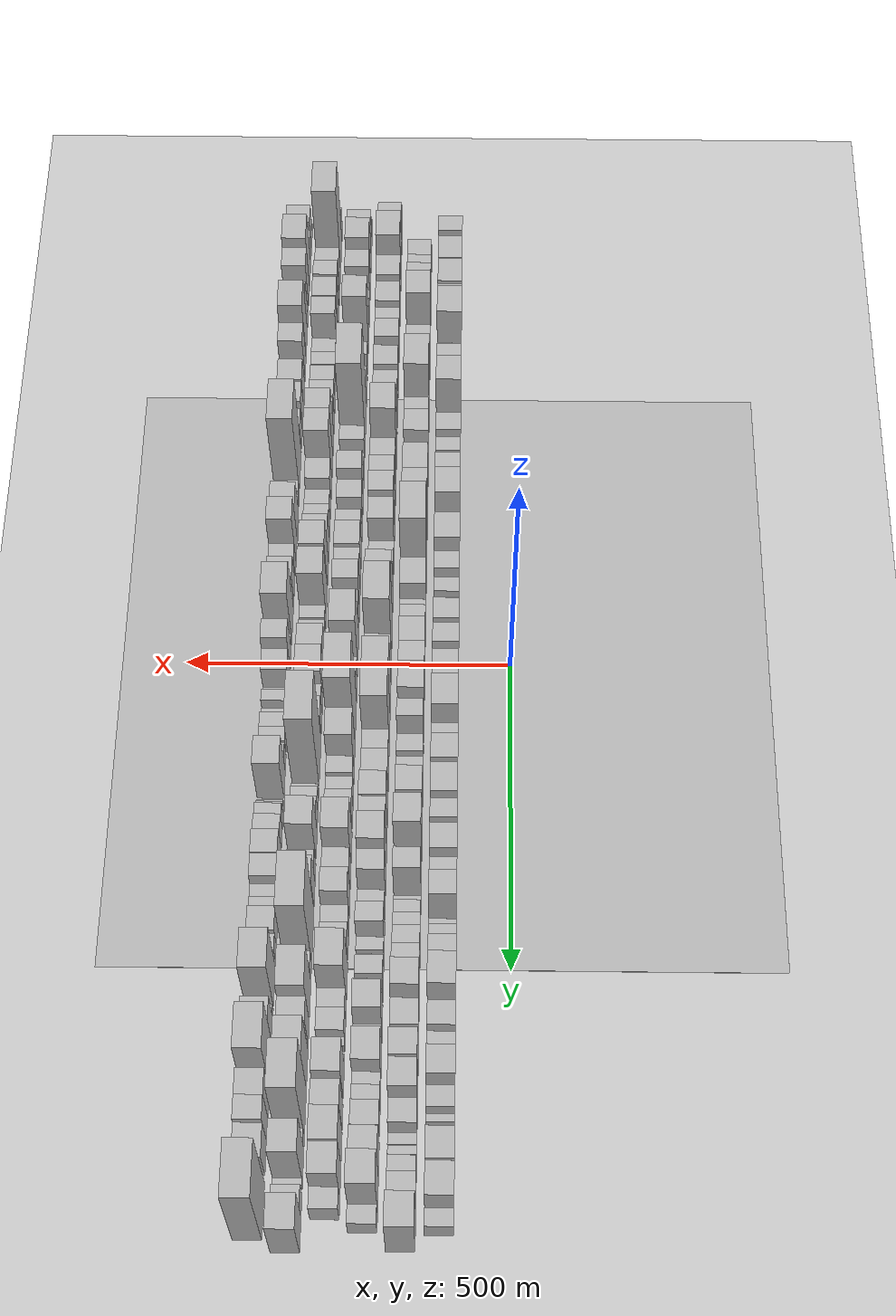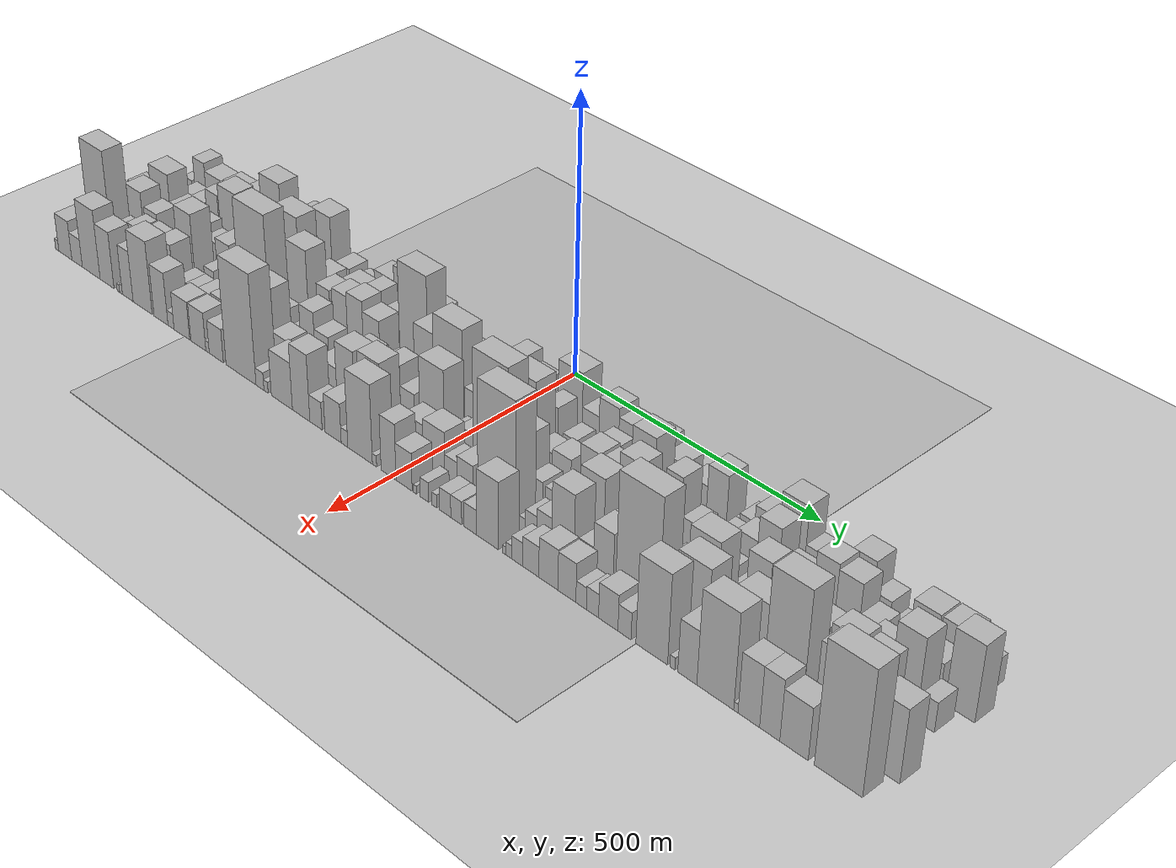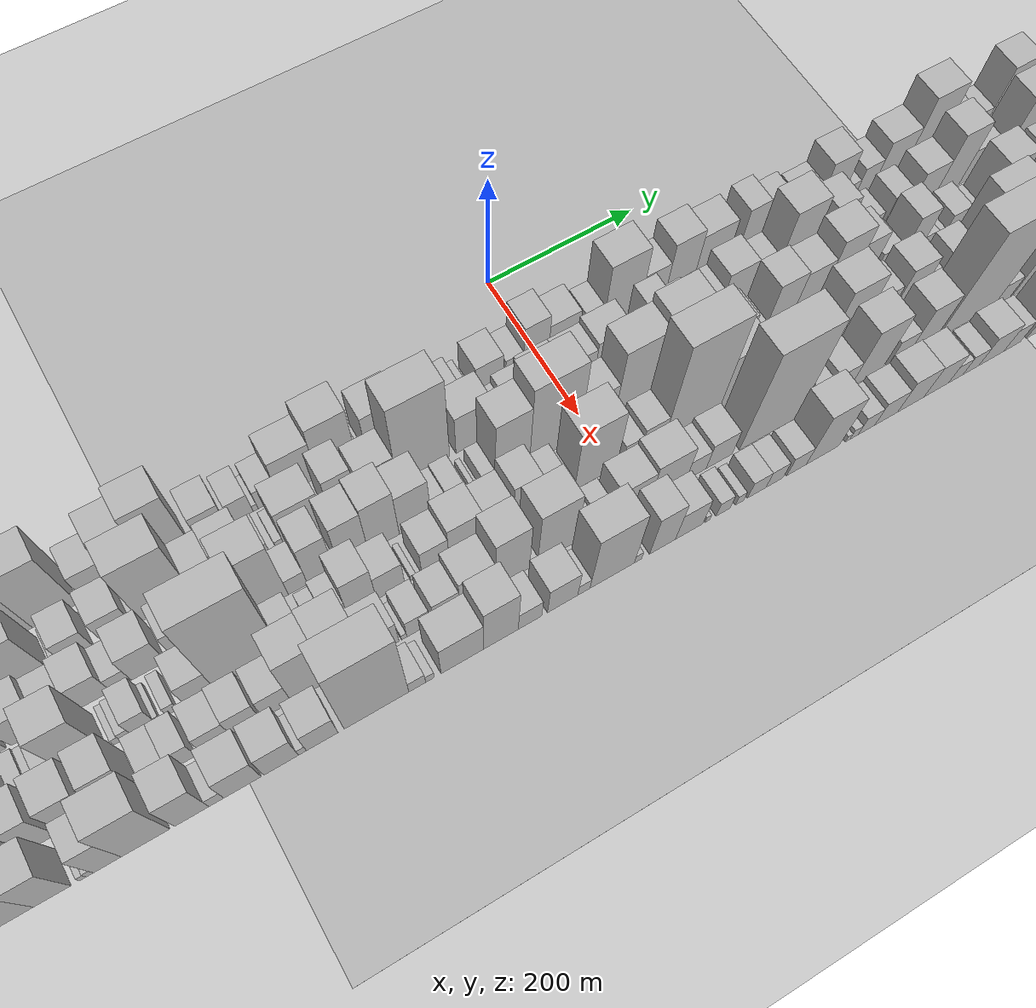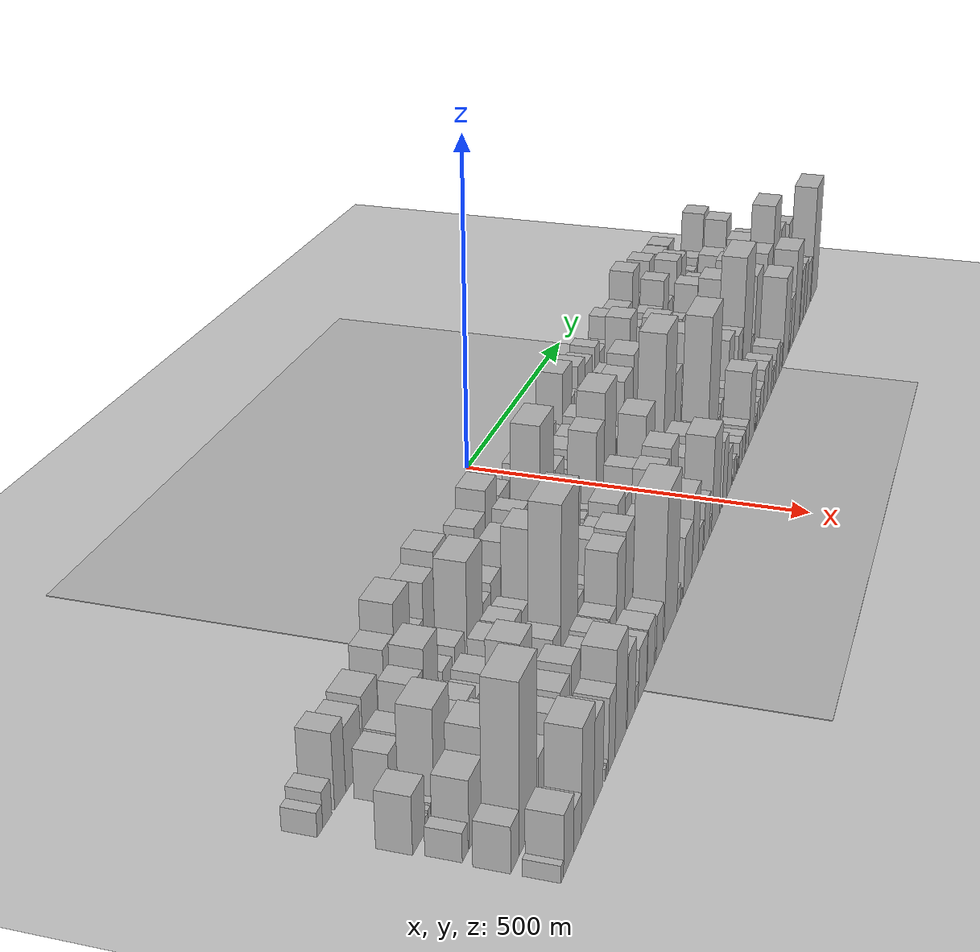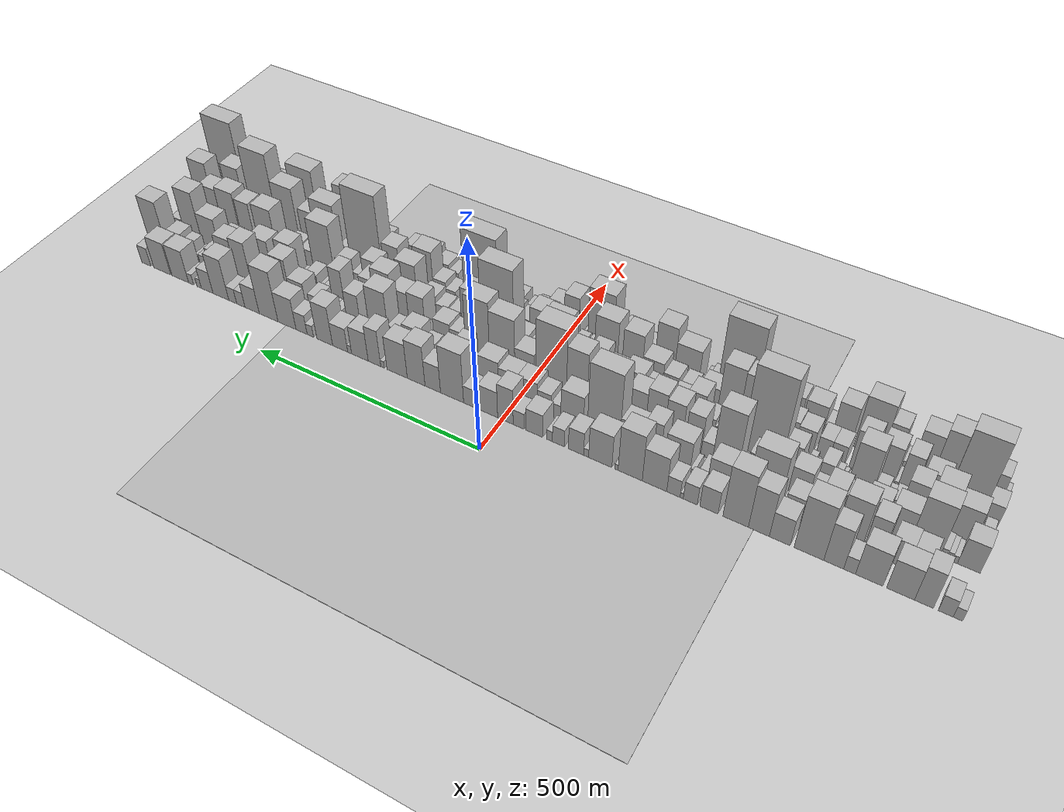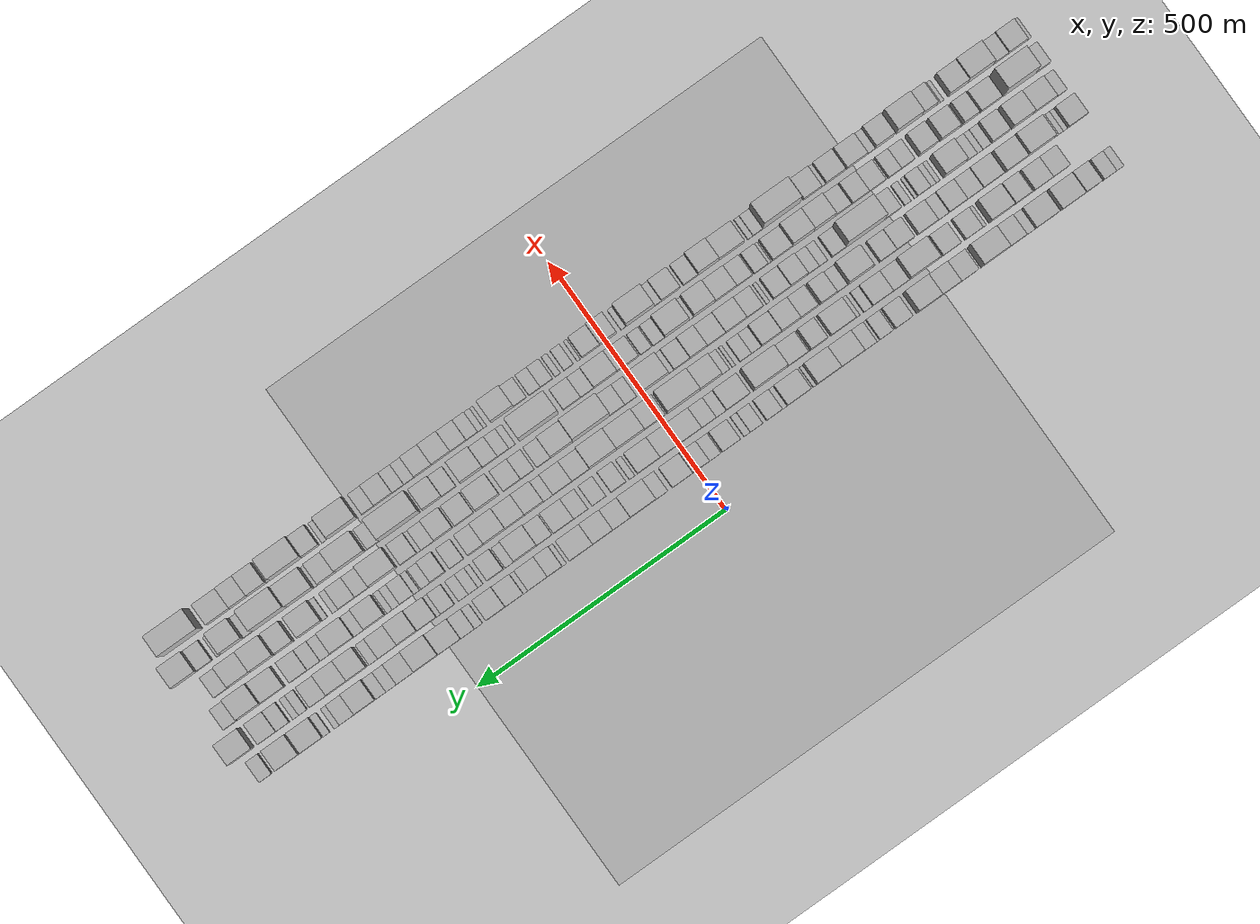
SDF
<?xml version="1.0" encoding="utf-8"?>

<sdf version="1.6">

   <world name="default">

      <gui fullscreen="0">

         <camera name="user_camera">

            <pose>-15 0 4.57585 0 0 0</pose>

            <view_controller>orbit</view_controller>

         </camera>

      </gui>

      <scene>

         <sky>

           <clouds>

             <speed>12</speed>

           </clouds>

         </sky>

         <ambient>0.4 0.4 0.4 1</ambient>

         <background>0.7 0.7 0.7 1</background>

         <shadows>1</shadows>

      </scene>

      <gravity>0 0 -9.8066</gravity>

      <magnetic_field>6e-06 2.3e-05 -4.2e-05</magnetic_field>

      <physics default="0" name="default_physics" type="ode">

         <ode>

            <solver>

               <type>quick</type>

               <iters>10</iters>

               <sor>1.0</sor>

               <use_dynamic_moi_rescaling>0</use_dynamic_moi_rescaling>

            </solver>

            <constraints>

               <cfm>0</cfm>

               <erp>0.2</erp>

               <contact_max_correcting_vel>100</contact_max_correcting_vel>

               <contact_surface_layer>0.001</contact_surface_layer>

            </constraints>

         </ode>

         <max_step_size>0.004</max_step_size>

         <real_time_factor>1</real_time_factor>

         <real_time_update_rate>250</real_time_update_rate>

      </physics>

      <light name="sun" type="directional">

         <cast_shadows>1</cast_shadows>

         <pose>0 0 10 0 0 0</pose>

         <diffuse>0.8 0.8 0.8 1</diffuse>

         <specular>0.2 0.2 0.2 1</specular>

         <attenuation>

            <range>1000</range>

            <constant>0.9</constant>

            <linear>0.01</linear>

            <quadratic>0.001</quadratic>

         </attenuation>

         <direction>-0.5 0.1 -0.9</direction>

      </light>

      <include>

         <name>ground_plane_1</name>

         <uri>model://HANNAS_ground_plane</uri>

         <pose>0 0 0  0 0 0</pose>

      </include>

      <include>

         <name>ground_plane_2</name>

         <uri>model://HANNAS_ground_plane</uri>

         <pose>100 0 0  0 0 0</pose>

      </include>

      <model name="building_1">

         <static>1</static>

         <pose frame="">100.0000 -852.3548 0 0.000000 0.000000 0.000000</pose>

         <link name="link">

            <pose frame="">0 0 15.00 0 0 0</pose>

            <collision name="collision">

               <geometry>

                  <box>

                     <size>40.0000 15.2904 30.0000</size>

                  </box>

               </geometry>

               <max_contacts>10</max_contacts>

               <surface>

                  <contact>

                     <ode/>

                  </contact>

                  <bounce/>

                  <friction>

                     <torsional>

                        <ode/>

                     </torsional>

                     <ode/>

                  </friction>

               </surface>

            </collision>

            <visual name="visual">

               <cast_shadows>0</cast_shadows>

               <geometry>

                  <box>

                     <size>40.0000 15.2904 30.0000</size>

                  </box>

               </geometry>

               <material>

                  <script>

                     <uri>model://HANNAS_wall/materials/scripts</uri>

                     <uri>model://HANNAS_wall/materials/textures</uri>

                     <name>vrc/HANNAS_wall</name>

                  </script>

               </material>

            </visual>

            <self_collide>0</self_collide>

            <enable_wind>0</enable_wind>

            <kinematic>0</kinematic>

         </link>

      </model>

      <model name="building_2">

         <static>1</static>

         <pose frame="">100.0000 -832.4451 0 0.000000 0.000000 0.000000</pose>

         <link name="link">

            <pose frame="">0 0 22.50 0 0 0</pose>

            <collision name="collision">

               <geometry>

                  <box>

                     <size>40.0000 24.5290 45.0000</size>

                  </box>

               </geometry>

               <max_contacts>10</max_contacts>

               <surface>

                  <contact>

                     <ode/>

                  </contact>

                  <bounce/>

                  <friction>

                     <torsional>

                        <ode/>

                     </torsional>

                     <ode/>

                  </friction>

               </surface>

            </collision>

            <visual name="visual">

               <cast_shadows>0</cast_shadows>

               <geometry>

                  <box>

                     <size>40.0000 24.5290 45.0000</size>

                  </box>

               </geometry>

               <material>

                  <script>

                     <uri>model://HANNAS_wall/materials/scripts</uri>

                     <uri>model://HANNAS_wall/materials/textures</uri>

                     <name>vrc/HANNAS_wall</name>

                  </script>

               </material>

            </visual>

            <self_collide>0</self_collide>

            <enable_wind>0</enable_wind>

            <kinematic>0</kinematic>

         </link>

      </model>

      <model name="building_3">

         <static>1</static>

         <pose frame="">100.0000 -796.4964 0 0.000000 0.000000 0.000000</pose>

         <link name="link">

            <pose frame="">0 0 48.00 0 0 0</pose>

            <collision name="collision">

               <geometry>

                  <box>

                     <size>40.0000 31.3685 96.0000</size>

                  </box>

               </geometry>

               <max_contacts>10</max_contacts>

               <surface>

                  <contact>

                     <ode/>

                  </contact>

                  <bounce/>

                  <friction>

                     <torsional>

                        <ode/>

                     </torsional>

                     <ode/>

                  </friction>

               </surface>

            </collision>

            <visual name="visual">

               <cast_shadows>0</cast_shadows>

               <geometry>

                  <box>

                     <size>40.0000 31.3685 96.0000</size>

                  </box>

               </geometry>

               <material>

                  <script>

                     <uri>model://HANNAS_wall/materials/scripts</uri>

                     <uri>model://HANNAS_wall/materials/textures</uri>

                     <name>vrc/HANNAS_wall</name>

                  </script>

               </material>

            </visual>

            <self_collide>0</self_collide>

            <enable_wind>0</enable_wind>

            <kinematic>0</kinematic>

         </link>

      </model>

      <model name="building_4">

         <static>1</static>

         <pose frame="">100.0000 -757.3240 0 0.000000 0.000000 0.000000</pose>

         <link name="link">

            <pose frame="">0 0 40.50 0 0 0</pose>

            <collision name="collision">

               <geometry>

                  <box>

                     <size>40.0000 46.9763 81.0000</size>

                  </box>

               </geometry>

               <max_contacts>10</max_contacts>

               <surface>

                  <contact>

                     <ode/>

                  </contact>

                  <bounce/>

                  <friction>

                     <torsional>

                        <ode/>

                     </torsional>

                     <ode/>

                  </friction>

               </surface>

            </collision>

            <visual name="visual">

               <cast_shadows>0</cast_shadows>

               <geometry>

                  <box>

                     <size>40.0000 46.9763 81.0000</size>

                  </box>

               </geometry>

               <material>

                  <script>

                     <uri>model://HANNAS_wall/materials/scripts</uri>

                     <uri>model://HANNAS_wall/materials/textures</uri>

                     <name>vrc/HANNAS_wall</name>

                  </script>

               </material>

            </visual>

            <self_collide>0</self_collide>

            <enable_wind>0</enable_wind>

            <kinematic>0</kinematic>

         </link>

      </model>

      <model name="building_5">

         <static>1</static>

         <pose frame="">100.0000 -704.3522 0 0.000000 0.000000 0.000000</pose>

         <link name="link">

            <pose frame="">0 0 43.50 0 0 0</pose>

            <collision name="collision">

               <geometry>

                  <box>

                     <size>40.0000 46.9672 87.0000</size>

                  </box>

               </geometry>

               <max_contacts>10</max_contacts>

               <surface>

                  <contact>

                     <ode/>

                  </contact>

                  <bounce/>

                  <friction>

                     <torsional>

                        <ode/>

                     </torsional>

                     <ode/>

                  </friction>

               </surface>

            </collision>

            <visual name="visual">

               <cast_shadows>0</cast_shadows>

               <geometry>

                  <box>

                     <size>40.0000 46.9672 87.0000</size>

                  </box>

               </geometry>

               <material>

                  <script>

                     <uri>model://HANNAS_wall/materials/scripts</uri>

                     <uri>model://HANNAS_wall/materials/textures</uri>

                     <name>vrc/HANNAS_wall</name>

                  </script>

               </material>

            </visual>

            <self_collide>0</self_collide>

            <enable_wind>0</enable_wind>

            <kinematic>0</kinematic>

         </link>

      </model>

      <model name="building_6">

         <static>1</static>

         <pose frame="">100.0000 -670.6268 0 0.000000 0.000000 0.000000</pose>

         <link name="link">

            <pose frame="">0 0 19.50 0 0 0</pose>

            <collision name="collision">

               <geometry>

                  <box>

                     <size>40.0000 20.4838 39.0000</size>

                  </box>

               </geometry>

               <max_contacts>10</max_contacts>

               <surface>

                  <contact>

                     <ode/>

                  </contact>

                  <bounce/>

                  <friction>

                     <torsional>

                        <ode/>

                     </torsional>

                     <ode/>

                  </friction>

               </surface>

            </collision>

            <visual name="visual">

               <cast_shadows>0</cast_shadows>

               <geometry>

                  <box>

                     <size>40.0000 20.4838 39.0000</size>

                  </box>

               </geometry>

               <material>

                  <script>

                     <uri>model://HANNAS_wall/materials/scripts</uri>

                     <uri>model://HANNAS_wall/materials/textures</uri>

                     <name>vrc/HANNAS_wall</name>

                  </script>

               </material>

            </visual>

            <self_collide>0</self_collide>

            <enable_wind>0</enable_wind>

            <kinematic>0</kinematic>

         </link>

      </model>

      <model name="building_7">

         <static>1</static>

         <pose frame="">100.0000 -643.0278 0 0.000000 0.000000 0.000000</pose>

         <link name="link">

            <pose frame="">0 0 52.50 0 0 0</pose>

            <collision name="collision">

               <geometry>

                  <box>

                     <size>40.0000 34.7143 105.0000</size>

                  </box>

               </geometry>

               <max_contacts>10</max_contacts>

               <surface>

                  <contact>

                     <ode/>

                  </contact>

                  <bounce/>

                  <friction>

                     <torsional>

                        <ode/>

                     </torsional>

                     <ode/>

                  </friction>

               </surface>

            </collision>

            <visual name="visual">

               <cast_shadows>0</cast_shadows>

               <geometry>

                  <box>

                     <size>40.0000 34.7143 105.0000</size>

                  </box>

               </geometry>

               <material>

                  <script>

                     <uri>model://HANNAS_wall/materials/scripts</uri>

                     <uri>model://HANNAS_wall/materials/textures</uri>

                     <name>vrc/HANNAS_wall</name>

                  </script>

               </material>

            </visual>

            <self_collide>0</self_collide>

            <enable_wind>0</enable_wind>

            <kinematic>0</kinematic>

         </link>

      </model>

      <model name="building_8">

         <static>1</static>

         <pose frame="">100.0000 -599.3234 0 0.000000 0.000000 0.000000</pose>

         <link name="link">

            <pose frame="">0 0 72.00 0 0 0</pose>

            <collision name="collision">

               <geometry>

                  <box>

                     <size>40.0000 52.6946 144.0000</size>

                  </box>

               </geometry>

               <max_contacts>10</max_contacts>

               <surface>

                  <contact>

                     <ode/>

                  </contact>

                  <bounce/>

                  <friction>

                     <torsional>

                        <ode/>

                     </torsional>

                     <ode/>

                  </friction>

               </surface>

            </collision>

            <visual name="visual">

               <cast_shadows>0</cast_shadows>

               <geometry>

                  <box>

                     <size>40.0000 52.6946 144.0000</size>

                  </box>

               </geometry>

               <material>

                  <script>

                     <uri>model://HANNAS_wall/materials/scripts</uri>

                     <uri>model://HANNAS_wall/materials/textures</uri>

                     <name>vrc/HANNAS_wall</name>

                  </script>

               </material>

            </visual>

            <self_collide>0</self_collide>

            <enable_wind>0</enable_wind>

            <kinematic>0</kinematic>

         </link>

      </model>

      <model name="building_9">

         <static>1</static>

         <pose frame="">100.0000 -547.2564 0 0.000000 0.000000 0.000000</pose>

         <link name="link">

            <pose frame="">0 0 34.50 0 0 0</pose>

            <collision name="collision">

               <geometry>

                  <box>

                     <size>40.0000 37.4394 69.0000</size>

                  </box>

               </geometry>

               <max_contacts>10</max_contacts>

               <surface>

                  <contact>

                     <ode/>

                  </contact>

                  <bounce/>

                  <friction>

                     <torsional>

                        <ode/>

                     </torsional>

                     <ode/>

                  </friction>

               </surface>

            </collision>

            <visual name="visual">

               <cast_shadows>0</cast_shadows>

               <geometry>

                  <box>

                     <size>40.0000 37.4394 69.0000</size>

                  </box>

               </geometry>

               <material>

                  <script>

                     <uri>model://HANNAS_wall/materials/scripts</uri>

                     <uri>model://HANNAS_wall/materials/textures</uri>

                     <name>vrc/HANNAS_wall</name>

                  </script>

               </material>

            </visual>

            <self_collide>0</self_collide>

            <enable_wind>0</enable_wind>

            <kinematic>0</kinematic>

         </link>

      </model>

      <model name="building_10">

         <static>1</static>

         <pose frame="">100.0000 -509.3319 0 0.000000 0.000000 0.000000</pose>

         <link name="link">

            <pose frame="">0 0 58.50 0 0 0</pose>

            <collision name="collision">

               <geometry>

                  <box>

                     <size>40.0000 38.4094 117.0000</size>

                  </box>

               </geometry>

               <max_contacts>10</max_contacts>

               <surface>

                  <contact>

                     <ode/>

                  </contact>

                  <bounce/>

                  <friction>

                     <torsional>

                        <ode/>

                     </torsional>

                     <ode/>

                  </friction>

               </surface>

            </collision>

            <visual name="visual">

               <cast_shadows>0</cast_shadows>

               <geometry>

                  <box>

                     <size>40.0000 38.4094 117.0000</size>

                  </box>

               </geometry>

               <material>

                  <script>

                     <uri>model://HANNAS_wall/materials/scripts</uri>

                     <uri>model://HANNAS_wall/materials/textures</uri>

                     <name>vrc/HANNAS_wall</name>

                  </script>

               </material>

            </visual>

            <self_collide>0</self_collide>

            <enable_wind>0</enable_wind>

            <kinematic>0</kinematic>

         </link>

      </model>

      <model name="building_11">

         <static>1</static>

         <pose frame="">100.0000 -466.4925 0 0.000000 0.000000 0.000000</pose>

         <link name="link">

            <pose frame="">0 0 69.00 0 0 0</pose>

            <collision name="collision">

               <geometry>

                  <box>

                     <size>40.0000 47.2694 138.0000</size>

                  </box>

               </geometry>

               <max_contacts>10</max_contacts>

               <surface>

                  <contact>

                     <ode/>

                  </contact>

                  <bounce/>

                  <friction>

                     <torsional>

                        <ode/>

                     </torsional>

                     <ode/>

                  </friction>

               </surface>

            </collision>

            <visual name="visual">

               <cast_shadows>0</cast_shadows>

               <geometry>

                  <box>

                     <size>40.0000 47.2694 138.0000</size>

                  </box>

               </geometry>

               <material>

                  <script>

                     <uri>model://HANNAS_wall/materials/scripts</uri>

                     <uri>model://HANNAS_wall/materials/textures</uri>

                     <name>vrc/HANNAS_wall</name>

                  </script>

               </material>

            </visual>

            <self_collide>0</self_collide>

            <enable_wind>0</enable_wind>

            <kinematic>0</kinematic>

         </link>

      </model>

      <model name="building_12">

         <static>1</static>

         <pose frame="">100.0000 -416.6845 0 0.000000 0.000000 0.000000</pose>

         <link name="link">

            <pose frame="">0 0 30.00 0 0 0</pose>

            <collision name="collision">

               <geometry>

                  <box>

                     <size>40.0000 34.3465 60.0000</size>

                  </box>

               </geometry>

               <max_contacts>10</max_contacts>

               <surface>

                  <contact>

                     <ode/>

                  </contact>

                  <bounce/>

                  <friction>

                     <torsional>

                        <ode/>

                     </torsional>

                     <ode/>

                  </friction>

               </surface>

            </collision>

            <visual name="visual">

               <cast_shadows>0</cast_shadows>

               <geometry>

                  <box>

                     <size>40.0000 34.3465 60.0000</size>

                  </box>

               </geometry>

               <material>

                  <script>

                     <uri>model://HANNAS_wall/materials/scripts</uri>

                     <uri>model://HANNAS_wall/materials/textures</uri>

                     <name>vrc/HANNAS_wall</name>

                  </script>

               </material>

            </visual>

            <self_collide>0</self_collide>

            <enable_wind>0</enable_wind>

            <kinematic>0</kinematic>

         </link>

      </model>

      <model name="building_13">

         <static>1</static>

         <pose frame="">100.0000 -381.1827 0 0.000000 0.000000 0.000000</pose>

         <link name="link">

            <pose frame="">0 0 24.00 0 0 0</pose>

            <collision name="collision">

               <geometry>

                  <box>

                     <size>40.0000 26.6572 48.0000</size>

                  </box>

               </geometry>

               <max_contacts>10</max_contacts>

               <surface>

                  <contact>

                     <ode/>

                  </contact>

                  <bounce/>

                  <friction>

                     <torsional>

                        <ode/>

                     </torsional>

                     <ode/>

                  </friction>

               </surface>

            </collision>

            <visual name="visual">

               <cast_shadows>0</cast_shadows>

               <geometry>

                  <box>

                     <size>40.0000 26.6572 48.0000</size>

                  </box>

               </geometry>

               <material>

                  <script>

                     <uri>model://HANNAS_wall/materials/scripts</uri>

                     <uri>model://HANNAS_wall/materials/textures</uri>

                     <name>vrc/HANNAS_wall</name>

                  </script>

               </material>

            </visual>

            <self_collide>0</self_collide>

            <enable_wind>0</enable_wind>

            <kinematic>0</kinematic>

         </link>

      </model>

      <model name="building_14">

         <static>1</static>

         <pose frame="">100.0000 -364.8093 0 0.000000 0.000000 0.000000</pose>

         <link name="link">

            <pose frame="">0 0 7.50 0 0 0</pose>

            <collision name="collision">

               <geometry>

                  <box>

                     <size>40.0000 6.0895 15.0000</size>

                  </box>

               </geometry>

               <max_contacts>10</max_contacts>

               <surface>

                  <contact>

                     <ode/>

                  </contact>

                  <bounce/>

                  <friction>

                     <torsional>

                        <ode/>

                     </torsional>

                     <ode/>

                  </friction>

               </surface>

            </collision>

            <visual name="visual">

               <cast_shadows>0</cast_shadows>

               <geometry>

                  <box>

                     <size>40.0000 6.0895 15.0000</size>

                  </box>

               </geometry>

               <material>

                  <script>

                     <uri>model://HANNAS_wall/materials/scripts</uri>

                     <uri>model://HANNAS_wall/materials/textures</uri>

                     <name>vrc/HANNAS_wall</name>

                  </script>

               </material>

            </visual>

            <self_collide>0</self_collide>

            <enable_wind>0</enable_wind>

            <kinematic>0</kinematic>

         </link>

      </model>

      <model name="building_15">

         <static>1</static>

         <pose frame="">100.0000 -348.9522 0 0.000000 0.000000 0.000000</pose>

         <link name="link">

            <pose frame="">0 0 22.50 0 0 0</pose>

            <collision name="collision">

               <geometry>

                  <box>

                     <size>40.0000 25.6248 45.0000</size>

                  </box>

               </geometry>

               <max_contacts>10</max_contacts>

               <surface>

                  <contact>

                     <ode/>

                  </contact>

                  <bounce/>

                  <friction>

                     <torsional>

                        <ode/>

                     </torsional>

                     <ode/>

                  </friction>

               </surface>

            </collision>

            <visual name="visual">

               <cast_shadows>0</cast_shadows>

               <geometry>

                  <box>

                     <size>40.0000 25.6248 45.0000</size>

                  </box>

               </geometry>

               <material>

                  <script>

                     <uri>model://HANNAS_wall/materials/scripts</uri>

                     <uri>model://HANNAS_wall/materials/textures</uri>

                     <name>vrc/HANNAS_wall</name>

                  </script>

               </material>

            </visual>

            <self_collide>0</self_collide>

            <enable_wind>0</enable_wind>

            <kinematic>0</kinematic>

         </link>

      </model>

      <model name="building_16">

         <static>1</static>

         <pose frame="">100.0000 -312.2584 0 0.000000 0.000000 0.000000</pose>

         <link name="link">

            <pose frame="">0 0 45.00 0 0 0</pose>

            <collision name="collision">

               <geometry>

                  <box>

                     <size>40.0000 47.7629 90.0000</size>

                  </box>

               </geometry>

               <max_contacts>10</max_contacts>

               <surface>

                  <contact>

                     <ode/>

                  </contact>

                  <bounce/>

                  <friction>

                     <torsional>

                        <ode/>

                     </torsional>

                     <ode/>

                  </friction>

               </surface>

            </collision>

            <visual name="visual">

               <cast_shadows>0</cast_shadows>

               <geometry>

                  <box>

                     <size>40.0000 47.7629 90.0000</size>

                  </box>

               </geometry>

               <material>

                  <script>

                     <uri>model://HANNAS_wall/materials/scripts</uri>

                     <uri>model://HANNAS_wall/materials/textures</uri>

                     <name>vrc/HANNAS_wall</name>

                  </script>

               </material>

            </visual>

            <self_collide>0</self_collide>

            <enable_wind>0</enable_wind>

            <kinematic>0</kinematic>

         </link>

      </model>

      <model name="building_17">

         <static>1</static>

         <pose frame="">100.0000 -264.4707 0 0.000000 0.000000 0.000000</pose>

         <link name="link">

            <pose frame="">0 0 60.00 0 0 0</pose>

            <collision name="collision">

               <geometry>

                  <box>

                     <size>40.0000 47.8126 120.0000</size>

                  </box>

               </geometry>

               <max_contacts>10</max_contacts>

               <surface>

                  <contact>

                     <ode/>

                  </contact>

                  <bounce/>

                  <friction>

                     <torsional>

                        <ode/>

                     </torsional>

                     <ode/>

                  </friction>

               </surface>

            </collision>

            <visual name="visual">

               <cast_shadows>0</cast_shadows>

               <geometry>

                  <box>

                     <size>40.0000 47.8126 120.0000</size>

                  </box>

               </geometry>

               <material>

                  <script>

                     <uri>model://HANNAS_wall/materials/scripts</uri>

                     <uri>model://HANNAS_wall/materials/textures</uri>

                     <name>vrc/HANNAS_wall</name>

                  </script>

               </material>

            </visual>

            <self_collide>0</self_collide>

            <enable_wind>0</enable_wind>

            <kinematic>0</kinematic>

         </link>

      </model>

      <model name="building_18">

         <static>1</static>

         <pose frame="">100.0000 -237.3521 0 0.000000 0.000000 0.000000</pose>

         <link name="link">

            <pose frame="">0 0 7.50 0 0 0</pose>

            <collision name="collision">

               <geometry>

                  <box>

                     <size>40.0000 6.4245 15.0000</size>

                  </box>

               </geometry>

               <max_contacts>10</max_contacts>

               <surface>

                  <contact>

                     <ode/>

                  </contact>

                  <bounce/>

                  <friction>

                     <torsional>

                        <ode/>

                     </torsional>

                     <ode/>

                  </friction>

               </surface>

            </collision>

            <visual name="visual">

               <cast_shadows>0</cast_shadows>

               <geometry>

                  <box>

                     <size>40.0000 6.4245 15.0000</size>

                  </box>

               </geometry>

               <material>

                  <script>

                     <uri>model://HANNAS_wall/materials/scripts</uri>

                     <uri>model://HANNAS_wall/materials/textures</uri>

                     <name>vrc/HANNAS_wall</name>

                  </script>

               </material>

            </visual>

            <self_collide>0</self_collide>

            <enable_wind>0</enable_wind>

            <kinematic>0</kinematic>

         </link>

      </model>

      <model name="building_19">

         <static>1</static>

         <pose frame="">100.0000 -204.6399 0 0.000000 0.000000 0.000000</pose>

         <link name="link">

            <pose frame="">0 0 42.00 0 0 0</pose>

            <collision name="collision">

               <geometry>

                  <box>

                     <size>40.0000 46.9999 84.0000</size>

                  </box>

               </geometry>

               <max_contacts>10</max_contacts>

               <surface>

                  <contact>

                     <ode/>

                  </contact>

                  <bounce/>

                  <friction>

                     <torsional>

                        <ode/>

                     </torsional>

                     <ode/>

                  </friction>

               </surface>

            </collision>

            <visual name="visual">

               <cast_shadows>0</cast_shadows>

               <geometry>

                  <box>

                     <size>40.0000 46.9999 84.0000</size>

                  </box>

               </geometry>

               <material>

                  <script>

                     <uri>model://HANNAS_wall/materials/scripts</uri>

                     <uri>model://HANNAS_wall/materials/textures</uri>

                     <name>vrc/HANNAS_wall</name>

                  </script>

               </material>

            </visual>

            <self_collide>0</self_collide>

            <enable_wind>0</enable_wind>

            <kinematic>0</kinematic>

         </link>

      </model>

      <model name="building_20">

         <static>1</static>

         <pose frame="">100.0000 -176.0807 0 0.000000 0.000000 0.000000</pose>

         <link name="link">

            <pose frame="">0 0 10.50 0 0 0</pose>

            <collision name="collision">

               <geometry>

                  <box>

                     <size>40.0000 10.1186 21.0000</size>

                  </box>

               </geometry>

               <max_contacts>10</max_contacts>

               <surface>

                  <contact>

                     <ode/>

                  </contact>

                  <bounce/>

                  <friction>

                     <torsional>

                        <ode/>

                     </torsional>

                     <ode/>

                  </friction>

               </surface>

            </collision>

            <visual name="visual">

               <cast_shadows>0</cast_shadows>

               <geometry>

                  <box>

                     <size>40.0000 10.1186 21.0000</size>

                  </box>

               </geometry>

               <material>

                  <script>

                     <uri>model://HANNAS_wall/materials/scripts</uri>

                     <uri>model://HANNAS_wall/materials/textures</uri>

                     <name>vrc/HANNAS_wall</name>

                  </script>

               </material>

            </visual>

            <self_collide>0</self_collide>

            <enable_wind>0</enable_wind>

            <kinematic>0</kinematic>

         </link>

      </model>

      <model name="building_21">

         <static>1</static>

         <pose frame="">100.0000 -155.4056 0 0.000000 0.000000 0.000000</pose>

         <link name="link">

            <pose frame="">0 0 30.00 0 0 0</pose>

            <collision name="collision">

               <geometry>

                  <box>

                     <size>40.0000 31.2315 60.0000</size>

                  </box>

               </geometry>

               <max_contacts>10</max_contacts>

               <surface>

                  <contact>

                     <ode/>

                  </contact>

                  <bounce/>

                  <friction>

                     <torsional>

                        <ode/>

                     </torsional>

                     <ode/>

                  </friction>

               </surface>

            </collision>

            <visual name="visual">

               <cast_shadows>0</cast_shadows>

               <geometry>

                  <box>

                     <size>40.0000 31.2315 60.0000</size>

                  </box>

               </geometry>

               <material>

                  <script>

                     <uri>model://HANNAS_wall/materials/scripts</uri>

                     <uri>model://HANNAS_wall/materials/textures</uri>

                     <name>vrc/HANNAS_wall</name>

                  </script>

               </material>

            </visual>

            <self_collide>0</self_collide>

            <enable_wind>0</enable_wind>

            <kinematic>0</kinematic>

         </link>

      </model>

      <model name="building_22">

         <static>1</static>

         <pose frame="">100.0000 -119.2429 0 0.000000 0.000000 0.000000</pose>

         <link name="link">

            <pose frame="">0 0 22.50 0 0 0</pose>

            <collision name="collision">

               <geometry>

                  <box>

                     <size>40.0000 25.0939 45.0000</size>

                  </box>

               </geometry>

               <max_contacts>10</max_contacts>

               <surface>

                  <contact>

                     <ode/>

                  </contact>

                  <bounce/>

                  <friction>

                     <torsional>

                        <ode/>

                     </torsional>

                     <ode/>

                  </friction>

               </surface>

            </collision>

            <visual name="visual">

               <cast_shadows>0</cast_shadows>

               <geometry>

                  <box>

                     <size>40.0000 25.0939 45.0000</size>

                  </box>

               </geometry>

               <material>

                  <script>

                     <uri>model://HANNAS_wall/materials/scripts</uri>

                     <uri>model://HANNAS_wall/materials/textures</uri>

                     <name>vrc/HANNAS_wall</name>

                  </script>

               </material>

            </visual>

            <self_collide>0</self_collide>

            <enable_wind>0</enable_wind>

            <kinematic>0</kinematic>

         </link>

      </model>

      <model name="building_23">

         <static>1</static>

         <pose frame="">100.0000 -100.5905 0 0.000000 0.000000 0.000000</pose>

         <link name="link">

            <pose frame="">0 0 13.50 0 0 0</pose>

            <collision name="collision">

               <geometry>

                  <box>

                     <size>40.0000 12.2109 27.0000</size>

                  </box>

               </geometry>

               <max_contacts>10</max_contacts>

               <surface>

                  <contact>

                     <ode/>

                  </contact>

                  <bounce/>

                  <friction>

                     <torsional>

                        <ode/>

                     </torsional>

                     <ode/>

                  </friction>

               </surface>

            </collision>

            <visual name="visual">

               <cast_shadows>0</cast_shadows>

               <geometry>

                  <box>

                     <size>40.0000 12.2109 27.0000</size>

                  </box>

               </geometry>

               <material>

                  <script>

                     <uri>model://HANNAS_wall/materials/scripts</uri>

                     <uri>model://HANNAS_wall/materials/textures</uri>

                     <name>vrc/HANNAS_wall</name>

                  </script>

               </material>

            </visual>

            <self_collide>0</self_collide>

            <enable_wind>0</enable_wind>

            <kinematic>0</kinematic>

         </link>

      </model>

      <model name="building_24">

         <static>1</static>

         <pose frame="">100.0000 -68.5323 0 0.000000 0.000000 0.000000</pose>

         <link name="link">

            <pose frame="">0 0 30.00 0 0 0</pose>

            <collision name="collision">

               <geometry>

                  <box>

                     <size>40.0000 35.9056 60.0000</size>

                  </box>

               </geometry>

               <max_contacts>10</max_contacts>

               <surface>

                  <contact>

                     <ode/>

                  </contact>

                  <bounce/>

                  <friction>

                     <torsional>

                        <ode/>

                     </torsional>

                     <ode/>

                  </friction>

               </surface>

            </collision>

            <visual name="visual">

               <cast_shadows>0</cast_shadows>

               <geometry>

                  <box>

                     <size>40.0000 35.9056 60.0000</size>

                  </box>

               </geometry>

               <material>

                  <script>

                     <uri>model://HANNAS_wall/materials/scripts</uri>

                     <uri>model://HANNAS_wall/materials/textures</uri>

                     <name>vrc/HANNAS_wall</name>

                  </script>

               </material>

            </visual>

            <self_collide>0</self_collide>

            <enable_wind>0</enable_wind>

            <kinematic>0</kinematic>

         </link>

      </model>

      <model name="building_25">

         <static>1</static>

         <pose frame="">100.0000 -35.7939 0 0.000000 0.000000 0.000000</pose>

         <link name="link">

            <pose frame="">0 0 21.00 0 0 0</pose>

            <collision name="collision">

               <geometry>

                  <box>

                     <size>40.0000 23.5713 42.0000</size>

                  </box>

               </geometry>

               <max_contacts>10</max_contacts>

               <surface>

                  <contact>

                     <ode/>

                  </contact>

                  <bounce/>

                  <friction>

                     <torsional>

                        <ode/>

                     </torsional>

                     <ode/>

                  </friction>

               </surface>

            </collision>

            <visual name="visual">

               <cast_shadows>0</cast_shadows>

               <geometry>

                  <box>

                     <size>40.0000 23.5713 42.0000</size>

                  </box>

               </geometry>

               <material>

                  <script>

                     <uri>model://HANNAS_wall/materials/scripts</uri>

                     <uri>model://HANNAS_wall/materials/textures</uri>

                     <name>vrc/HANNAS_wall</name>

                  </script>

               </material>

            </visual>

            <self_collide>0</self_collide>

            <enable_wind>0</enable_wind>

            <kinematic>0</kinematic>

         </link>

      </model>

      <model name="building_26">

         <static>1</static>

         <pose frame="">100.0000 -7.3441 0 0.000000 0.000000 0.000000</pose>

         <link name="link">

            <pose frame="">0 0 46.50 0 0 0</pose>

            <collision name="collision">

               <geometry>

                  <box>

                     <size>40.0000 33.3283 93.0000</size>

                  </box>

               </geometry>

               <max_contacts>10</max_contacts>

               <surface>

                  <contact>

                     <ode/>

                  </contact>

                  <bounce/>

                  <friction>

                     <torsional>

                        <ode/>

                     </torsional>

                     <ode/>

                  </friction>

               </surface>

            </collision>

            <visual name="visual">

               <cast_shadows>0</cast_shadows>

               <geometry>

                  <box>

                     <size>40.0000 33.3283 93.0000</size>

                  </box>

               </geometry>

               <material>

                  <script>

                     <uri>model://HANNAS_wall/materials/scripts</uri>

                     <uri>model://HANNAS_wall/materials/textures</uri>

                     <name>vrc/HANNAS_wall</name>

                  </script>

               </material>

            </visual>

            <self_collide>0</self_collide>

            <enable_wind>0</enable_wind>

            <kinematic>0</kinematic>

         </link>

      </model>

      <model name="building_27">

         <static>1</static>

         <pose frame="">100.0000 29.8711 0 0.000000 0.000000 0.000000</pose>

         <link name="link">

            <pose frame="">0 0 34.50 0 0 0</pose>

            <collision name="collision">

               <geometry>

                  <box>

                     <size>40.0000 41.1020 69.0000</size>

                  </box>

               </geometry>

               <max_contacts>10</max_contacts>

               <surface>

                  <contact>

                     <ode/>

                  </contact>

                  <bounce/>

                  <friction>

                     <torsional>

                        <ode/>

                     </torsional>

                     <ode/>

                  </friction>

               </surface>

            </collision>

            <visual name="visual">

               <cast_shadows>0</cast_shadows>

               <geometry>

                  <box>

                     <size>40.0000 41.1020 69.0000</size>

                  </box>

               </geometry>

               <material>

                  <script>

                     <uri>model://HANNAS_wall/materials/scripts</uri>

                     <uri>model://HANNAS_wall/materials/textures</uri>

                     <name>vrc/HANNAS_wall</name>

                  </script>

               </material>

            </visual>

            <self_collide>0</self_collide>

            <enable_wind>0</enable_wind>

            <kinematic>0</kinematic>

         </link>

      </model>

      <model name="building_28">

         <static>1</static>

         <pose frame="">100.0000 71.5119 0 0.000000 0.000000 0.000000</pose>

         <link name="link">

            <pose frame="">0 0 24.00 0 0 0</pose>

            <collision name="collision">

               <geometry>

                  <box>

                     <size>40.0000 24.1797 48.0000</size>

                  </box>

               </geometry>

               <max_contacts>10</max_contacts>

               <surface>

                  <contact>

                     <ode/>

                  </contact>

                  <bounce/>

                  <friction>

                     <torsional>

                        <ode/>

                     </torsional>

                     <ode/>

                  </friction>

               </surface>

            </collision>

            <visual name="visual">

               <cast_shadows>0</cast_shadows>

               <geometry>

                  <box>

                     <size>40.0000 24.1797 48.0000</size>

                  </box>

               </geometry>

               <material>

                  <script>

                     <uri>model://HANNAS_wall/materials/scripts</uri>

                     <uri>model://HANNAS_wall/materials/textures</uri>

                     <name>vrc/HANNAS_wall</name>

                  </script>

               </material>

            </visual>

            <self_collide>0</self_collide>

            <enable_wind>0</enable_wind>

            <kinematic>0</kinematic>

         </link>

      </model>

      <model name="building_29">

         <static>1</static>

         <pose frame="">100.0000 109.2819 0 0.000000 0.000000 0.000000</pose>

         <link name="link">

            <pose frame="">0 0 64.50 0 0 0</pose>

            <collision name="collision">

               <geometry>

                  <box>

                     <size>40.0000 51.3603 129.0000</size>

                  </box>

               </geometry>

               <max_contacts>10</max_contacts>

               <surface>

                  <contact>

                     <ode/>

                  </contact>

                  <bounce/>

                  <friction>

                     <torsional>

                        <ode/>

                     </torsional>

                     <ode/>

                  </friction>

               </surface>

            </collision>

            <visual name="visual">

               <cast_shadows>0</cast_shadows>

               <geometry>

                  <box>

                     <size>40.0000 51.3603 129.0000</size>

                  </box>

               </geometry>

               <material>

                  <script>

                     <uri>model://HANNAS_wall/materials/scripts</uri>

                     <uri>model://HANNAS_wall/materials/textures</uri>

                     <name>vrc/HANNAS_wall</name>

                  </script>

               </material>

            </visual>

            <self_collide>0</self_collide>

            <enable_wind>0</enable_wind>

            <kinematic>0</kinematic>

         </link>

      </model>

      <model name="building_30">

         <static>1</static>

         <pose frame="">100.0000 152.5103 0 0.000000 0.000000 0.000000</pose>

         <link name="link">

            <pose frame="">0 0 34.50 0 0 0</pose>

            <collision name="collision">

               <geometry>

                  <box>

                     <size>40.0000 35.0965 69.0000</size>

                  </box>

               </geometry>

               <max_contacts>10</max_contacts>

               <surface>

                  <contact>

                     <ode/>

                  </contact>

                  <bounce/>

                  <friction>

                     <torsional>

                        <ode/>

                     </torsional>

                     <ode/>

                  </friction>

               </surface>

            </collision>

            <visual name="visual">

               <cast_shadows>0</cast_shadows>

               <geometry>

                  <box>

                     <size>40.0000 35.0965 69.0000</size>

                  </box>

               </geometry>

               <material>

                  <script>

                     <uri>model://HANNAS_wall/materials/scripts</uri>

                     <uri>model://HANNAS_wall/materials/textures</uri>

                     <name>vrc/HANNAS_wall</name>

                  </script>

               </material>

            </visual>

            <self_collide>0</self_collide>

            <enable_wind>0</enable_wind>

            <kinematic>0</kinematic>

         </link>

      </model>

      <model name="building_31">

         <static>1</static>

         <pose frame="">100.0000 190.2256 0 0.000000 0.000000 0.000000</pose>

         <link name="link">

            <pose frame="">0 0 52.50 0 0 0</pose>

            <collision name="collision">

               <geometry>

                  <box>

                     <size>40.0000 40.3340 105.0000</size>

                  </box>

               </geometry>

               <max_contacts>10</max_contacts>

               <surface>

                  <contact>

                     <ode/>

                  </contact>

                  <bounce/>

                  <friction>

                     <torsional>

                        <ode/>

                     </torsional>

                     <ode/>

                  </friction>

               </surface>

            </collision>

            <visual name="visual">

               <cast_shadows>0</cast_shadows>

               <geometry>

                  <box>

                     <size>40.0000 40.3340 105.0000</size>

                  </box>

               </geometry>

               <material>

                  <script>

                     <uri>model://HANNAS_wall/materials/scripts</uri>

                     <uri>model://HANNAS_wall/materials/textures</uri>

                     <name>vrc/HANNAS_wall</name>

                  </script>

               </material>

            </visual>

            <self_collide>0</self_collide>

            <enable_wind>0</enable_wind>

            <kinematic>0</kinematic>

         </link>

      </model>

      <model name="building_32">

         <static>1</static>

         <pose frame="">100.0000 233.9088 0 0.000000 0.000000 0.000000</pose>

         <link name="link">

            <pose frame="">0 0 45.00 0 0 0</pose>

            <collision name="collision">

               <geometry>

                  <box>

                     <size>40.0000 47.0325 90.0000</size>

                  </box>

               </geometry>

               <max_contacts>10</max_contacts>

               <surface>

                  <contact>

                     <ode/>

                  </contact>

                  <bounce/>

                  <friction>

                     <torsional>

                        <ode/>

                     </torsional>

                     <ode/>

                  </friction>

               </surface>

            </collision>

            <visual name="visual">

               <cast_shadows>0</cast_shadows>

               <geometry>

                  <box>

                     <size>40.0000 47.0325 90.0000</size>

                  </box>

               </geometry>

               <material>

                  <script>

                     <uri>model://HANNAS_wall/materials/scripts</uri>

                     <uri>model://HANNAS_wall/materials/textures</uri>

                     <name>vrc/HANNAS_wall</name>

                  </script>

               </material>

            </visual>

            <self_collide>0</self_collide>

            <enable_wind>0</enable_wind>

            <kinematic>0</kinematic>

         </link>

      </model>

      <model name="building_33">

         <static>1</static>

         <pose frame="">100.0000 267.5925 0 0.000000 0.000000 0.000000</pose>

         <link name="link">

            <pose frame="">0 0 9.00 0 0 0</pose>

            <collision name="collision">

               <geometry>

                  <box>

                     <size>40.0000 8.3347 18.0000</size>

                  </box>

               </geometry>

               <max_contacts>10</max_contacts>

               <surface>

                  <contact>

                     <ode/>

                  </contact>

                  <bounce/>

                  <friction>

                     <torsional>

                        <ode/>

                     </torsional>

                     <ode/>

                  </friction>

               </surface>

            </collision>

            <visual name="visual">

               <cast_shadows>0</cast_shadows>

               <geometry>

                  <box>

                     <size>40.0000 8.3347 18.0000</size>

                  </box>

               </geometry>

               <material>

                  <script>

                     <uri>model://HANNAS_wall/materials/scripts</uri>

                     <uri>model://HANNAS_wall/materials/textures</uri>

                     <name>vrc/HANNAS_wall</name>

                  </script>

               </material>

            </visual>

            <self_collide>0</self_collide>

            <enable_wind>0</enable_wind>

            <kinematic>0</kinematic>

         </link>

      </model>

      <model name="building_34">

         <static>1</static>

         <pose frame="">100.0000 286.5856 0 0.000000 0.000000 0.000000</pose>

         <link name="link">

            <pose frame="">0 0 48.00 0 0 0</pose>

            <collision name="collision">

               <geometry>

                  <box>

                     <size>40.0000 29.6515 96.0000</size>

                  </box>

               </geometry>

               <max_contacts>10</max_contacts>

               <surface>

                  <contact>

                     <ode/>

                  </contact>

                  <bounce/>

                  <friction>

                     <torsional>

                        <ode/>

                     </torsional>

                     <ode/>

                  </friction>

               </surface>

            </collision>

            <visual name="visual">

               <cast_shadows>0</cast_shadows>

               <geometry>

                  <box>

                     <size>40.0000 29.6515 96.0000</size>

                  </box>

               </geometry>

               <material>

                  <script>

                     <uri>model://HANNAS_wall/materials/scripts</uri>

                     <uri>model://HANNAS_wall/materials/textures</uri>

                     <name>vrc/HANNAS_wall</name>

                  </script>

               </material>

            </visual>

            <self_collide>0</self_collide>

            <enable_wind>0</enable_wind>

            <kinematic>0</kinematic>

         </link>

      </model>

      <model name="building_35">

         <static>1</static>

         <pose frame="">100.0000 321.0439 0 0.000000 0.000000 0.000000</pose>

         <link name="link">

            <pose frame="">0 0 37.50 0 0 0</pose>

            <collision name="collision">

               <geometry>

                  <box>

                     <size>40.0000 39.2652 75.0000</size>

                  </box>

               </geometry>

               <max_contacts>10</max_contacts>

               <surface>

                  <contact>

                     <ode/>

                  </contact>

                  <bounce/>

                  <friction>

                     <torsional>

                        <ode/>

                     </torsional>

                     <ode/>

                  </friction>

               </surface>

            </collision>

            <visual name="visual">

               <cast_shadows>0</cast_shadows>

               <geometry>

                  <box>

                     <size>40.0000 39.2652 75.0000</size>

                  </box>

               </geometry>

               <material>

                  <script>

                     <uri>model://HANNAS_wall/materials/scripts</uri>

                     <uri>model://HANNAS_wall/materials/textures</uri>

                     <name>vrc/HANNAS_wall</name>

                  </script>

               </material>

            </visual>

            <self_collide>0</self_collide>

            <enable_wind>0</enable_wind>

            <kinematic>0</kinematic>

         </link>

      </model>

      <model name="building_36">

         <static>1</static>

         <pose frame="">100.0000 345.3460 0 0.000000 0.000000 0.000000</pose>

         <link name="link">

            <pose frame="">0 0 10.50 0 0 0</pose>

            <collision name="collision">

               <geometry>

                  <box>

                     <size>40.0000 9.3389 21.0000</size>

                  </box>

               </geometry>

               <max_contacts>10</max_contacts>

               <surface>

                  <contact>

                     <ode/>

                  </contact>

                  <bounce/>

                  <friction>

                     <torsional>

                        <ode/>

                     </torsional>

                     <ode/>

                  </friction>

               </surface>

            </collision>

            <visual name="visual">

               <cast_shadows>0</cast_shadows>

               <geometry>

                  <box>

                     <size>40.0000 9.3389 21.0000</size>

                  </box>

               </geometry>

               <material>

                  <script>

                     <uri>model://HANNAS_wall/materials/scripts</uri>

                     <uri>model://HANNAS_wall/materials/textures</uri>

                     <name>vrc/HANNAS_wall</name>

                  </script>

               </material>

            </visual>

            <self_collide>0</self_collide>

            <enable_wind>0</enable_wind>

            <kinematic>0</kinematic>

         </link>

      </model>

      <model name="building_37">

         <static>1</static>

         <pose frame="">100.0000 368.1678 0 0.000000 0.000000 0.000000</pose>

         <link name="link">

            <pose frame="">0 0 31.50 0 0 0</pose>

            <collision name="collision">

               <geometry>

                  <box>

                     <size>40.0000 36.3047 63.0000</size>

                  </box>

               </geometry>

               <max_contacts>10</max_contacts>

               <surface>

                  <contact>

                     <ode/>

                  </contact>

                  <bounce/>

                  <friction>

                     <torsional>

                        <ode/>

                     </torsional>

                     <ode/>

                  </friction>

               </surface>

            </collision>

            <visual name="visual">

               <cast_shadows>0</cast_shadows>

               <geometry>

                  <box>

                     <size>40.0000 36.3047 63.0000</size>

                  </box>

               </geometry>

               <material>

                  <script>

                     <uri>model://HANNAS_wall/materials/scripts</uri>

                     <uri>model://HANNAS_wall/materials/textures</uri>

                     <name>vrc/HANNAS_wall</name>

                  </script>

               </material>

            </visual>

            <self_collide>0</self_collide>

            <enable_wind>0</enable_wind>

            <kinematic>0</kinematic>

         </link>

      </model>

      <model name="building_38">

         <static>1</static>

         <pose frame="">100.0000 405.4932 0 0.000000 0.000000 0.000000</pose>

         <link name="link">

            <pose frame="">0 0 51.00 0 0 0</pose>

            <collision name="collision">

               <geometry>

                  <box>

                     <size>40.0000 38.3461 102.0000</size>

                  </box>

               </geometry>

               <max_contacts>10</max_contacts>

               <surface>

                  <contact>

                     <ode/>

                  </contact>

                  <bounce/>

                  <friction>

                     <torsional>

                        <ode/>

                     </torsional>

                     <ode/>

                  </friction>

               </surface>

            </collision>

            <visual name="visual">

               <cast_shadows>0</cast_shadows>

               <geometry>

                  <box>

                     <size>40.0000 38.3461 102.0000</size>

                  </box>

               </geometry>

               <material>

                  <script>

                     <uri>model://HANNAS_wall/materials/scripts</uri>

                     <uri>model://HANNAS_wall/materials/textures</uri>

                     <name>vrc/HANNAS_wall</name>

                  </script>

               </material>

            </visual>

            <self_collide>0</self_collide>

            <enable_wind>0</enable_wind>

            <kinematic>0</kinematic>

         </link>

      </model>

      <model name="building_39">

         <static>1</static>

         <pose frame="">100.0000 440.5440 0 0.000000 0.000000 0.000000</pose>

         <link name="link">

            <pose frame="">0 0 15.00 0 0 0</pose>

            <collision name="collision">

               <geometry>

                  <box>

                     <size>40.0000 15.7556 30.0000</size>

                  </box>

               </geometry>

               <max_contacts>10</max_contacts>

               <surface>

                  <contact>

                     <ode/>

                  </contact>

                  <bounce/>

                  <friction>

                     <torsional>

                        <ode/>

                     </torsional>

                     <ode/>

                  </friction>

               </surface>

            </collision>

            <visual name="visual">

               <cast_shadows>0</cast_shadows>

               <geometry>

                  <box>

                     <size>40.0000 15.7556 30.0000</size>

                  </box>

               </geometry>

               <material>

                  <script>

                     <uri>model://HANNAS_wall/materials/scripts</uri>

                     <uri>model://HANNAS_wall/materials/textures</uri>

                     <name>vrc/HANNAS_wall</name>

                  </script>

               </material>

            </visual>

            <self_collide>0</self_collide>

            <enable_wind>0</enable_wind>

            <kinematic>0</kinematic>

         </link>

      </model>

      <model name="building_40">

         <static>1</static>

         <pose frame="">100.0000 462.2266 0 0.000000 0.000000 0.000000</pose>

         <link name="link">

            <pose frame="">0 0 25.50 0 0 0</pose>

            <collision name="collision">

               <geometry>

                  <box>

                     <size>40.0000 27.6096 51.0000</size>

                  </box>

               </geometry>

               <max_contacts>10</max_contacts>

               <surface>

                  <contact>

                     <ode/>

                  </contact>

                  <bounce/>

                  <friction>

                     <torsional>

                        <ode/>

                     </torsional>

                     <ode/>

                  </friction>

               </surface>

            </collision>

            <visual name="visual">

               <cast_shadows>0</cast_shadows>

               <geometry>

                  <box>

                     <size>40.0000 27.6096 51.0000</size>

                  </box>

               </geometry>

               <material>

                  <script>

                     <uri>model://HANNAS_wall/materials/scripts</uri>

                     <uri>model://HANNAS_wall/materials/textures</uri>

                     <name>vrc/HANNAS_wall</name>

                  </script>

               </material>

            </visual>

            <self_collide>0</self_collide>

            <enable_wind>0</enable_wind>

            <kinematic>0</kinematic>

         </link>

      </model>

      <model name="building_41">

         <static>1</static>

         <pose frame="">100.0000 498.5113 0 0.000000 0.000000 0.000000</pose>

         <link name="link">

            <pose frame="">0 0 40.50 0 0 0</pose>

            <collision name="collision">

               <geometry>

                  <box>

                     <size>40.0000 44.9598 81.0000</size>

                  </box>

               </geometry>

               <max_contacts>10</max_contacts>

               <surface>

                  <contact>

                     <ode/>

                  </contact>

                  <bounce/>

                  <friction>

                     <torsional>

                        <ode/>

                     </torsional>

                     <ode/>

                  </friction>

               </surface>

            </collision>

            <visual name="visual">

               <cast_shadows>0</cast_shadows>

               <geometry>

                  <box>

                     <size>40.0000 44.9598 81.0000</size>

                  </box>

               </geometry>

               <material>

                  <script>

                     <uri>model://HANNAS_wall/materials/scripts</uri>

                     <uri>model://HANNAS_wall/materials/textures</uri>

                     <name>vrc/HANNAS_wall</name>

                  </script>

               </material>

            </visual>

            <self_collide>0</self_collide>

            <enable_wind>0</enable_wind>

            <kinematic>0</kinematic>

         </link>

      </model>

      <model name="building_42">

         <static>1</static>

         <pose frame="">100.0000 544.7745 0 0.000000 0.000000 0.000000</pose>

         <link name="link">

            <pose frame="">0 0 66.00 0 0 0</pose>

            <collision name="collision">

               <geometry>

                  <box>

                     <size>40.0000 47.5665 132.0000</size>

                  </box>

               </geometry>

               <max_contacts>10</max_contacts>

               <surface>

                  <contact>

                     <ode/>

                  </contact>

                  <bounce/>

                  <friction>

                     <torsional>

                        <ode/>

                     </torsional>

                     <ode/>

                  </friction>

               </surface>

            </collision>

            <visual name="visual">

               <cast_shadows>0</cast_shadows>

               <geometry>

                  <box>

                     <size>40.0000 47.5665 132.0000</size>

                  </box>

               </geometry>

               <material>

                  <script>

                     <uri>model://HANNAS_wall/materials/scripts</uri>

                     <uri>model://HANNAS_wall/materials/textures</uri>

                     <name>vrc/HANNAS_wall</name>

                  </script>

               </material>

            </visual>

            <self_collide>0</self_collide>

            <enable_wind>0</enable_wind>

            <kinematic>0</kinematic>

         </link>

      </model>

      <model name="building_43">

         <static>1</static>

         <pose frame="">100.0000 586.7357 0 0.000000 0.000000 0.000000</pose>

         <link name="link">

            <pose frame="">0 0 33.00 0 0 0</pose>

            <collision name="collision">

               <geometry>

                  <box>

                     <size>40.0000 36.3558 66.0000</size>

                  </box>

               </geometry>

               <max_contacts>10</max_contacts>

               <surface>

                  <contact>

                     <ode/>

                  </contact>

                  <bounce/>

                  <friction>

                     <torsional>

                        <ode/>

                     </torsional>

                     <ode/>

                  </friction>

               </surface>

            </collision>

            <visual name="visual">

               <cast_shadows>0</cast_shadows>

               <geometry>

                  <box>

                     <size>40.0000 36.3558 66.0000</size>

                  </box>

               </geometry>

               <material>

                  <script>

                     <uri>model://HANNAS_wall/materials/scripts</uri>

                     <uri>model://HANNAS_wall/materials/textures</uri>

                     <name>vrc/HANNAS_wall</name>

                  </script>

               </material>

            </visual>

            <self_collide>0</self_collide>

            <enable_wind>0</enable_wind>

            <kinematic>0</kinematic>

         </link>

      </model>

      <model name="building_44">

         <static>1</static>

         <pose frame="">100.0000 615.7609 0 0.000000 0.000000 0.000000</pose>

         <link name="link">

            <pose frame="">0 0 19.50 0 0 0</pose>

            <collision name="collision">

               <geometry>

                  <box>

                     <size>40.0000 21.6947 39.0000</size>

                  </box>

               </geometry>

               <max_contacts>10</max_contacts>

               <surface>

                  <contact>

                     <ode/>

                  </contact>

                  <bounce/>

                  <friction>

                     <torsional>

                        <ode/>

                     </torsional>

                     <ode/>

                  </friction>

               </surface>

            </collision>

            <visual name="visual">

               <cast_shadows>0</cast_shadows>

               <geometry>

                  <box>

                     <size>40.0000 21.6947 39.0000</size>

                  </box>

               </geometry>

               <material>

                  <script>

                     <uri>model://HANNAS_wall/materials/scripts</uri>

                     <uri>model://HANNAS_wall/materials/textures</uri>

                     <name>vrc/HANNAS_wall</name>

                  </script>

               </material>

            </visual>

            <self_collide>0</self_collide>

            <enable_wind>0</enable_wind>

            <kinematic>0</kinematic>

         </link>

      </model>

      <model name="building_45">

         <static>1</static>

         <pose frame="">100.0000 636.8587 0 0.000000 0.000000 0.000000</pose>

         <link name="link">

            <pose frame="">0 0 19.50 0 0 0</pose>

            <collision name="collision">

               <geometry>

                  <box>

                     <size>40.0000 20.5008 39.0000</size>

                  </box>

               </geometry>

               <max_contacts>10</max_contacts>

               <surface>

                  <contact>

                     <ode/>

                  </contact>

                  <bounce/>

                  <friction>

                     <torsional>

                        <ode/>

                     </torsional>

                     <ode/>

                  </friction>

               </surface>

            </collision>

            <visual name="visual">

               <cast_shadows>0</cast_shadows>

               <geometry>

                  <box>

                     <size>40.0000 20.5008 39.0000</size>

                  </box>

               </geometry>

               <material>

                  <script>

                     <uri>model://HANNAS_wall/materials/scripts</uri>

                     <uri>model://HANNAS_wall/materials/textures</uri>

                     <name>vrc/HANNAS_wall</name>

                  </script>

               </material>

            </visual>

            <self_collide>0</self_collide>

            <enable_wind>0</enable_wind>

            <kinematic>0</kinematic>

         </link>

      </model>

      <model name="building_46">

         <static>1</static>

         <pose frame="">100.0000 667.8259 0 0.000000 0.000000 0.000000</pose>

         <link name="link">

            <pose frame="">0 0 54.00 0 0 0</pose>

            <collision name="collision">

               <geometry>

                  <box>

                     <size>40.0000 41.4337 108.0000</size>

                  </box>

               </geometry>

               <max_contacts>10</max_contacts>

               <surface>

                  <contact>

                     <ode/>

                  </contact>

                  <bounce/>

                  <friction>

                     <torsional>

                        <ode/>

                     </torsional>

                     <ode/>

                  </friction>

               </surface>

            </collision>

            <visual name="visual">

               <cast_shadows>0</cast_shadows>

               <geometry>

                  <box>

                     <size>40.0000 41.4337 108.0000</size>

                  </box>

               </geometry>

               <material>

                  <script>

                     <uri>model://HANNAS_wall/materials/scripts</uri>

                     <uri>model://HANNAS_wall/materials/textures</uri>

                     <name>vrc/HANNAS_wall</name>

                  </script>

               </material>

            </visual>

            <self_collide>0</self_collide>

            <enable_wind>0</enable_wind>

            <kinematic>0</kinematic>

         </link>

      </model>

      <model name="building_47">

         <static>1</static>

         <pose frame="">100.0000 703.9702 0 0.000000 0.000000 0.000000</pose>

         <link name="link">

            <pose frame="">0 0 28.50 0 0 0</pose>

            <collision name="collision">

               <geometry>

                  <box>

                     <size>40.0000 30.8548 57.0000</size>

                  </box>

               </geometry>

               <max_contacts>10</max_contacts>

               <surface>

                  <contact>

                     <ode/>

                  </contact>

                  <bounce/>

                  <friction>

                     <torsional>

                        <ode/>

                     </torsional>

                     <ode/>

                  </friction>

               </surface>

            </collision>

            <visual name="visual">

               <cast_shadows>0</cast_shadows>

               <geometry>

                  <box>

                     <size>40.0000 30.8548 57.0000</size>

                  </box>

               </geometry>

               <material>

                  <script>

                     <uri>model://HANNAS_wall/materials/scripts</uri>

                     <uri>model://HANNAS_wall/materials/textures</uri>

                     <name>vrc/HANNAS_wall</name>

                  </script>

               </material>

            </visual>

            <self_collide>0</self_collide>

            <enable_wind>0</enable_wind>

            <kinematic>0</kinematic>

         </link>

      </model>

      <model name="building_48">

         <static>1</static>

         <pose frame="">100.0000 725.1432 0 0.000000 0.000000 0.000000</pose>

         <link name="link">

            <pose frame="">0 0 12.00 0 0 0</pose>

            <collision name="collision">

               <geometry>

                  <box>

                     <size>40.0000 11.4913 24.0000</size>

                  </box>

               </geometry>

               <max_contacts>10</max_contacts>

               <surface>

                  <contact>

                     <ode/>

                  </contact>

                  <bounce/>

                  <friction>

                     <torsional>

                        <ode/>

                     </torsional>

                     <ode/>

                  </friction>

               </surface>

            </collision>

            <visual name="visual">

               <cast_shadows>0</cast_shadows>

               <geometry>

                  <box>

                     <size>40.0000 11.4913 24.0000</size>

                  </box>

               </geometry>

               <material>

                  <script>

                     <uri>model://HANNAS_wall/materials/scripts</uri>

                     <uri>model://HANNAS_wall/materials/textures</uri>

                     <name>vrc/HANNAS_wall</name>

                  </script>

               </material>

            </visual>

            <self_collide>0</self_collide>

            <enable_wind>0</enable_wind>

            <kinematic>0</kinematic>

         </link>

      </model>

      <model name="building_49">

         <static>1</static>

         <pose frame="">100.0000 746.6325 0 0.000000 0.000000 0.000000</pose>

         <link name="link">

            <pose frame="">0 0 13.50 0 0 0</pose>

            <collision name="collision">

               <geometry>

                  <box>

                     <size>40.0000 13.4873 27.0000</size>

                  </box>

               </geometry>

               <max_contacts>10</max_contacts>

               <surface>

                  <contact>

                     <ode/>

                  </contact>

                  <bounce/>

                  <friction>

                     <torsional>

                        <ode/>

                     </torsional>

                     <ode/>

                  </friction>

               </surface>

            </collision>

            <visual name="visual">

               <cast_shadows>0</cast_shadows>

               <geometry>

                  <box>

                     <size>40.0000 13.4873 27.0000</size>

                  </box>

               </geometry>

               <material>

                  <script>

                     <uri>model://HANNAS_wall/materials/scripts</uri>

                     <uri>model://HANNAS_wall/materials/textures</uri>

                     <name>vrc/HANNAS_wall</name>

                  </script>

               </material>

            </visual>

            <self_collide>0</self_collide>

            <enable_wind>0</enable_wind>

            <kinematic>0</kinematic>

         </link>

      </model>

      <model name="building_50">

         <static>1</static>

         <pose frame="">100.0000 775.8892 0 0.000000 0.000000 0.000000</pose>

         <link name="link">

            <pose frame="">0 0 42.00 0 0 0</pose>

            <collision name="collision">

               <geometry>

                  <box>

                     <size>40.0000 45.0261 84.0000</size>

                  </box>

               </geometry>

               <max_contacts>10</max_contacts>

               <surface>

                  <contact>

                     <ode/>

                  </contact>

                  <bounce/>

                  <friction>

                     <torsional>

                        <ode/>

                     </torsional>

                     <ode/>

                  </friction>

               </surface>

            </collision>

            <visual name="visual">

               <cast_shadows>0</cast_shadows>

               <geometry>

                  <box>

                     <size>40.0000 45.0261 84.0000</size>

                  </box>

               </geometry>

               <material>

                  <script>

                     <uri>model://HANNAS_wall/materials/scripts</uri>

                     <uri>model://HANNAS_wall/materials/textures</uri>

                     <name>vrc/HANNAS_wall</name>

                  </script>

               </material>

            </visual>

            <self_collide>0</self_collide>

            <enable_wind>0</enable_wind>

            <kinematic>0</kinematic>

         </link>

      </model>

      <model name="building_51">

         <static>1</static>

         <pose frame="">100.0000 824.7497 0 0.000000 0.000000 0.000000</pose>

         <link name="link">

            <pose frame="">0 0 42.00 0 0 0</pose>

            <collision name="collision">

               <geometry>

                  <box>

                     <size>40.0000 46.6949 84.0000</size>

                  </box>

               </geometry>

               <max_contacts>10</max_contacts>

               <surface>

                  <contact>

                     <ode/>

                  </contact>

                  <bounce/>

                  <friction>

                     <torsional>

                        <ode/>

                     </torsional>

                     <ode/>

                  </friction>

               </surface>

            </collision>

            <visual name="visual">

               <cast_shadows>0</cast_shadows>

               <geometry>

                  <box>

                     <size>40.0000 46.6949 84.0000</size>

                  </box>

               </geometry>

               <material>

                  <script>

                     <uri>model://HANNAS_wall/materials/scripts</uri>

                     <uri>model://HANNAS_wall/materials/textures</uri>

                     <name>vrc/HANNAS_wall</name>

                  </script>

               </material>

            </visual>

            <self_collide>0</self_collide>

            <enable_wind>0</enable_wind>

            <kinematic>0</kinematic>

         </link>

      </model>

      <model name="building_52">

         <static>1</static>

         <pose frame="">100.0000 868.5362 0 0.000000 0.000000 0.000000</pose>

         <link name="link">

            <pose frame="">0 0 24.00 0 0 0</pose>

            <collision name="collision">

               <geometry>

                  <box>

                     <size>40.0000 24.8780 48.0000</size>

                  </box>

               </geometry>

               <max_contacts>10</max_contacts>

               <surface>

                  <contact>

                     <ode/>

                  </contact>

                  <bounce/>

                  <friction>

                     <torsional>

                        <ode/>

                     </torsional>

                     <ode/>

                  </friction>

               </surface>

            </collision>

            <visual name="visual">

               <cast_shadows>0</cast_shadows>

               <geometry>

                  <box>

                     <size>40.0000 24.8780 48.0000</size>

                  </box>

               </geometry>

               <material>

                  <script>

                     <uri>model://HANNAS_wall/materials/scripts</uri>

                     <uri>model://HANNAS_wall/materials/textures</uri>

                     <name>vrc/HANNAS_wall</name>

                  </script>

               </material>

            </visual>

            <self_collide>0</self_collide>

            <enable_wind>0</enable_wind>

            <kinematic>0</kinematic>

         </link>

      </model>

      <model name="building_53">

         <static>1</static>

         <pose frame="">152.0000 -769.9118 0 0.000000 0.000000 0.000000</pose>

         <link name="link">

            <pose frame="">0 0 31.50 0 0 0</pose>

            <collision name="collision">

               <geometry>

                  <box>

                     <size>40.0000 34.0588 63.0000</size>

                  </box>

               </geometry>

               <max_contacts>10</max_contacts>

               <surface>

                  <contact>

                     <ode/>

                  </contact>

                  <bounce/>

                  <friction>

                     <torsional>

                        <ode/>

                     </torsional>

                     <ode/>

                  </friction>

               </surface>

            </collision>

            <visual name="visual">

               <cast_shadows>0</cast_shadows>

               <geometry>

                  <box>

                     <size>40.0000 34.0588 63.0000</size>

                  </box>

               </geometry>

               <material>

                  <script>

                     <uri>model://HANNAS_wall/materials/scripts</uri>

                     <uri>model://HANNAS_wall/materials/textures</uri>

                     <name>vrc/HANNAS_wall</name>

                  </script>

               </material>

            </visual>

            <self_collide>0</self_collide>

            <enable_wind>0</enable_wind>

            <kinematic>0</kinematic>

         </link>

      </model>

      <model name="building_54">

         <static>1</static>

         <pose frame="">152.0000 -734.5448 0 0.000000 0.000000 0.000000</pose>

         <link name="link">

            <pose frame="">0 0 33.00 0 0 0</pose>

            <collision name="collision">

               <geometry>

                  <box>

                     <size>40.0000 36.6750 66.0000</size>

                  </box>

               </geometry>

               <max_contacts>10</max_contacts>

               <surface>

                  <contact>

                     <ode/>

                  </contact>

                  <bounce/>

                  <friction>

                     <torsional>

                        <ode/>

                     </torsional>

                     <ode/>

                  </friction>

               </surface>

            </collision>

            <visual name="visual">

               <cast_shadows>0</cast_shadows>

               <geometry>

                  <box>

                     <size>40.0000 36.6750 66.0000</size>

                  </box>

               </geometry>

               <material>

                  <script>

                     <uri>model://HANNAS_wall/materials/scripts</uri>

                     <uri>model://HANNAS_wall/materials/textures</uri>

                     <name>vrc/HANNAS_wall</name>

                  </script>

               </material>

            </visual>

            <self_collide>0</self_collide>

            <enable_wind>0</enable_wind>

            <kinematic>0</kinematic>

         </link>

      </model>

      <model name="building_55">

         <static>1</static>

         <pose frame="">152.0000 -712.5601 0 0.000000 0.000000 0.000000</pose>

         <link name="link">

            <pose frame="">0 0 7.50 0 0 0</pose>

            <collision name="collision">

               <geometry>

                  <box>

                     <size>40.0000 7.2945 15.0000</size>

                  </box>

               </geometry>

               <max_contacts>10</max_contacts>

               <surface>

                  <contact>

                     <ode/>

                  </contact>

                  <bounce/>

                  <friction>

                     <torsional>

                        <ode/>

                     </torsional>

                     <ode/>

                  </friction>

               </surface>

            </collision>

            <visual name="visual">

               <cast_shadows>0</cast_shadows>

               <geometry>

                  <box>

                     <size>40.0000 7.2945 15.0000</size>

                  </box>

               </geometry>

               <material>

                  <script>

                     <uri>model://HANNAS_wall/materials/scripts</uri>

                     <uri>model://HANNAS_wall/materials/textures</uri>

                     <name>vrc/HANNAS_wall</name>

                  </script>

               </material>

            </visual>

            <self_collide>0</self_collide>

            <enable_wind>0</enable_wind>

            <kinematic>0</kinematic>

         </link>

      </model>

      <model name="building_56">

         <static>1</static>

         <pose frame="">152.0000 -692.4282 0 0.000000 0.000000 0.000000</pose>

         <link name="link">

            <pose frame="">0 0 49.50 0 0 0</pose>

            <collision name="collision">

               <geometry>

                  <box>

                     <size>40.0000 32.9693 99.0000</size>

                  </box>

               </geometry>

               <max_contacts>10</max_contacts>

               <surface>

                  <contact>

                     <ode/>

                  </contact>

                  <bounce/>

                  <friction>

                     <torsional>

                        <ode/>

                     </torsional>

                     <ode/>

                  </friction>

               </surface>

            </collision>

            <visual name="visual">

               <cast_shadows>0</cast_shadows>

               <geometry>

                  <box>

                     <size>40.0000 32.9693 99.0000</size>

                  </box>

               </geometry>

               <material>

                  <script>

                     <uri>model://HANNAS_wall/materials/scripts</uri>

                     <uri>model://HANNAS_wall/materials/textures</uri>

                     <name>vrc/HANNAS_wall</name>

                  </script>

               </material>

            </visual>

            <self_collide>0</self_collide>

            <enable_wind>0</enable_wind>

            <kinematic>0</kinematic>

         </link>

      </model>

      <model name="building_57">

         <static>1</static>

         <pose frame="">152.0000 -649.6293 0 0.000000 0.000000 0.000000</pose>

         <link name="link">

            <pose frame="">0 0 61.50 0 0 0</pose>

            <collision name="collision">

               <geometry>

                  <box>

                     <size>40.0000 46.6286 123.0000</size>

                  </box>

               </geometry>

               <max_contacts>10</max_contacts>

               <surface>

                  <contact>

                     <ode/>

                  </contact>

                  <bounce/>

                  <friction>

                     <torsional>

                        <ode/>

                     </torsional>

                     <ode/>

                  </friction>

               </surface>

            </collision>

            <visual name="visual">

               <cast_shadows>0</cast_shadows>

               <geometry>

                  <box>

                     <size>40.0000 46.6286 123.0000</size>

                  </box>

               </geometry>

               <material>

                  <script>

                     <uri>model://HANNAS_wall/materials/scripts</uri>

                     <uri>model://HANNAS_wall/materials/textures</uri>

                     <name>vrc/HANNAS_wall</name>

                  </script>

               </material>

            </visual>

            <self_collide>0</self_collide>

            <enable_wind>0</enable_wind>

            <kinematic>0</kinematic>

         </link>

      </model>

      <model name="building_58">

         <static>1</static>

         <pose frame="">152.0000 -616.1140 0 0.000000 0.000000 0.000000</pose>

         <link name="link">

            <pose frame="">0 0 10.50 0 0 0</pose>

            <collision name="collision">

               <geometry>

                  <box>

                     <size>40.0000 8.4019 21.0000</size>

                  </box>

               </geometry>

               <max_contacts>10</max_contacts>

               <surface>

                  <contact>

                     <ode/>

                  </contact>

                  <bounce/>

                  <friction>

                     <torsional>

                        <ode/>

                     </torsional>

                     <ode/>

                  </friction>

               </surface>

            </collision>

            <visual name="visual">

               <cast_shadows>0</cast_shadows>

               <geometry>

                  <box>

                     <size>40.0000 8.4019 21.0000</size>

                  </box>

               </geometry>

               <material>

                  <script>

                     <uri>model://HANNAS_wall/materials/scripts</uri>

                     <uri>model://HANNAS_wall/materials/textures</uri>

                     <name>vrc/HANNAS_wall</name>

                  </script>

               </material>

            </visual>

            <self_collide>0</self_collide>

            <enable_wind>0</enable_wind>

            <kinematic>0</kinematic>

         </link>

      </model>

      <model name="building_59">

         <static>1</static>

         <pose frame="">152.0000 -594.8590 0 0.000000 0.000000 0.000000</pose>

         <link name="link">

            <pose frame="">0 0 28.50 0 0 0</pose>

            <collision name="collision">

               <geometry>

                  <box>

                     <size>40.0000 34.1081 57.0000</size>

                  </box>

               </geometry>

               <max_contacts>10</max_contacts>

               <surface>

                  <contact>

                     <ode/>

                  </contact>

                  <bounce/>

                  <friction>

                     <torsional>

                        <ode/>

                     </torsional>

                     <ode/>

                  </friction>

               </surface>

            </collision>

            <visual name="visual">

               <cast_shadows>0</cast_shadows>

               <geometry>

                  <box>

                     <size>40.0000 34.1081 57.0000</size>

                  </box>

               </geometry>

               <material>

                  <script>

                     <uri>model://HANNAS_wall/materials/scripts</uri>

                     <uri>model://HANNAS_wall/materials/textures</uri>

                     <name>vrc/HANNAS_wall</name>

                  </script>

               </material>

            </visual>

            <self_collide>0</self_collide>

            <enable_wind>0</enable_wind>

            <kinematic>0</kinematic>

         </link>

      </model>

      <model name="building_60">

         <static>1</static>

         <pose frame="">152.0000 -549.8034 0 0.000000 0.000000 0.000000</pose>

         <link name="link">

            <pose frame="">0 0 31.50 0 0 0</pose>

            <collision name="collision">

               <geometry>

                  <box>

                     <size>40.0000 36.0030 63.0000</size>

                  </box>

               </geometry>

               <max_contacts>10</max_contacts>

               <surface>

                  <contact>

                     <ode/>

                  </contact>

                  <bounce/>

                  <friction>

                     <torsional>

                        <ode/>

                     </torsional>

                     <ode/>

                  </friction>

               </surface>

            </collision>

            <visual name="visual">

               <cast_shadows>0</cast_shadows>

               <geometry>

                  <box>

                     <size>40.0000 36.0030 63.0000</size>

                  </box>

               </geometry>

               <material>

                  <script>

                     <uri>model://HANNAS_wall/materials/scripts</uri>

                     <uri>model://HANNAS_wall/materials/textures</uri>

                     <name>vrc/HANNAS_wall</name>

                  </script>

               </material>

            </visual>

            <self_collide>0</self_collide>

            <enable_wind>0</enable_wind>

            <kinematic>0</kinematic>

         </link>

      </model>

      <model name="building_61">

         <static>1</static>

         <pose frame="">152.0000 -527.4725 0 0.000000 0.000000 0.000000</pose>

         <link name="link">

            <pose frame="">0 0 10.50 0 0 0</pose>

            <collision name="collision">

               <geometry>

                  <box>

                     <size>40.0000 8.6587 21.0000</size>

                  </box>

               </geometry>

               <max_contacts>10</max_contacts>

               <surface>

                  <contact>

                     <ode/>

                  </contact>

                  <bounce/>

                  <friction>

                     <torsional>

                        <ode/>

                     </torsional>

                     <ode/>

                  </friction>

               </surface>

            </collision>

            <visual name="visual">

               <cast_shadows>0</cast_shadows>

               <geometry>

                  <box>

                     <size>40.0000 8.6587 21.0000</size>

                  </box>

               </geometry>

               <material>

                  <script>

                     <uri>model://HANNAS_wall/materials/scripts</uri>

                     <uri>model://HANNAS_wall/materials/textures</uri>

                     <name>vrc/HANNAS_wall</name>

                  </script>

               </material>

            </visual>

            <self_collide>0</self_collide>

            <enable_wind>0</enable_wind>

            <kinematic>0</kinematic>

         </link>

      </model>

      <model name="building_62">

         <static>1</static>

         <pose frame="">152.0000 -493.3518 0 0.000000 0.000000 0.000000</pose>

         <link name="link">

            <pose frame="">0 0 75.00 0 0 0</pose>

            <collision name="collision">

               <geometry>

                  <box>

                     <size>40.0000 59.5827 150.0000</size>

                  </box>

               </geometry>

               <max_contacts>10</max_contacts>

               <surface>

                  <contact>

                     <ode/>

                  </contact>

                  <bounce/>

                  <friction>

                     <torsional>

                        <ode/>

                     </torsional>

                     <ode/>

                  </friction>

               </surface>

            </collision>

            <visual name="visual">

               <cast_shadows>0</cast_shadows>

               <geometry>

                  <box>

                     <size>40.0000 59.5827 150.0000</size>

                  </box>

               </geometry>

               <material>

                  <script>

                     <uri>model://HANNAS_wall/materials/scripts</uri>

                     <uri>model://HANNAS_wall/materials/textures</uri>

                     <name>vrc/HANNAS_wall</name>

                  </script>

               </material>

            </visual>

            <self_collide>0</self_collide>

            <enable_wind>0</enable_wind>

            <kinematic>0</kinematic>

         </link>

      </model>

      <model name="building_63">

         <static>1</static>

         <pose frame="">152.0000 -447.5035 0 0.000000 0.000000 0.000000</pose>

         <link name="link">

            <pose frame="">0 0 30.00 0 0 0</pose>

            <collision name="collision">

               <geometry>

                  <box>

                     <size>40.0000 32.1139 60.0000</size>

                  </box>

               </geometry>

               <max_contacts>10</max_contacts>

               <surface>

                  <contact>

                     <ode/>

                  </contact>

                  <bounce/>

                  <friction>

                     <torsional>

                        <ode/>

                     </torsional>

                     <ode/>

                  </friction>

               </surface>

            </collision>

            <visual name="visual">

               <cast_shadows>0</cast_shadows>

               <geometry>

                  <box>

                     <size>40.0000 32.1139 60.0000</size>

                  </box>

               </geometry>

               <material>

                  <script>

                     <uri>model://HANNAS_wall/materials/scripts</uri>

                     <uri>model://HANNAS_wall/materials/textures</uri>

                     <name>vrc/HANNAS_wall</name>

                  </script>

               </material>

            </visual>

            <self_collide>0</self_collide>

            <enable_wind>0</enable_wind>

            <kinematic>0</kinematic>

         </link>

      </model>

      <model name="building_64">

         <static>1</static>

         <pose frame="">152.0000 -410.9011 0 0.000000 0.000000 0.000000</pose>

         <link name="link">

            <pose frame="">0 0 36.00 0 0 0</pose>

            <collision name="collision">

               <geometry>

                  <box>

                     <size>40.0000 41.0910 72.0000</size>

                  </box>

               </geometry>

               <max_contacts>10</max_contacts>

               <surface>

                  <contact>

                     <ode/>

                  </contact>

                  <bounce/>

                  <friction>

                     <torsional>

                        <ode/>

                     </torsional>

                     <ode/>

                  </friction>

               </surface>

            </collision>

            <visual name="visual">

               <cast_shadows>0</cast_shadows>

               <geometry>

                  <box>

                     <size>40.0000 41.0910 72.0000</size>

                  </box>

               </geometry>

               <material>

                  <script>

                     <uri>model://HANNAS_wall/materials/scripts</uri>

                     <uri>model://HANNAS_wall/materials/textures</uri>

                     <name>vrc/HANNAS_wall</name>

                  </script>

               </material>

            </visual>

            <self_collide>0</self_collide>

            <enable_wind>0</enable_wind>

            <kinematic>0</kinematic>

         </link>

      </model>

      <model name="building_65">

         <static>1</static>

         <pose frame="">152.0000 -381.8194 0 0.000000 0.000000 0.000000</pose>

         <link name="link">

            <pose frame="">0 0 15.00 0 0 0</pose>

            <collision name="collision">

               <geometry>

                  <box>

                     <size>40.0000 17.0725 30.0000</size>

                  </box>

               </geometry>

               <max_contacts>10</max_contacts>

               <surface>

                  <contact>

                     <ode/>

                  </contact>

                  <bounce/>

                  <friction>

                     <torsional>

                        <ode/>

                     </torsional>

                     <ode/>

                  </friction>

               </surface>

            </collision>

            <visual name="visual">

               <cast_shadows>0</cast_shadows>

               <geometry>

                  <box>

                     <size>40.0000 17.0725 30.0000</size>

                  </box>

               </geometry>

               <material>

                  <script>

                     <uri>model://HANNAS_wall/materials/scripts</uri>

                     <uri>model://HANNAS_wall/materials/textures</uri>

                     <name>vrc/HANNAS_wall</name>

                  </script>

               </material>

            </visual>

            <self_collide>0</self_collide>

            <enable_wind>0</enable_wind>

            <kinematic>0</kinematic>

         </link>

      </model>

      <model name="building_66">

         <static>1</static>

         <pose frame="">152.0000 -360.5443 0 0.000000 0.000000 0.000000</pose>

         <link name="link">

            <pose frame="">0 0 10.50 0 0 0</pose>

            <collision name="collision">

               <geometry>

                  <box>

                     <size>40.0000 9.4777 21.0000</size>

                  </box>

               </geometry>

               <max_contacts>10</max_contacts>

               <surface>

                  <contact>

                     <ode/>

                  </contact>

                  <bounce/>

                  <friction>

                     <torsional>

                        <ode/>

                     </torsional>

                     <ode/>

                  </friction>

               </surface>

            </collision>

            <visual name="visual">

               <cast_shadows>0</cast_shadows>

               <geometry>

                  <box>

                     <size>40.0000 9.4777 21.0000</size>

                  </box>

               </geometry>

               <material>

                  <script>

                     <uri>model://HANNAS_wall/materials/scripts</uri>

                     <uri>model://HANNAS_wall/materials/textures</uri>

                     <name>vrc/HANNAS_wall</name>

                  </script>

               </material>

            </visual>

            <self_collide>0</self_collide>

            <enable_wind>0</enable_wind>

            <kinematic>0</kinematic>

         </link>

      </model>

      <model name="building_67">

         <static>1</static>

         <pose frame="">152.0000 -330.9661 0 0.000000 0.000000 0.000000</pose>

         <link name="link">

            <pose frame="">0 0 43.50 0 0 0</pose>

            <collision name="collision">

               <geometry>

                  <box>

                     <size>40.0000 49.6787 87.0000</size>

                  </box>

               </geometry>

               <max_contacts>10</max_contacts>

               <surface>

                  <contact>

                     <ode/>

                  </contact>

                  <bounce/>

                  <friction>

                     <torsional>

                        <ode/>

                     </torsional>

                     <ode/>

                  </friction>

               </surface>

            </collision>

            <visual name="visual">

               <cast_shadows>0</cast_shadows>

               <geometry>

                  <box>

                     <size>40.0000 49.6787 87.0000</size>

                  </box>

               </geometry>

               <material>

                  <script>

                     <uri>model://HANNAS_wall/materials/scripts</uri>

                     <uri>model://HANNAS_wall/materials/textures</uri>

                     <name>vrc/HANNAS_wall</name>

                  </script>

               </material>

            </visual>

            <self_collide>0</self_collide>

            <enable_wind>0</enable_wind>

            <kinematic>0</kinematic>

         </link>

      </model>

      <model name="building_68">

         <static>1</static>

         <pose frame="">152.0000 -281.6958 0 0.000000 0.000000 0.000000</pose>

         <link name="link">

            <pose frame="">0 0 51.00 0 0 0</pose>

            <collision name="collision">

               <geometry>

                  <box>

                     <size>40.0000 32.8619 102.0000</size>

                  </box>

               </geometry>

               <max_contacts>10</max_contacts>

               <surface>

                  <contact>

                     <ode/>

                  </contact>

                  <bounce/>

                  <friction>

                     <torsional>

                        <ode/>

                     </torsional>

                     <ode/>

                  </friction>

               </surface>

            </collision>

            <visual name="visual">

               <cast_shadows>0</cast_shadows>

               <geometry>

                  <box>

                     <size>40.0000 32.8619 102.0000</size>

                  </box>

               </geometry>

               <material>

                  <script>

                     <uri>model://HANNAS_wall/materials/scripts</uri>

                     <uri>model://HANNAS_wall/materials/textures</uri>

                     <name>vrc/HANNAS_wall</name>

                  </script>

               </material>

            </visual>

            <self_collide>0</self_collide>

            <enable_wind>0</enable_wind>

            <kinematic>0</kinematic>

         </link>

      </model>

      <model name="building_69">

         <static>1</static>

         <pose frame="">152.0000 -238.5406 0 0.000000 0.000000 0.000000</pose>

         <link name="link">

            <pose frame="">0 0 37.50 0 0 0</pose>

            <collision name="collision">

               <geometry>

                  <box>

                     <size>40.0000 43.4485 75.0000</size>

                  </box>

               </geometry>

               <max_contacts>10</max_contacts>

               <surface>

                  <contact>

                     <ode/>

                  </contact>

                  <bounce/>

                  <friction>

                     <torsional>

                        <ode/>

                     </torsional>

                     <ode/>

                  </friction>

               </surface>

            </collision>

            <visual name="visual">

               <cast_shadows>0</cast_shadows>

               <geometry>

                  <box>

                     <size>40.0000 43.4485 75.0000</size>

                  </box>

               </geometry>

               <material>

                  <script>

                     <uri>model://HANNAS_wall/materials/scripts</uri>

                     <uri>model://HANNAS_wall/materials/textures</uri>

                     <name>vrc/HANNAS_wall</name>

                  </script>

               </material>

            </visual>

            <self_collide>0</self_collide>

            <enable_wind>0</enable_wind>

            <kinematic>0</kinematic>

         </link>

      </model>

      <model name="building_70">

         <static>1</static>

         <pose frame="">152.0000 -183.7297 0 0.000000 0.000000 0.000000</pose>

         <link name="link">

            <pose frame="">0 0 93.00 0 0 0</pose>

            <collision name="collision">

               <geometry>

                  <box>

                     <size>40.0000 66.1733 186.0000</size>

                  </box>

               </geometry>

               <max_contacts>10</max_contacts>

               <surface>

                  <contact>

                     <ode/>

                  </contact>

                  <bounce/>

                  <friction>

                     <torsional>

                        <ode/>

                     </torsional>

                     <ode/>

                  </friction>

               </surface>

            </collision>

            <visual name="visual">

               <cast_shadows>0</cast_shadows>

               <geometry>

                  <box>

                     <size>40.0000 66.1733 186.0000</size>

                  </box>

               </geometry>

               <material>

                  <script>

                     <uri>model://HANNAS_wall/materials/scripts</uri>

                     <uri>model://HANNAS_wall/materials/textures</uri>

                     <name>vrc/HANNAS_wall</name>

                  </script>

               </material>

            </visual>

            <self_collide>0</self_collide>

            <enable_wind>0</enable_wind>

            <kinematic>0</kinematic>

         </link>

      </model>

      <model name="building_71">

         <static>1</static>

         <pose frame="">152.0000 -118.9052 0 0.000000 0.000000 0.000000</pose>

         <link name="link">

            <pose frame="">0 0 43.50 0 0 0</pose>

            <collision name="collision">

               <geometry>

                  <box>

                     <size>40.0000 47.4757 87.0000</size>

                  </box>

               </geometry>

               <max_contacts>10</max_contacts>

               <surface>

                  <contact>

                     <ode/>

                  </contact>

                  <bounce/>

                  <friction>

                     <torsional>

                        <ode/>

                     </torsional>

                     <ode/>

                  </friction>

               </surface>

            </collision>

            <visual name="visual">

               <cast_shadows>0</cast_shadows>

               <geometry>

                  <box>

                     <size>40.0000 47.4757 87.0000</size>

                  </box>

               </geometry>

               <material>

                  <script>

                     <uri>model://HANNAS_wall/materials/scripts</uri>

                     <uri>model://HANNAS_wall/materials/textures</uri>

                     <name>vrc/HANNAS_wall</name>

                  </script>

               </material>

            </visual>

            <self_collide>0</self_collide>

            <enable_wind>0</enable_wind>

            <kinematic>0</kinematic>

         </link>

      </model>

      <model name="building_72">

         <static>1</static>

         <pose frame="">152.0000 -85.0644 0 0.000000 0.000000 0.000000</pose>

         <link name="link">

            <pose frame="">0 0 19.50 0 0 0</pose>

            <collision name="collision">

               <geometry>

                  <box>

                     <size>40.0000 20.2058 39.0000</size>

                  </box>

               </geometry>

               <max_contacts>10</max_contacts>

               <surface>

                  <contact>

                     <ode/>

                  </contact>

                  <bounce/>

                  <friction>

                     <torsional>

                        <ode/>

                     </torsional>

                     <ode/>

                  </friction>

               </surface>

            </collision>

            <visual name="visual">

               <cast_shadows>0</cast_shadows>

               <geometry>

                  <box>

                     <size>40.0000 20.2058 39.0000</size>

                  </box>

               </geometry>

               <material>

                  <script>

                     <uri>model://HANNAS_wall/materials/scripts</uri>

                     <uri>model://HANNAS_wall/materials/textures</uri>

                     <name>vrc/HANNAS_wall</name>

                  </script>

               </material>

            </visual>

            <self_collide>0</self_collide>

            <enable_wind>0</enable_wind>

            <kinematic>0</kinematic>

         </link>

      </model>

      <model name="building_73">

         <static>1</static>

         <pose frame="">152.0000 -60.2462 0 0.000000 0.000000 0.000000</pose>

         <link name="link">

            <pose frame="">0 0 28.50 0 0 0</pose>

            <collision name="collision">

               <geometry>

                  <box>

                     <size>40.0000 29.4305 57.0000</size>

                  </box>

               </geometry>

               <max_contacts>10</max_contacts>

               <surface>

                  <contact>

                     <ode/>

                  </contact>

                  <bounce/>

                  <friction>

                     <torsional>

                        <ode/>

                     </torsional>

                     <ode/>

                  </friction>

               </surface>

            </collision>

            <visual name="visual">

               <cast_shadows>0</cast_shadows>

               <geometry>

                  <box>

                     <size>40.0000 29.4305 57.0000</size>

                  </box>

               </geometry>

               <material>

                  <script>

                     <uri>model://HANNAS_wall/materials/scripts</uri>

                     <uri>model://HANNAS_wall/materials/textures</uri>

                     <name>vrc/HANNAS_wall</name>

                  </script>

               </material>

            </visual>

            <self_collide>0</self_collide>

            <enable_wind>0</enable_wind>

            <kinematic>0</kinematic>

         </link>

      </model>

      <model name="building_74">

         <static>1</static>

         <pose frame="">152.0000 -24.3609 0 0.000000 0.000000 0.000000</pose>

         <link name="link">

            <pose frame="">0 0 36.00 0 0 0</pose>

            <collision name="collision">

               <geometry>

                  <box>

                     <size>40.0000 42.3402 72.0000</size>

                  </box>

               </geometry>

               <max_contacts>10</max_contacts>

               <surface>

                  <contact>

                     <ode/>

                  </contact>

                  <bounce/>

                  <friction>

                     <torsional>

                        <ode/>

                     </torsional>

                     <ode/>

                  </friction>

               </surface>

            </collision>

            <visual name="visual">

               <cast_shadows>0</cast_shadows>

               <geometry>

                  <box>

                     <size>40.0000 42.3402 72.0000</size>

                  </box>

               </geometry>

               <material>

                  <script>

                     <uri>model://HANNAS_wall/materials/scripts</uri>

                     <uri>model://HANNAS_wall/materials/textures</uri>

                     <name>vrc/HANNAS_wall</name>

                  </script>

               </material>

            </visual>

            <self_collide>0</self_collide>

            <enable_wind>0</enable_wind>

            <kinematic>0</kinematic>

         </link>

      </model>

      <model name="building_75">

         <static>1</static>

         <pose frame="">152.0000 17.4830 0 0.000000 0.000000 0.000000</pose>

         <link name="link">

            <pose frame="">0 0 36.00 0 0 0</pose>

            <collision name="collision">

               <geometry>

                  <box>

                     <size>40.0000 41.3475 72.0000</size>

                  </box>

               </geometry>

               <max_contacts>10</max_contacts>

               <surface>

                  <contact>

                     <ode/>

                  </contact>

                  <bounce/>

                  <friction>

                     <torsional>

                        <ode/>

                     </torsional>

                     <ode/>

                  </friction>

               </surface>

            </collision>

            <visual name="visual">

               <cast_shadows>0</cast_shadows>

               <geometry>

                  <box>

                     <size>40.0000 41.3475 72.0000</size>

                  </box>

               </geometry>

               <material>

                  <script>

                     <uri>model://HANNAS_wall/materials/scripts</uri>

                     <uri>model://HANNAS_wall/materials/textures</uri>

                     <name>vrc/HANNAS_wall</name>

                  </script>

               </material>

            </visual>

            <self_collide>0</self_collide>

            <enable_wind>0</enable_wind>

            <kinematic>0</kinematic>

         </link>

      </model>

      <model name="building_76">

         <static>1</static>

         <pose frame="">152.0000 60.8642 0 0.000000 0.000000 0.000000</pose>

         <link name="link">

            <pose frame="">0 0 42.00 0 0 0</pose>

            <collision name="collision">

               <geometry>

                  <box>

                     <size>40.0000 45.4149 84.0000</size>

                  </box>

               </geometry>

               <max_contacts>10</max_contacts>

               <surface>

                  <contact>

                     <ode/>

                  </contact>

                  <bounce/>

                  <friction>

                     <torsional>

                        <ode/>

                     </torsional>

                     <ode/>

                  </friction>

               </surface>

            </collision>

            <visual name="visual">

               <cast_shadows>0</cast_shadows>

               <geometry>

                  <box>

                     <size>40.0000 45.4149 84.0000</size>

                  </box>

               </geometry>

               <material>

                  <script>

                     <uri>model://HANNAS_wall/materials/scripts</uri>

                     <uri>model://HANNAS_wall/materials/textures</uri>

                     <name>vrc/HANNAS_wall</name>

                  </script>

               </material>

            </visual>

            <self_collide>0</self_collide>

            <enable_wind>0</enable_wind>

            <kinematic>0</kinematic>

         </link>

      </model>

      <model name="building_77">

         <static>1</static>

         <pose frame="">152.0000 94.1889 0 0.000000 0.000000 0.000000</pose>

         <link name="link">

            <pose frame="">0 0 12.00 0 0 0</pose>

            <collision name="collision">

               <geometry>

                  <box>

                     <size>40.0000 11.2345 24.0000</size>

                  </box>

               </geometry>

               <max_contacts>10</max_contacts>

               <surface>

                  <contact>

                     <ode/>

                  </contact>

                  <bounce/>

                  <friction>

                     <torsional>

                        <ode/>

                     </torsional>

                     <ode/>

                  </friction>

               </surface>

            </collision>

            <visual name="visual">

               <cast_shadows>0</cast_shadows>

               <geometry>

                  <box>

                     <size>40.0000 11.2345 24.0000</size>

                  </box>

               </geometry>

               <material>

                  <script>

                     <uri>model://HANNAS_wall/materials/scripts</uri>

                     <uri>model://HANNAS_wall/materials/textures</uri>

                     <name>vrc/HANNAS_wall</name>

                  </script>

               </material>

            </visual>

            <self_collide>0</self_collide>

            <enable_wind>0</enable_wind>

            <kinematic>0</kinematic>

         </link>

      </model>

      <model name="building_78">

         <static>1</static>

         <pose frame="">152.0000 121.7195 0 0.000000 0.000000 0.000000</pose>

         <link name="link">

            <pose frame="">0 0 46.50 0 0 0</pose>

            <collision name="collision">

               <geometry>

                  <box>

                     <size>40.0000 29.8268 93.0000</size>

                  </box>

               </geometry>

               <max_contacts>10</max_contacts>

               <surface>

                  <contact>

                     <ode/>

                  </contact>

                  <bounce/>

                  <friction>

                     <torsional>

                        <ode/>

                     </torsional>

                     <ode/>

                  </friction>

               </surface>

            </collision>

            <visual name="visual">

               <cast_shadows>0</cast_shadows>

               <geometry>

                  <box>

                     <size>40.0000 29.8268 93.0000</size>

                  </box>

               </geometry>

               <material>

                  <script>

                     <uri>model://HANNAS_wall/materials/scripts</uri>

                     <uri>model://HANNAS_wall/materials/textures</uri>

                     <name>vrc/HANNAS_wall</name>

                  </script>

               </material>

            </visual>

            <self_collide>0</self_collide>

            <enable_wind>0</enable_wind>

            <kinematic>0</kinematic>

         </link>

      </model>

      <model name="building_79">

         <static>1</static>

         <pose frame="">152.0000 160.8110 0 0.000000 0.000000 0.000000</pose>

         <link name="link">

            <pose frame="">0 0 27.00 0 0 0</pose>

            <collision name="collision">

               <geometry>

                  <box>

                     <size>40.0000 28.3562 54.0000</size>

                  </box>

               </geometry>

               <max_contacts>10</max_contacts>

               <surface>

                  <contact>

                     <ode/>

                  </contact>

                  <bounce/>

                  <friction>

                     <torsional>

                        <ode/>

                     </torsional>

                     <ode/>

                  </friction>

               </surface>

            </collision>

            <visual name="visual">

               <cast_shadows>0</cast_shadows>

               <geometry>

                  <box>

                     <size>40.0000 28.3562 54.0000</size>

                  </box>

               </geometry>

               <material>

                  <script>

                     <uri>model://HANNAS_wall/materials/scripts</uri>

                     <uri>model://HANNAS_wall/materials/textures</uri>

                     <name>vrc/HANNAS_wall</name>

                  </script>

               </material>

            </visual>

            <self_collide>0</self_collide>

            <enable_wind>0</enable_wind>

            <kinematic>0</kinematic>

         </link>

      </model>

      <model name="building_80">

         <static>1</static>

         <pose frame="">152.0000 197.2991 0 0.000000 0.000000 0.000000</pose>

         <link name="link">

            <pose frame="">0 0 25.50 0 0 0</pose>

            <collision name="collision">

               <geometry>

                  <box>

                     <size>40.0000 28.6200 51.0000</size>

                  </box>

               </geometry>

               <max_contacts>10</max_contacts>

               <surface>

                  <contact>

                     <ode/>

                  </contact>

                  <bounce/>

                  <friction>

                     <torsional>

                        <ode/>

                     </torsional>

                     <ode/>

                  </friction>

               </surface>

            </collision>

            <visual name="visual">

               <cast_shadows>0</cast_shadows>

               <geometry>

                  <box>

                     <size>40.0000 28.6200 51.0000</size>

                  </box>

               </geometry>

               <material>

                  <script>

                     <uri>model://HANNAS_wall/materials/scripts</uri>

                     <uri>model://HANNAS_wall/materials/textures</uri>

                     <name>vrc/HANNAS_wall</name>

                  </script>

               </material>

            </visual>

            <self_collide>0</self_collide>

            <enable_wind>0</enable_wind>

            <kinematic>0</kinematic>

         </link>

      </model>

      <model name="building_81">

         <static>1</static>

         <pose frame="">152.0000 232.0442 0 0.000000 0.000000 0.000000</pose>

         <link name="link">

            <pose frame="">0 0 40.50 0 0 0</pose>

            <collision name="collision">

               <geometry>

                  <box>

                     <size>40.0000 40.8701 81.0000</size>

                  </box>

               </geometry>

               <max_contacts>10</max_contacts>

               <surface>

                  <contact>

                     <ode/>

                  </contact>

                  <bounce/>

                  <friction>

                     <torsional>

                        <ode/>

                     </torsional>

                     <ode/>

                  </friction>

               </surface>

            </collision>

            <visual name="visual">

               <cast_shadows>0</cast_shadows>

               <geometry>

                  <box>

                     <size>40.0000 40.8701 81.0000</size>

                  </box>

               </geometry>

               <material>

                  <script>

                     <uri>model://HANNAS_wall/materials/scripts</uri>

                     <uri>model://HANNAS_wall/materials/textures</uri>

                     <name>vrc/HANNAS_wall</name>

                  </script>

               </material>

            </visual>

            <self_collide>0</self_collide>

            <enable_wind>0</enable_wind>

            <kinematic>0</kinematic>

         </link>

      </model>

      <model name="building_82">

         <static>1</static>

         <pose frame="">152.0000 270.8309 0 0.000000 0.000000 0.000000</pose>

         <link name="link">

            <pose frame="">0 0 30.00 0 0 0</pose>

            <collision name="collision">

               <geometry>

                  <box>

                     <size>40.0000 30.7033 60.0000</size>

                  </box>

               </geometry>

               <max_contacts>10</max_contacts>

               <surface>

                  <contact>

                     <ode/>

                  </contact>

                  <bounce/>

                  <friction>

                     <torsional>

                        <ode/>

                     </torsional>

                     <ode/>

                  </friction>

               </surface>

            </collision>

            <visual name="visual">

               <cast_shadows>0</cast_shadows>

               <geometry>

                  <box>

                     <size>40.0000 30.7033 60.0000</size>

                  </box>

               </geometry>

               <material>

                  <script>

                     <uri>model://HANNAS_wall/materials/scripts</uri>

                     <uri>model://HANNAS_wall/materials/textures</uri>

                     <name>vrc/HANNAS_wall</name>

                  </script>

               </material>

            </visual>

            <self_collide>0</self_collide>

            <enable_wind>0</enable_wind>

            <kinematic>0</kinematic>

         </link>

      </model>

      <model name="building_83">

         <static>1</static>

         <pose frame="">152.0000 309.0000 0 0.000000 0.000000 0.000000</pose>

         <link name="link">

            <pose frame="">0 0 72.00 0 0 0</pose>

            <collision name="collision">

               <geometry>

                  <box>

                     <size>40.0000 45.6350 144.0000</size>

                  </box>

               </geometry>

               <max_contacts>10</max_contacts>

               <surface>

                  <contact>

                     <ode/>

                  </contact>

                  <bounce/>

                  <friction>

                     <torsional>

                        <ode/>

                     </torsional>

                     <ode/>

                  </friction>

               </surface>

            </collision>

            <visual name="visual">

               <cast_shadows>0</cast_shadows>

               <geometry>

                  <box>

                     <size>40.0000 45.6350 144.0000</size>

                  </box>

               </geometry>

               <material>

                  <script>

                     <uri>model://HANNAS_wall/materials/scripts</uri>

                     <uri>model://HANNAS_wall/materials/textures</uri>

                     <name>vrc/HANNAS_wall</name>

                  </script>

               </material>

            </visual>

            <self_collide>0</self_collide>

            <enable_wind>0</enable_wind>

            <kinematic>0</kinematic>

         </link>

      </model>

      <model name="building_84">

         <static>1</static>

         <pose frame="">152.0000 340.8635 0 0.000000 0.000000 0.000000</pose>

         <link name="link">

            <pose frame="">0 0 16.50 0 0 0</pose>

            <collision name="collision">

               <geometry>

                  <box>

                     <size>40.0000 18.0919 33.0000</size>

                  </box>

               </geometry>

               <max_contacts>10</max_contacts>

               <surface>

                  <contact>

                     <ode/>

                  </contact>

                  <bounce/>

                  <friction>

                     <torsional>

                        <ode/>

                     </torsional>

                     <ode/>

                  </friction>

               </surface>

            </collision>

            <visual name="visual">

               <cast_shadows>0</cast_shadows>

               <geometry>

                  <box>

                     <size>40.0000 18.0919 33.0000</size>

                  </box>

               </geometry>

               <material>

                  <script>

                     <uri>model://HANNAS_wall/materials/scripts</uri>

                     <uri>model://HANNAS_wall/materials/textures</uri>

                     <name>vrc/HANNAS_wall</name>

                  </script>

               </material>

            </visual>

            <self_collide>0</self_collide>

            <enable_wind>0</enable_wind>

            <kinematic>0</kinematic>

         </link>

      </model>

      <model name="building_85">

         <static>1</static>

         <pose frame="">152.0000 369.2644 0 0.000000 0.000000 0.000000</pose>

         <link name="link">

            <pose frame="">0 0 52.50 0 0 0</pose>

            <collision name="collision">

               <geometry>

                  <box>

                     <size>40.0000 32.7099 105.0000</size>

                  </box>

               </geometry>

               <max_contacts>10</max_contacts>

               <surface>

                  <contact>

                     <ode/>

                  </contact>

                  <bounce/>

                  <friction>

                     <torsional>

                        <ode/>

                     </torsional>

                     <ode/>

                  </friction>

               </surface>

            </collision>

            <visual name="visual">

               <cast_shadows>0</cast_shadows>

               <geometry>

                  <box>

                     <size>40.0000 32.7099 105.0000</size>

                  </box>

               </geometry>

               <material>

                  <script>

                     <uri>model://HANNAS_wall/materials/scripts</uri>

                     <uri>model://HANNAS_wall/materials/textures</uri>

                     <name>vrc/HANNAS_wall</name>

                  </script>

               </material>

            </visual>

            <self_collide>0</self_collide>

            <enable_wind>0</enable_wind>

            <kinematic>0</kinematic>

         </link>

      </model>

      <model name="building_86">

         <static>1</static>

         <pose frame="">152.0000 399.7440 0 0.000000 0.000000 0.000000</pose>

         <link name="link">

            <pose frame="">0 0 12.00 0 0 0</pose>

            <collision name="collision">

               <geometry>

                  <box>

                     <size>40.0000 10.2493 24.0000</size>

                  </box>

               </geometry>

               <max_contacts>10</max_contacts>

               <surface>

                  <contact>

                     <ode/>

                  </contact>

                  <bounce/>

                  <friction>

                     <torsional>

                        <ode/>

                     </torsional>

                     <ode/>

                  </friction>

               </surface>

            </collision>

            <visual name="visual">

               <cast_shadows>0</cast_shadows>

               <geometry>

                  <box>

                     <size>40.0000 10.2493 24.0000</size>

                  </box>

               </geometry>

               <material>

                  <script>

                     <uri>model://HANNAS_wall/materials/scripts</uri>

                     <uri>model://HANNAS_wall/materials/textures</uri>

                     <name>vrc/HANNAS_wall</name>

                  </script>

               </material>

            </visual>

            <self_collide>0</self_collide>

            <enable_wind>0</enable_wind>

            <kinematic>0</kinematic>

         </link>

      </model>

      <model name="building_87">

         <static>1</static>

         <pose frame="">152.0000 414.5112 0 0.000000 0.000000 0.000000</pose>

         <link name="link">

            <pose frame="">0 0 16.50 0 0 0</pose>

            <collision name="collision">

               <geometry>

                  <box>

                     <size>40.0000 19.2852 33.0000</size>

                  </box>

               </geometry>

               <max_contacts>10</max_contacts>

               <surface>

                  <contact>

                     <ode/>

                  </contact>

                  <bounce/>

                  <friction>

                     <torsional>

                        <ode/>

                     </torsional>

                     <ode/>

                  </friction>

               </surface>

            </collision>

            <visual name="visual">

               <cast_shadows>0</cast_shadows>

               <geometry>

                  <box>

                     <size>40.0000 19.2852 33.0000</size>

                  </box>

               </geometry>

               <material>

                  <script>

                     <uri>model://HANNAS_wall/materials/scripts</uri>

                     <uri>model://HANNAS_wall/materials/textures</uri>

                     <name>vrc/HANNAS_wall</name>

                  </script>

               </material>

            </visual>

            <self_collide>0</self_collide>

            <enable_wind>0</enable_wind>

            <kinematic>0</kinematic>

         </link>

      </model>

      <model name="building_88">

         <static>1</static>

         <pose frame="">152.0000 433.8982 0 0.000000 0.000000 0.000000</pose>

         <link name="link">

            <pose frame="">0 0 16.50 0 0 0</pose>

            <collision name="collision">

               <geometry>

                  <box>

                     <size>40.0000 19.4887 33.0000</size>

                  </box>

               </geometry>

               <max_contacts>10</max_contacts>

               <surface>

                  <contact>

                     <ode/>

                  </contact>

                  <bounce/>

                  <friction>

                     <torsional>

                        <ode/>

                     </torsional>

                     <ode/>

                  </friction>

               </surface>

            </collision>

            <visual name="visual">

               <cast_shadows>0</cast_shadows>

               <geometry>

                  <box>

                     <size>40.0000 19.4887 33.0000</size>

                  </box>

               </geometry>

               <material>

                  <script>

                     <uri>model://HANNAS_wall/materials/scripts</uri>

                     <uri>model://HANNAS_wall/materials/textures</uri>

                     <name>vrc/HANNAS_wall</name>

                  </script>

               </material>

            </visual>

            <self_collide>0</self_collide>

            <enable_wind>0</enable_wind>

            <kinematic>0</kinematic>

         </link>

      </model>

      <model name="building_89">

         <static>1</static>

         <pose frame="">152.0000 465.4855 0 0.000000 0.000000 0.000000</pose>

         <link name="link">

            <pose frame="">0 0 27.00 0 0 0</pose>

            <collision name="collision">

               <geometry>

                  <box>

                     <size>40.0000 27.6860 54.0000</size>

                  </box>

               </geometry>

               <max_contacts>10</max_contacts>

               <surface>

                  <contact>

                     <ode/>

                  </contact>

                  <bounce/>

                  <friction>

                     <torsional>

                        <ode/>

                     </torsional>

                     <ode/>

                  </friction>

               </surface>

            </collision>

            <visual name="visual">

               <cast_shadows>0</cast_shadows>

               <geometry>

                  <box>

                     <size>40.0000 27.6860 54.0000</size>

                  </box>

               </geometry>

               <material>

                  <script>

                     <uri>model://HANNAS_wall/materials/scripts</uri>

                     <uri>model://HANNAS_wall/materials/textures</uri>

                     <name>vrc/HANNAS_wall</name>

                  </script>

               </material>

            </visual>

            <self_collide>0</self_collide>

            <enable_wind>0</enable_wind>

            <kinematic>0</kinematic>

         </link>

      </model>

      <model name="building_90">

         <static>1</static>

         <pose frame="">152.0000 483.6502 0 0.000000 0.000000 0.000000</pose>

         <link name="link">

            <pose frame="">0 0 10.50 0 0 0</pose>

            <collision name="collision">

               <geometry>

                  <box>

                     <size>40.0000 8.6435 21.0000</size>

                  </box>

               </geometry>

               <max_contacts>10</max_contacts>

               <surface>

                  <contact>

                     <ode/>

                  </contact>

                  <bounce/>

                  <friction>

                     <torsional>

                        <ode/>

                     </torsional>

                     <ode/>

                  </friction>

               </surface>

            </collision>

            <visual name="visual">

               <cast_shadows>0</cast_shadows>

               <geometry>

                  <box>

                     <size>40.0000 8.6435 21.0000</size>

                  </box>

               </geometry>

               <material>

                  <script>

                     <uri>model://HANNAS_wall/materials/scripts</uri>

                     <uri>model://HANNAS_wall/materials/textures</uri>

                     <name>vrc/HANNAS_wall</name>

                  </script>

               </material>

            </visual>

            <self_collide>0</self_collide>

            <enable_wind>0</enable_wind>

            <kinematic>0</kinematic>

         </link>

      </model>

      <model name="building_91">

         <static>1</static>

         <pose frame="">152.0000 507.1634 0 0.000000 0.000000 0.000000</pose>

         <link name="link">

            <pose frame="">0 0 37.50 0 0 0</pose>

            <collision name="collision">

               <geometry>

                  <box>

                     <size>40.0000 38.3828 75.0000</size>

                  </box>

               </geometry>

               <max_contacts>10</max_contacts>

               <surface>

                  <contact>

                     <ode/>

                  </contact>

                  <bounce/>

                  <friction>

                     <torsional>

                        <ode/>

                     </torsional>

                     <ode/>

                  </friction>

               </surface>

            </collision>

            <visual name="visual">

               <cast_shadows>0</cast_shadows>

               <geometry>

                  <box>

                     <size>40.0000 38.3828 75.0000</size>

                  </box>

               </geometry>

               <material>

                  <script>

                     <uri>model://HANNAS_wall/materials/scripts</uri>

                     <uri>model://HANNAS_wall/materials/textures</uri>

                     <name>vrc/HANNAS_wall</name>

                  </script>

               </material>

            </visual>

            <self_collide>0</self_collide>

            <enable_wind>0</enable_wind>

            <kinematic>0</kinematic>

         </link>

      </model>

      <model name="building_92">

         <static>1</static>

         <pose frame="">152.0000 546.1278 0 0.000000 0.000000 0.000000</pose>

         <link name="link">

            <pose frame="">0 0 60.00 0 0 0</pose>

            <collision name="collision">

               <geometry>

                  <box>

                     <size>40.0000 39.5461 120.0000</size>

                  </box>

               </geometry>

               <max_contacts>10</max_contacts>

               <surface>

                  <contact>

                     <ode/>

                  </contact>

                  <bounce/>

                  <friction>

                     <torsional>

                        <ode/>

                     </torsional>

                     <ode/>

                  </friction>

               </surface>

            </collision>

            <visual name="visual">

               <cast_shadows>0</cast_shadows>

               <geometry>

                  <box>

                     <size>40.0000 39.5461 120.0000</size>

                  </box>

               </geometry>

               <material>

                  <script>

                     <uri>model://HANNAS_wall/materials/scripts</uri>

                     <uri>model://HANNAS_wall/materials/textures</uri>

                     <name>vrc/HANNAS_wall</name>

                  </script>

               </material>

            </visual>

            <self_collide>0</self_collide>

            <enable_wind>0</enable_wind>

            <kinematic>0</kinematic>

         </link>

      </model>

      <model name="building_93">

         <static>1</static>

         <pose frame="">152.0000 585.5592 0 0.000000 0.000000 0.000000</pose>

         <link name="link">

            <pose frame="">0 0 33.00 0 0 0</pose>

            <collision name="collision">

               <geometry>

                  <box>

                     <size>40.0000 39.3168 66.0000</size>

                  </box>

               </geometry>

               <max_contacts>10</max_contacts>

               <surface>

                  <contact>

                     <ode/>

                  </contact>

                  <bounce/>

                  <friction>

                     <torsional>

                        <ode/>

                     </torsional>

                     <ode/>

                  </friction>

               </surface>

            </collision>

            <visual name="visual">

               <cast_shadows>0</cast_shadows>

               <geometry>

                  <box>

                     <size>40.0000 39.3168 66.0000</size>

                  </box>

               </geometry>

               <material>

                  <script>

                     <uri>model://HANNAS_wall/materials/scripts</uri>

                     <uri>model://HANNAS_wall/materials/textures</uri>

                     <name>vrc/HANNAS_wall</name>

                  </script>

               </material>

            </visual>

            <self_collide>0</self_collide>

            <enable_wind>0</enable_wind>

            <kinematic>0</kinematic>

         </link>

      </model>

      <model name="building_94">

         <static>1</static>

         <pose frame="">152.0000 614.4272 0 0.000000 0.000000 0.000000</pose>

         <link name="link">

            <pose frame="">0 0 16.50 0 0 0</pose>

            <collision name="collision">

               <geometry>

                  <box>

                     <size>40.0000 18.4192 33.0000</size>

                  </box>

               </geometry>

               <max_contacts>10</max_contacts>

               <surface>

                  <contact>

                     <ode/>

                  </contact>

                  <bounce/>

                  <friction>

                     <torsional>

                        <ode/>

                     </torsional>

                     <ode/>

                  </friction>

               </surface>

            </collision>

            <visual name="visual">

               <cast_shadows>0</cast_shadows>

               <geometry>

                  <box>

                     <size>40.0000 18.4192 33.0000</size>

                  </box>

               </geometry>

               <material>

                  <script>

                     <uri>model://HANNAS_wall/materials/scripts</uri>

                     <uri>model://HANNAS_wall/materials/textures</uri>

                     <name>vrc/HANNAS_wall</name>

                  </script>

               </material>

            </visual>

            <self_collide>0</self_collide>

            <enable_wind>0</enable_wind>

            <kinematic>0</kinematic>

         </link>

      </model>

      <model name="building_95">

         <static>1</static>

         <pose frame="">152.0000 647.0795 0 0.000000 0.000000 0.000000</pose>

         <link name="link">

            <pose frame="">0 0 60.00 0 0 0</pose>

            <collision name="collision">

               <geometry>

                  <box>

                     <size>40.0000 38.8852 120.0000</size>

                  </box>

               </geometry>

               <max_contacts>10</max_contacts>

               <surface>

                  <contact>

                     <ode/>

                  </contact>

                  <bounce/>

                  <friction>

                     <torsional>

                        <ode/>

                     </torsional>

                     <ode/>

                  </friction>

               </surface>

            </collision>

            <visual name="visual">

               <cast_shadows>0</cast_shadows>

               <geometry>

                  <box>

                     <size>40.0000 38.8852 120.0000</size>

                  </box>

               </geometry>

               <material>

                  <script>

                     <uri>model://HANNAS_wall/materials/scripts</uri>

                     <uri>model://HANNAS_wall/materials/textures</uri>

                     <name>vrc/HANNAS_wall</name>

                  </script>

               </material>

            </visual>

            <self_collide>0</self_collide>

            <enable_wind>0</enable_wind>

            <kinematic>0</kinematic>

         </link>

      </model>

      <model name="building_96">

         <static>1</static>

         <pose frame="">152.0000 687.1343 0 0.000000 0.000000 0.000000</pose>

         <link name="link">

            <pose frame="">0 0 55.50 0 0 0</pose>

            <collision name="collision">

               <geometry>

                  <box>

                     <size>40.0000 41.2244 111.0000</size>

                  </box>

               </geometry>

               <max_contacts>10</max_contacts>

               <surface>

                  <contact>

                     <ode/>

                  </contact>

                  <bounce/>

                  <friction>

                     <torsional>

                        <ode/>

                     </torsional>

                     <ode/>

                  </friction>

               </surface>

            </collision>

            <visual name="visual">

               <cast_shadows>0</cast_shadows>

               <geometry>

                  <box>

                     <size>40.0000 41.2244 111.0000</size>

                  </box>

               </geometry>

               <material>

                  <script>

                     <uri>model://HANNAS_wall/materials/scripts</uri>

                     <uri>model://HANNAS_wall/materials/textures</uri>

                     <name>vrc/HANNAS_wall</name>

                  </script>

               </material>

            </visual>

            <self_collide>0</self_collide>

            <enable_wind>0</enable_wind>

            <kinematic>0</kinematic>

         </link>

      </model>

      <model name="building_97">

         <static>1</static>

         <pose frame="">152.0000 725.1940 0 0.000000 0.000000 0.000000</pose>

         <link name="link">

            <pose frame="">0 0 30.00 0 0 0</pose>

            <collision name="collision">

               <geometry>

                  <box>

                     <size>40.0000 34.8949 60.0000</size>

                  </box>

               </geometry>

               <max_contacts>10</max_contacts>

               <surface>

                  <contact>

                     <ode/>

                  </contact>

                  <bounce/>

                  <friction>

                     <torsional>

                        <ode/>

                     </torsional>

                     <ode/>

                  </friction>

               </surface>

            </collision>

            <visual name="visual">

               <cast_shadows>0</cast_shadows>

               <geometry>

                  <box>

                     <size>40.0000 34.8949 60.0000</size>

                  </box>

               </geometry>

               <material>

                  <script>

                     <uri>model://HANNAS_wall/materials/scripts</uri>

                     <uri>model://HANNAS_wall/materials/textures</uri>

                     <name>vrc/HANNAS_wall</name>

                  </script>

               </material>

            </visual>

            <self_collide>0</self_collide>

            <enable_wind>0</enable_wind>

            <kinematic>0</kinematic>

         </link>

      </model>

      <model name="building_98">

         <static>1</static>

         <pose frame="">152.0000 756.9708 0 0.000000 0.000000 0.000000</pose>

         <link name="link">

            <pose frame="">0 0 16.50 0 0 0</pose>

            <collision name="collision">

               <geometry>

                  <box>

                     <size>40.0000 16.6586 33.0000</size>

                  </box>

               </geometry>

               <max_contacts>10</max_contacts>

               <surface>

                  <contact>

                     <ode/>

                  </contact>

                  <bounce/>

                  <friction>

                     <torsional>

                        <ode/>

                     </torsional>

                     <ode/>

                  </friction>

               </surface>

            </collision>

            <visual name="visual">

               <cast_shadows>0</cast_shadows>

               <geometry>

                  <box>

                     <size>40.0000 16.6586 33.0000</size>

                  </box>

               </geometry>

               <material>

                  <script>

                     <uri>model://HANNAS_wall/materials/scripts</uri>

                     <uri>model://HANNAS_wall/materials/textures</uri>

                     <name>vrc/HANNAS_wall</name>

                  </script>

               </material>

            </visual>

            <self_collide>0</self_collide>

            <enable_wind>0</enable_wind>

            <kinematic>0</kinematic>

         </link>

      </model>

      <model name="building_99">

         <static>1</static>

         <pose frame="">152.0000 771.2315 0 0.000000 0.000000 0.000000</pose>

         <link name="link">

            <pose frame="">0 0 13.50 0 0 0</pose>

            <collision name="collision">

               <geometry>

                  <box>

                     <size>40.0000 11.8629 27.0000</size>

                  </box>

               </geometry>

               <max_contacts>10</max_contacts>

               <surface>

                  <contact>

                     <ode/>

                  </contact>

                  <bounce/>

                  <friction>

                     <torsional>

                        <ode/>

                     </torsional>

                     <ode/>

                  </friction>

               </surface>

            </collision>

            <visual name="visual">

               <cast_shadows>0</cast_shadows>

               <geometry>

                  <box>

                     <size>40.0000 11.8629 27.0000</size>

                  </box>

               </geometry>

               <material>

                  <script>

                     <uri>model://HANNAS_wall/materials/scripts</uri>

                     <uri>model://HANNAS_wall/materials/textures</uri>

                     <name>vrc/HANNAS_wall</name>

                  </script>

               </material>

            </visual>

            <self_collide>0</self_collide>

            <enable_wind>0</enable_wind>

            <kinematic>0</kinematic>

         </link>

      </model>

      <model name="building_100">

         <static>1</static>

         <pose frame="">152.0000 797.1972 0 0.000000 0.000000 0.000000</pose>

         <link name="link">

            <pose frame="">0 0 24.00 0 0 0</pose>

            <collision name="collision">

               <geometry>

                  <box>

                     <size>40.0000 26.0684 48.0000</size>

                  </box>

               </geometry>

               <max_contacts>10</max_contacts>

               <surface>

                  <contact>

                     <ode/>

                  </contact>

                  <bounce/>

                  <friction>

                     <torsional>

                        <ode/>

                     </torsional>

                     <ode/>

                  </friction>

               </surface>

            </collision>

            <visual name="visual">

               <cast_shadows>0</cast_shadows>

               <geometry>

                  <box>

                     <size>40.0000 26.0684 48.0000</size>

                  </box>

               </geometry>

               <material>

                  <script>

                     <uri>model://HANNAS_wall/materials/scripts</uri>

                     <uri>model://HANNAS_wall/materials/textures</uri>

                     <name>vrc/HANNAS_wall</name>

                  </script>

               </material>

            </visual>

            <self_collide>0</self_collide>

            <enable_wind>0</enable_wind>

            <kinematic>0</kinematic>

         </link>

      </model>

      <model name="building_101">

         <static>1</static>

         <pose frame="">152.0000 828.4185 0 0.000000 0.000000 0.000000</pose>

         <link name="link">

            <pose frame="">0 0 31.50 0 0 0</pose>

            <collision name="collision">

               <geometry>

                  <box>

                     <size>40.0000 36.3743 63.0000</size>

                  </box>

               </geometry>

               <max_contacts>10</max_contacts>

               <surface>

                  <contact>

                     <ode/>

                  </contact>

                  <bounce/>

                  <friction>

                     <torsional>

                        <ode/>

                     </torsional>

                     <ode/>

                  </friction>

               </surface>

            </collision>

            <visual name="visual">

               <cast_shadows>0</cast_shadows>

               <geometry>

                  <box>

                     <size>40.0000 36.3743 63.0000</size>

                  </box>

               </geometry>

               <material>

                  <script>

                     <uri>model://HANNAS_wall/materials/scripts</uri>

                     <uri>model://HANNAS_wall/materials/textures</uri>

                     <name>vrc/HANNAS_wall</name>

                  </script>

               </material>

            </visual>

            <self_collide>0</self_collide>

            <enable_wind>0</enable_wind>

            <kinematic>0</kinematic>

         </link>

      </model>

      <model name="building_102">

         <static>1</static>

         <pose frame="">152.0000 879.6352 0 0.000000 0.000000 0.000000</pose>

         <link name="link">

            <pose frame="">0 0 66.00 0 0 0</pose>

            <collision name="collision">

               <geometry>

                  <box>

                     <size>40.0000 48.0590 132.0000</size>

                  </box>

               </geometry>

               <max_contacts>10</max_contacts>

               <surface>

                  <contact>

                     <ode/>

                  </contact>

                  <bounce/>

                  <friction>

                     <torsional>

                        <ode/>

                     </torsional>

                     <ode/>

                  </friction>

               </surface>

            </collision>

            <visual name="visual">

               <cast_shadows>0</cast_shadows>

               <geometry>

                  <box>

                     <size>40.0000 48.0590 132.0000</size>

                  </box>

               </geometry>

               <material>

                  <script>

                     <uri>model://HANNAS_wall/materials/scripts</uri>

                     <uri>model://HANNAS_wall/materials/textures</uri>

                     <name>vrc/HANNAS_wall</name>

                  </script>

               </material>

            </visual>

            <self_collide>0</self_collide>

            <enable_wind>0</enable_wind>

            <kinematic>0</kinematic>

         </link>

      </model>

      <model name="building_103">

         <static>1</static>

         <pose frame="">204.0000 -840.7591 0 0.000000 0.000000 0.000000</pose>

         <link name="link">

            <pose frame="">0 0 36.00 0 0 0</pose>

            <collision name="collision">

               <geometry>

                  <box>

                     <size>40.0000 38.4818 72.0000</size>

                  </box>

               </geometry>

               <max_contacts>10</max_contacts>

               <surface>

                  <contact>

                     <ode/>

                  </contact>

                  <bounce/>

                  <friction>

                     <torsional>

                        <ode/>

                     </torsional>

                     <ode/>

                  </friction>

               </surface>

            </collision>

            <visual name="visual">

               <cast_shadows>0</cast_shadows>

               <geometry>

                  <box>

                     <size>40.0000 38.4818 72.0000</size>

                  </box>

               </geometry>

               <material>

                  <script>

                     <uri>model://HANNAS_wall/materials/scripts</uri>

                     <uri>model://HANNAS_wall/materials/textures</uri>

                     <name>vrc/HANNAS_wall</name>

                  </script>

               </material>

            </visual>

            <self_collide>0</self_collide>

            <enable_wind>0</enable_wind>

            <kinematic>0</kinematic>

         </link>

      </model>

      <model name="building_104">

         <static>1</static>

         <pose frame="">204.0000 -817.1044 0 0.000000 0.000000 0.000000</pose>

         <link name="link">

            <pose frame="">0 0 9.00 0 0 0</pose>

            <collision name="collision">

               <geometry>

                  <box>

                     <size>40.0000 8.8277 18.0000</size>

                  </box>

               </geometry>

               <max_contacts>10</max_contacts>

               <surface>

                  <contact>

                     <ode/>

                  </contact>

                  <bounce/>

                  <friction>

                     <torsional>

                        <ode/>

                     </torsional>

                     <ode/>

                  </friction>

               </surface>

            </collision>

            <visual name="visual">

               <cast_shadows>0</cast_shadows>

               <geometry>

                  <box>

                     <size>40.0000 8.8277 18.0000</size>

                  </box>

               </geometry>

               <material>

                  <script>

                     <uri>model://HANNAS_wall/materials/scripts</uri>

                     <uri>model://HANNAS_wall/materials/textures</uri>

                     <name>vrc/HANNAS_wall</name>

                  </script>

               </material>

            </visual>

            <self_collide>0</self_collide>

            <enable_wind>0</enable_wind>

            <kinematic>0</kinematic>

         </link>

      </model>

      <model name="building_105">

         <static>1</static>

         <pose frame="">204.0000 -808.0456 0 0.000000 0.000000 0.000000</pose>

         <link name="link">

            <pose frame="">0 0 10.50 0 0 0</pose>

            <collision name="collision">

               <geometry>

                  <box>

                     <size>40.0000 9.2898 21.0000</size>

                  </box>

               </geometry>

               <max_contacts>10</max_contacts>

               <surface>

                  <contact>

                     <ode/>

                  </contact>

                  <bounce/>

                  <friction>

                     <torsional>

                        <ode/>

                     </torsional>

                     <ode/>

                  </friction>

               </surface>

            </collision>

            <visual name="visual">

               <cast_shadows>0</cast_shadows>

               <geometry>

                  <box>

                     <size>40.0000 9.2898 21.0000</size>

                  </box>

               </geometry>

               <material>

                  <script>

                     <uri>model://HANNAS_wall/materials/scripts</uri>

                     <uri>model://HANNAS_wall/materials/textures</uri>

                     <name>vrc/HANNAS_wall</name>

                  </script>

               </material>

            </visual>

            <self_collide>0</self_collide>

            <enable_wind>0</enable_wind>

            <kinematic>0</kinematic>

         </link>

      </model>

      <model name="building_106">

         <static>1</static>

         <pose frame="">204.0000 -797.8770 0 0.000000 0.000000 0.000000</pose>

         <link name="link">

            <pose frame="">0 0 12.00 0 0 0</pose>

            <collision name="collision">

               <geometry>

                  <box>

                     <size>40.0000 11.0474 24.0000</size>

                  </box>

               </geometry>

               <max_contacts>10</max_contacts>

               <surface>

                  <contact>

                     <ode/>

                  </contact>

                  <bounce/>

                  <friction>

                     <torsional>

                        <ode/>

                     </torsional>

                     <ode/>

                  </friction>

               </surface>

            </collision>

            <visual name="visual">

               <cast_shadows>0</cast_shadows>

               <geometry>

                  <box>

                     <size>40.0000 11.0474 24.0000</size>

                  </box>

               </geometry>

               <material>

                  <script>

                     <uri>model://HANNAS_wall/materials/scripts</uri>

                     <uri>model://HANNAS_wall/materials/textures</uri>

                     <name>vrc/HANNAS_wall</name>

                  </script>

               </material>

            </visual>

            <self_collide>0</self_collide>

            <enable_wind>0</enable_wind>

            <kinematic>0</kinematic>

         </link>

      </model>

      <model name="building_107">

         <static>1</static>

         <pose frame="">204.0000 -766.0872 0 0.000000 0.000000 0.000000</pose>

         <link name="link">

            <pose frame="">0 0 66.00 0 0 0</pose>

            <collision name="collision">

               <geometry>

                  <box>

                     <size>40.0000 52.5322 132.0000</size>

                  </box>

               </geometry>

               <max_contacts>10</max_contacts>

               <surface>

                  <contact>

                     <ode/>

                  </contact>

                  <bounce/>

                  <friction>

                     <torsional>

                        <ode/>

                     </torsional>

                     <ode/>

                  </friction>

               </surface>

            </collision>

            <visual name="visual">

               <cast_shadows>0</cast_shadows>

               <geometry>

                  <box>

                     <size>40.0000 52.5322 132.0000</size>

                  </box>

               </geometry>

               <material>

                  <script>

                     <uri>model://HANNAS_wall/materials/scripts</uri>

                     <uri>model://HANNAS_wall/materials/textures</uri>

                     <name>vrc/HANNAS_wall</name>

                  </script>

               </material>

            </visual>

            <self_collide>0</self_collide>

            <enable_wind>0</enable_wind>

            <kinematic>0</kinematic>

         </link>

      </model>

      <model name="building_108">

         <static>1</static>

         <pose frame="">204.0000 -718.1491 0 0.000000 0.000000 0.000000</pose>

         <link name="link">

            <pose frame="">0 0 40.50 0 0 0</pose>

            <collision name="collision">

               <geometry>

                  <box>

                     <size>40.0000 43.3438 81.0000</size>

                  </box>

               </geometry>

               <max_contacts>10</max_contacts>

               <surface>

                  <contact>

                     <ode/>

                  </contact>

                  <bounce/>

                  <friction>

                     <torsional>

                        <ode/>

                     </torsional>

                     <ode/>

                  </friction>

               </surface>

            </collision>

            <visual name="visual">

               <cast_shadows>0</cast_shadows>

               <geometry>

                  <box>

                     <size>40.0000 43.3438 81.0000</size>

                  </box>

               </geometry>

               <material>

                  <script>

                     <uri>model://HANNAS_wall/materials/scripts</uri>

                     <uri>model://HANNAS_wall/materials/textures</uri>

                     <name>vrc/HANNAS_wall</name>

                  </script>

               </material>

            </visual>

            <self_collide>0</self_collide>

            <enable_wind>0</enable_wind>

            <kinematic>0</kinematic>

         </link>

      </model>

      <model name="building_109">

         <static>1</static>

         <pose frame="">204.0000 -670.7464 0 0.000000 0.000000 0.000000</pose>

         <link name="link">

            <pose frame="">0 0 36.00 0 0 0</pose>

            <collision name="collision">

               <geometry>

                  <box>

                     <size>40.0000 41.4617 72.0000</size>

                  </box>

               </geometry>

               <max_contacts>10</max_contacts>

               <surface>

                  <contact>

                     <ode/>

                  </contact>

                  <bounce/>

                  <friction>

                     <torsional>

                        <ode/>

                     </torsional>

                     <ode/>

                  </friction>

               </surface>

            </collision>

            <visual name="visual">

               <cast_shadows>0</cast_shadows>

               <geometry>

                  <box>

                     <size>40.0000 41.4617 72.0000</size>

                  </box>

               </geometry>

               <material>

                  <script>

                     <uri>model://HANNAS_wall/materials/scripts</uri>

                     <uri>model://HANNAS_wall/materials/textures</uri>

                     <name>vrc/HANNAS_wall</name>

                  </script>

               </material>

            </visual>

            <self_collide>0</self_collide>

            <enable_wind>0</enable_wind>

            <kinematic>0</kinematic>

         </link>

      </model>

      <model name="building_110">

         <static>1</static>

         <pose frame="">204.0000 -633.9360 0 0.000000 0.000000 0.000000</pose>

         <link name="link">

            <pose frame="">0 0 27.00 0 0 0</pose>

            <collision name="collision">

               <geometry>

                  <box>

                     <size>40.0000 32.1590 54.0000</size>

                  </box>

               </geometry>

               <max_contacts>10</max_contacts>

               <surface>

                  <contact>

                     <ode/>

                  </contact>

                  <bounce/>

                  <friction>

                     <torsional>

                        <ode/>

                     </torsional>

                     <ode/>

                  </friction>

               </surface>

            </collision>

            <visual name="visual">

               <cast_shadows>0</cast_shadows>

               <geometry>

                  <box>

                     <size>40.0000 32.1590 54.0000</size>

                  </box>

               </geometry>

               <material>

                  <script>

                     <uri>model://HANNAS_wall/materials/scripts</uri>

                     <uri>model://HANNAS_wall/materials/textures</uri>

                     <name>vrc/HANNAS_wall</name>

                  </script>

               </material>

            </visual>

            <self_collide>0</self_collide>

            <enable_wind>0</enable_wind>

            <kinematic>0</kinematic>

         </link>

      </model>

      <model name="building_111">

         <static>1</static>

         <pose frame="">204.0000 -599.6527 0 0.000000 0.000000 0.000000</pose>

         <link name="link">

            <pose frame="">0 0 33.00 0 0 0</pose>

            <collision name="collision">

               <geometry>

                  <box>

                     <size>40.0000 36.4077 66.0000</size>

                  </box>

               </geometry>

               <max_contacts>10</max_contacts>

               <surface>

                  <contact>

                     <ode/>

                  </contact>

                  <bounce/>

                  <friction>

                     <torsional>

                        <ode/>

                     </torsional>

                     <ode/>

                  </friction>

               </surface>

            </collision>

            <visual name="visual">

               <cast_shadows>0</cast_shadows>

               <geometry>

                  <box>

                     <size>40.0000 36.4077 66.0000</size>

                  </box>

               </geometry>

               <material>

                  <script>

                     <uri>model://HANNAS_wall/materials/scripts</uri>

                     <uri>model://HANNAS_wall/materials/textures</uri>

                     <name>vrc/HANNAS_wall</name>

                  </script>

               </material>

            </visual>

            <self_collide>0</self_collide>

            <enable_wind>0</enable_wind>

            <kinematic>0</kinematic>

         </link>

      </model>

      <model name="building_112">

         <static>1</static>

         <pose frame="">204.0000 -570.1406 0 0.000000 0.000000 0.000000</pose>

         <link name="link">

            <pose frame="">0 0 19.50 0 0 0</pose>

            <collision name="collision">

               <geometry>

                  <box>

                     <size>40.0000 22.6165 39.0000</size>

                  </box>

               </geometry>

               <max_contacts>10</max_contacts>

               <surface>

                  <contact>

                     <ode/>

                  </contact>

                  <bounce/>

                  <friction>

                     <torsional>

                        <ode/>

                     </torsional>

                     <ode/>

                  </friction>

               </surface>

            </collision>

            <visual name="visual">

               <cast_shadows>0</cast_shadows>

               <geometry>

                  <box>

                     <size>40.0000 22.6165 39.0000</size>

                  </box>

               </geometry>

               <material>

                  <script>

                     <uri>model://HANNAS_wall/materials/scripts</uri>

                     <uri>model://HANNAS_wall/materials/textures</uri>

                     <name>vrc/HANNAS_wall</name>

                  </script>

               </material>

            </visual>

            <self_collide>0</self_collide>

            <enable_wind>0</enable_wind>

            <kinematic>0</kinematic>

         </link>

      </model>

      <model name="building_113">

         <static>1</static>

         <pose frame="">204.0000 -538.9846 0 0.000000 0.000000 0.000000</pose>

         <link name="link">

            <pose frame="">0 0 36.00 0 0 0</pose>

            <collision name="collision">

               <geometry>

                  <box>

                     <size>40.0000 39.6955 72.0000</size>

                  </box>

               </geometry>

               <max_contacts>10</max_contacts>

               <surface>

                  <contact>

                     <ode/>

                  </contact>

                  <bounce/>

                  <friction>

                     <torsional>

                        <ode/>

                     </torsional>

                     <ode/>

                  </friction>

               </surface>

            </collision>

            <visual name="visual">

               <cast_shadows>0</cast_shadows>

               <geometry>

                  <box>

                     <size>40.0000 39.6955 72.0000</size>

                  </box>

               </geometry>

               <material>

                  <script>

                     <uri>model://HANNAS_wall/materials/scripts</uri>

                     <uri>model://HANNAS_wall/materials/textures</uri>

                     <name>vrc/HANNAS_wall</name>

                  </script>

               </material>

            </visual>

            <self_collide>0</self_collide>

            <enable_wind>0</enable_wind>

            <kinematic>0</kinematic>

         </link>

      </model>

      <model name="building_114">

         <static>1</static>

         <pose frame="">204.0000 -493.3731 0 0.000000 0.000000 0.000000</pose>

         <link name="link">

            <pose frame="">0 0 34.50 0 0 0</pose>

            <collision name="collision">

               <geometry>

                  <box>

                     <size>40.0000 35.5276 69.0000</size>

                  </box>

               </geometry>

               <max_contacts>10</max_contacts>

               <surface>

                  <contact>

                     <ode/>

                  </contact>

                  <bounce/>

                  <friction>

                     <torsional>

                        <ode/>

                     </torsional>

                     <ode/>

                  </friction>

               </surface>

            </collision>

            <visual name="visual">

               <cast_shadows>0</cast_shadows>

               <geometry>

                  <box>

                     <size>40.0000 35.5276 69.0000</size>

                  </box>

               </geometry>

               <material>

                  <script>

                     <uri>model://HANNAS_wall/materials/scripts</uri>

                     <uri>model://HANNAS_wall/materials/textures</uri>

                     <name>vrc/HANNAS_wall</name>

                  </script>

               </material>

            </visual>

            <self_collide>0</self_collide>

            <enable_wind>0</enable_wind>

            <kinematic>0</kinematic>

         </link>

      </model>

      <model name="building_115">

         <static>1</static>

         <pose frame="">204.0000 -458.9042 0 0.000000 0.000000 0.000000</pose>

         <link name="link">

            <pose frame="">0 0 31.50 0 0 0</pose>

            <collision name="collision">

               <geometry>

                  <box>

                     <size>40.0000 33.4101 63.0000</size>

                  </box>

               </geometry>

               <max_contacts>10</max_contacts>

               <surface>

                  <contact>

                     <ode/>

                  </contact>

                  <bounce/>

                  <friction>

                     <torsional>

                        <ode/>

                     </torsional>

                     <ode/>

                  </friction>

               </surface>

            </collision>

            <visual name="visual">

               <cast_shadows>0</cast_shadows>

               <geometry>

                  <box>

                     <size>40.0000 33.4101 63.0000</size>

                  </box>

               </geometry>

               <material>

                  <script>

                     <uri>model://HANNAS_wall/materials/scripts</uri>

                     <uri>model://HANNAS_wall/materials/textures</uri>

                     <name>vrc/HANNAS_wall</name>

                  </script>

               </material>

            </visual>

            <self_collide>0</self_collide>

            <enable_wind>0</enable_wind>

            <kinematic>0</kinematic>

         </link>

      </model>

      <model name="building_116">

         <static>1</static>

         <pose frame="">204.0000 -429.9356 0 0.000000 0.000000 0.000000</pose>

         <link name="link">

            <pose frame="">0 0 7.50 0 0 0</pose>

            <collision name="collision">

               <geometry>

                  <box>

                     <size>40.0000 6.5273 15.0000</size>

                  </box>

               </geometry>

               <max_contacts>10</max_contacts>

               <surface>

                  <contact>

                     <ode/>

                  </contact>

                  <bounce/>

                  <friction>

                     <torsional>

                        <ode/>

                     </torsional>

                     <ode/>

                  </friction>

               </surface>

            </collision>

            <visual name="visual">

               <cast_shadows>0</cast_shadows>

               <geometry>

                  <box>

                     <size>40.0000 6.5273 15.0000</size>

                  </box>

               </geometry>

               <material>

                  <script>

                     <uri>model://HANNAS_wall/materials/scripts</uri>

                     <uri>model://HANNAS_wall/materials/textures</uri>

                     <name>vrc/HANNAS_wall</name>

                  </script>

               </material>

            </visual>

            <self_collide>0</self_collide>

            <enable_wind>0</enable_wind>

            <kinematic>0</kinematic>

         </link>

      </model>

      <model name="building_117">

         <static>1</static>

         <pose frame="">204.0000 -401.9524 0 0.000000 0.000000 0.000000</pose>

         <link name="link">

            <pose frame="">0 0 75.00 0 0 0</pose>

            <collision name="collision">

               <geometry>

                  <box>

                     <size>40.0000 49.4390 150.0000</size>

                  </box>

               </geometry>

               <max_contacts>10</max_contacts>

               <surface>

                  <contact>

                     <ode/>

                  </contact>

                  <bounce/>

                  <friction>

                     <torsional>

                        <ode/>

                     </torsional>

                     <ode/>

                  </friction>

               </surface>

            </collision>

            <visual name="visual">

               <cast_shadows>0</cast_shadows>

               <geometry>

                  <box>

                     <size>40.0000 49.4390 150.0000</size>

                  </box>

               </geometry>

               <material>

                  <script>

                     <uri>model://HANNAS_wall/materials/scripts</uri>

                     <uri>model://HANNAS_wall/materials/textures</uri>

                     <name>vrc/HANNAS_wall</name>

                  </script>

               </material>

            </visual>

            <self_collide>0</self_collide>

            <enable_wind>0</enable_wind>

            <kinematic>0</kinematic>

         </link>

      </model>

      <model name="building_118">

         <static>1</static>

         <pose frame="">204.0000 -365.7311 0 0.000000 0.000000 0.000000</pose>

         <link name="link">

            <pose frame="">0 0 21.00 0 0 0</pose>

            <collision name="collision">

               <geometry>

                  <box>

                     <size>40.0000 23.0037 42.0000</size>

                  </box>

               </geometry>

               <max_contacts>10</max_contacts>

               <surface>

                  <contact>

                     <ode/>

                  </contact>

                  <bounce/>

                  <friction>

                     <torsional>

                        <ode/>

                     </torsional>

                     <ode/>

                  </friction>

               </surface>

            </collision>

            <visual name="visual">

               <cast_shadows>0</cast_shadows>

               <geometry>

                  <box>

                     <size>40.0000 23.0037 42.0000</size>

                  </box>

               </geometry>

               <material>

                  <script>

                     <uri>model://HANNAS_wall/materials/scripts</uri>

                     <uri>model://HANNAS_wall/materials/textures</uri>

                     <name>vrc/HANNAS_wall</name>

                  </script>

               </material>

            </visual>

            <self_collide>0</self_collide>

            <enable_wind>0</enable_wind>

            <kinematic>0</kinematic>

         </link>

      </model>

      <model name="building_119">

         <static>1</static>

         <pose frame="">204.0000 -338.1426 0 0.000000 0.000000 0.000000</pose>

         <link name="link">

            <pose frame="">0 0 51.00 0 0 0</pose>

            <collision name="collision">

               <geometry>

                  <box>

                     <size>40.0000 32.1732 102.0000</size>

                  </box>

               </geometry>

               <max_contacts>10</max_contacts>

               <surface>

                  <contact>

                     <ode/>

                  </contact>

                  <bounce/>

                  <friction>

                     <torsional>

                        <ode/>

                     </torsional>

                     <ode/>

                  </friction>

               </surface>

            </collision>

            <visual name="visual">

               <cast_shadows>0</cast_shadows>

               <geometry>

                  <box>

                     <size>40.0000 32.1732 102.0000</size>

                  </box>

               </geometry>

               <material>

                  <script>

                     <uri>model://HANNAS_wall/materials/scripts</uri>

                     <uri>model://HANNAS_wall/materials/textures</uri>

                     <name>vrc/HANNAS_wall</name>

                  </script>

               </material>

            </visual>

            <self_collide>0</self_collide>

            <enable_wind>0</enable_wind>

            <kinematic>0</kinematic>

         </link>

      </model>

      <model name="building_120">

         <static>1</static>

         <pose frame="">204.0000 -298.5070 0 0.000000 0.000000 0.000000</pose>

         <link name="link">

            <pose frame="">0 0 55.50 0 0 0</pose>

            <collision name="collision">

               <geometry>

                  <box>

                     <size>40.0000 35.0981 111.0000</size>

                  </box>

               </geometry>

               <max_contacts>10</max_contacts>

               <surface>

                  <contact>

                     <ode/>

                  </contact>

                  <bounce/>

                  <friction>

                     <torsional>

                        <ode/>

                     </torsional>

                     <ode/>

                  </friction>

               </surface>

            </collision>

            <visual name="visual">

               <cast_shadows>0</cast_shadows>

               <geometry>

                  <box>

                     <size>40.0000 35.0981 111.0000</size>

                  </box>

               </geometry>

               <material>

                  <script>

                     <uri>model://HANNAS_wall/materials/scripts</uri>

                     <uri>model://HANNAS_wall/materials/textures</uri>

                     <name>vrc/HANNAS_wall</name>

                  </script>

               </material>

            </visual>

            <self_collide>0</self_collide>

            <enable_wind>0</enable_wind>

            <kinematic>0</kinematic>

         </link>

      </model>

      <model name="building_121">

         <static>1</static>

         <pose frame="">204.0000 -261.9340 0 0.000000 0.000000 0.000000</pose>

         <link name="link">

            <pose frame="">0 0 60.00 0 0 0</pose>

            <collision name="collision">

               <geometry>

                  <box>

                     <size>40.0000 38.0480 120.0000</size>

                  </box>

               </geometry>

               <max_contacts>10</max_contacts>

               <surface>

                  <contact>

                     <ode/>

                  </contact>

                  <bounce/>

                  <friction>

                     <torsional>

                        <ode/>

                     </torsional>

                     <ode/>

                  </friction>

               </surface>

            </collision>

            <visual name="visual">

               <cast_shadows>0</cast_shadows>

               <geometry>

                  <box>

                     <size>40.0000 38.0480 120.0000</size>

                  </box>

               </geometry>

               <material>

                  <script>

                     <uri>model://HANNAS_wall/materials/scripts</uri>

                     <uri>model://HANNAS_wall/materials/textures</uri>

                     <name>vrc/HANNAS_wall</name>

                  </script>

               </material>

            </visual>

            <self_collide>0</self_collide>

            <enable_wind>0</enable_wind>

            <kinematic>0</kinematic>

         </link>

      </model>

      <model name="building_122">

         <static>1</static>

         <pose frame="">204.0000 -223.1925 0 0.000000 0.000000 0.000000</pose>

         <link name="link">

            <pose frame="">0 0 51.00 0 0 0</pose>

            <collision name="collision">

               <geometry>

                  <box>

                     <size>40.0000 39.4350 102.0000</size>

                  </box>

               </geometry>

               <max_contacts>10</max_contacts>

               <surface>

                  <contact>

                     <ode/>

                  </contact>

                  <bounce/>

                  <friction>

                     <torsional>

                        <ode/>

                     </torsional>

                     <ode/>

                  </friction>

               </surface>

            </collision>

            <visual name="visual">

               <cast_shadows>0</cast_shadows>

               <geometry>

                  <box>

                     <size>40.0000 39.4350 102.0000</size>

                  </box>

               </geometry>

               <material>

                  <script>

                     <uri>model://HANNAS_wall/materials/scripts</uri>

                     <uri>model://HANNAS_wall/materials/textures</uri>

                     <name>vrc/HANNAS_wall</name>

                  </script>

               </material>

            </visual>

            <self_collide>0</self_collide>

            <enable_wind>0</enable_wind>

            <kinematic>0</kinematic>

         </link>

      </model>

      <model name="building_123">

         <static>1</static>

         <pose frame="">204.0000 -193.3924 0 0.000000 0.000000 0.000000</pose>

         <link name="link">

            <pose frame="">0 0 18.00 0 0 0</pose>

            <collision name="collision">

               <geometry>

                  <box>

                     <size>40.0000 20.1651 36.0000</size>

                  </box>

               </geometry>

               <max_contacts>10</max_contacts>

               <surface>

                  <contact>

                     <ode/>

                  </contact>

                  <bounce/>

                  <friction>

                     <torsional>

                        <ode/>

                     </torsional>

                     <ode/>

                  </friction>

               </surface>

            </collision>

            <visual name="visual">

               <cast_shadows>0</cast_shadows>

               <geometry>

                  <box>

                     <size>40.0000 20.1651 36.0000</size>

                  </box>

               </geometry>

               <material>

                  <script>

                     <uri>model://HANNAS_wall/materials/scripts</uri>

                     <uri>model://HANNAS_wall/materials/textures</uri>

                     <name>vrc/HANNAS_wall</name>

                  </script>

               </material>

            </visual>

            <self_collide>0</self_collide>

            <enable_wind>0</enable_wind>

            <kinematic>0</kinematic>

         </link>

      </model>

      <model name="building_124">

         <static>1</static>

         <pose frame="">204.0000 -171.8437 0 0.000000 0.000000 0.000000</pose>

         <link name="link">

            <pose frame="">0 0 21.00 0 0 0</pose>

            <collision name="collision">

               <geometry>

                  <box>

                     <size>40.0000 22.9323 42.0000</size>

                  </box>

               </geometry>

               <max_contacts>10</max_contacts>

               <surface>

                  <contact>

                     <ode/>

                  </contact>

                  <bounce/>

                  <friction>

                     <torsional>

                        <ode/>

                     </torsional>

                     <ode/>

                  </friction>

               </surface>

            </collision>

            <visual name="visual">

               <cast_shadows>0</cast_shadows>

               <geometry>

                  <box>

                     <size>40.0000 22.9323 42.0000</size>

                  </box>

               </geometry>

               <material>

                  <script>

                     <uri>model://HANNAS_wall/materials/scripts</uri>

                     <uri>model://HANNAS_wall/materials/textures</uri>

                     <name>vrc/HANNAS_wall</name>

                  </script>

               </material>

            </visual>

            <self_collide>0</self_collide>

            <enable_wind>0</enable_wind>

            <kinematic>0</kinematic>

         </link>

      </model>

      <model name="building_125">

         <static>1</static>

         <pose frame="">204.0000 -148.2840 0 0.000000 0.000000 0.000000</pose>

         <link name="link">

            <pose frame="">0 0 7.50 0 0 0</pose>

            <collision name="collision">

               <geometry>

                  <box>

                     <size>40.0000 6.1870 15.0000</size>

                  </box>

               </geometry>

               <max_contacts>10</max_contacts>

               <surface>

                  <contact>

                     <ode/>

                  </contact>

                  <bounce/>

                  <friction>

                     <torsional>

                        <ode/>

                     </torsional>

                     <ode/>

                  </friction>

               </surface>

            </collision>

            <visual name="visual">

               <cast_shadows>0</cast_shadows>

               <geometry>

                  <box>

                     <size>40.0000 6.1870 15.0000</size>

                  </box>

               </geometry>

               <material>

                  <script>

                     <uri>model://HANNAS_wall/materials/scripts</uri>

                     <uri>model://HANNAS_wall/materials/textures</uri>

                     <name>vrc/HANNAS_wall</name>

                  </script>

               </material>

            </visual>

            <self_collide>0</self_collide>

            <enable_wind>0</enable_wind>

            <kinematic>0</kinematic>

         </link>

      </model>

      <model name="building_126">

         <static>1</static>

         <pose frame="">204.0000 -130.8591 0 0.000000 0.000000 0.000000</pose>

         <link name="link">

            <pose frame="">0 0 16.50 0 0 0</pose>

            <collision name="collision">

               <geometry>

                  <box>

                     <size>40.0000 16.6630 33.0000</size>

                  </box>

               </geometry>

               <max_contacts>10</max_contacts>

               <surface>

                  <contact>

                     <ode/>

                  </contact>

                  <bounce/>

                  <friction>

                     <torsional>

                        <ode/>

                     </torsional>

                     <ode/>

                  </friction>

               </surface>

            </collision>

            <visual name="visual">

               <cast_shadows>0</cast_shadows>

               <geometry>

                  <box>

                     <size>40.0000 16.6630 33.0000</size>

                  </box>

               </geometry>

               <material>

                  <script>

                     <uri>model://HANNAS_wall/materials/scripts</uri>

                     <uri>model://HANNAS_wall/materials/textures</uri>

                     <name>vrc/HANNAS_wall</name>

                  </script>

               </material>

            </visual>

            <self_collide>0</self_collide>

            <enable_wind>0</enable_wind>

            <kinematic>0</kinematic>

         </link>

      </model>

      <model name="building_127">

         <static>1</static>

         <pose frame="">204.0000 -100.5731 0 0.000000 0.000000 0.000000</pose>

         <link name="link">

            <pose frame="">0 0 70.50 0 0 0</pose>

            <collision name="collision">

               <geometry>

                  <box>

                     <size>40.0000 43.9089 141.0000</size>

                  </box>

               </geometry>

               <max_contacts>10</max_contacts>

               <surface>

                  <contact>

                     <ode/>

                  </contact>

                  <bounce/>

                  <friction>

                     <torsional>

                        <ode/>

                     </torsional>

                     <ode/>

                  </friction>

               </surface>

            </collision>

            <visual name="visual">

               <cast_shadows>0</cast_shadows>

               <geometry>

                  <box>

                     <size>40.0000 43.9089 141.0000</size>

                  </box>

               </geometry>

               <material>

                  <script>

                     <uri>model://HANNAS_wall/materials/scripts</uri>

                     <uri>model://HANNAS_wall/materials/textures</uri>

                     <name>vrc/HANNAS_wall</name>

                  </script>

               </material>

            </visual>

            <self_collide>0</self_collide>

            <enable_wind>0</enable_wind>

            <kinematic>0</kinematic>

         </link>

      </model>

      <model name="building_128">

         <static>1</static>

         <pose frame="">204.0000 -46.0303 0 0.000000 0.000000 0.000000</pose>

         <link name="link">

            <pose frame="">0 0 90.00 0 0 0</pose>

            <collision name="collision">

               <geometry>

                  <box>

                     <size>40.0000 65.1767 180.0000</size>

                  </box>

               </geometry>

               <max_contacts>10</max_contacts>

               <surface>

                  <contact>

                     <ode/>

                  </contact>

                  <bounce/>

                  <friction>

                     <torsional>

                        <ode/>

                     </torsional>

                     <ode/>

                  </friction>

               </surface>

            </collision>

            <visual name="visual">

               <cast_shadows>0</cast_shadows>

               <geometry>

                  <box>

                     <size>40.0000 65.1767 180.0000</size>

                  </box>

               </geometry>

               <material>

                  <script>

                     <uri>model://HANNAS_wall/materials/scripts</uri>

                     <uri>model://HANNAS_wall/materials/textures</uri>

                     <name>vrc/HANNAS_wall</name>

                  </script>

               </material>

            </visual>

            <self_collide>0</self_collide>

            <enable_wind>0</enable_wind>

            <kinematic>0</kinematic>

         </link>

      </model>

      <model name="building_129">

         <static>1</static>

         <pose frame="">204.0000 11.7722 0 0.000000 0.000000 0.000000</pose>

         <link name="link">

            <pose frame="">0 0 40.50 0 0 0</pose>

            <collision name="collision">

               <geometry>

                  <box>

                     <size>40.0000 42.4283 81.0000</size>

                  </box>

               </geometry>

               <max_contacts>10</max_contacts>

               <surface>

                  <contact>

                     <ode/>

                  </contact>

                  <bounce/>

                  <friction>

                     <torsional>

                        <ode/>

                     </torsional>

                     <ode/>

                  </friction>

               </surface>

            </collision>

            <visual name="visual">

               <cast_shadows>0</cast_shadows>

               <geometry>

                  <box>

                     <size>40.0000 42.4283 81.0000</size>

                  </box>

               </geometry>

               <material>

                  <script>

                     <uri>model://HANNAS_wall/materials/scripts</uri>

                     <uri>model://HANNAS_wall/materials/textures</uri>

                     <name>vrc/HANNAS_wall</name>

                  </script>

               </material>

            </visual>

            <self_collide>0</self_collide>

            <enable_wind>0</enable_wind>

            <kinematic>0</kinematic>

         </link>

      </model>

      <model name="building_130">

         <static>1</static>

         <pose frame="">204.0000 60.9299 0 0.000000 0.000000 0.000000</pose>

         <link name="link">

            <pose frame="">0 0 75.00 0 0 0</pose>

            <collision name="collision">

               <geometry>

                  <box>

                     <size>40.0000 55.8872 150.0000</size>

                  </box>

               </geometry>

               <max_contacts>10</max_contacts>

               <surface>

                  <contact>

                     <ode/>

                  </contact>

                  <bounce/>

                  <friction>

                     <torsional>

                        <ode/>

                     </torsional>

                     <ode/>

                  </friction>

               </surface>

            </collision>

            <visual name="visual">

               <cast_shadows>0</cast_shadows>

               <geometry>

                  <box>

                     <size>40.0000 55.8872 150.0000</size>

                  </box>

               </geometry>

               <material>

                  <script>

                     <uri>model://HANNAS_wall/materials/scripts</uri>

                     <uri>model://HANNAS_wall/materials/textures</uri>

                     <name>vrc/HANNAS_wall</name>

                  </script>

               </material>

            </visual>

            <self_collide>0</self_collide>

            <enable_wind>0</enable_wind>

            <kinematic>0</kinematic>

         </link>

      </model>

      <model name="building_131">

         <static>1</static>

         <pose frame="">204.0000 115.9007 0 0.000000 0.000000 0.000000</pose>

         <link name="link">

            <pose frame="">0 0 84.00 0 0 0</pose>

            <collision name="collision">

               <geometry>

                  <box>

                     <size>40.0000 54.0545 168.0000</size>

                  </box>

               </geometry>

               <max_contacts>10</max_contacts>

               <surface>

                  <contact>

                     <ode/>

                  </contact>

                  <bounce/>

                  <friction>

                     <torsional>

                        <ode/>

                     </torsional>

                     <ode/>

                  </friction>

               </surface>

            </collision>

            <visual name="visual">

               <cast_shadows>0</cast_shadows>

               <geometry>

                  <box>

                     <size>40.0000 54.0545 168.0000</size>

                  </box>

               </geometry>

               <material>

                  <script>

                     <uri>model://HANNAS_wall/materials/scripts</uri>

                     <uri>model://HANNAS_wall/materials/textures</uri>

                     <name>vrc/HANNAS_wall</name>

                  </script>

               </material>

            </visual>

            <self_collide>0</self_collide>

            <enable_wind>0</enable_wind>

            <kinematic>0</kinematic>

         </link>

      </model>

      <model name="building_132">

         <static>1</static>

         <pose frame="">204.0000 160.6650 0 0.000000 0.000000 0.000000</pose>

         <link name="link">

            <pose frame="">0 0 30.00 0 0 0</pose>

            <collision name="collision">

               <geometry>

                  <box>

                     <size>40.0000 35.4740 60.0000</size>

                  </box>

               </geometry>

               <max_contacts>10</max_contacts>

               <surface>

                  <contact>

                     <ode/>

                  </contact>

                  <bounce/>

                  <friction>

                     <torsional>

                        <ode/>

                     </torsional>

                     <ode/>

                  </friction>

               </surface>

            </collision>

            <visual name="visual">

               <cast_shadows>0</cast_shadows>

               <geometry>

                  <box>

                     <size>40.0000 35.4740 60.0000</size>

                  </box>

               </geometry>

               <material>

                  <script>

                     <uri>model://HANNAS_wall/materials/scripts</uri>

                     <uri>model://HANNAS_wall/materials/textures</uri>

                     <name>vrc/HANNAS_wall</name>

                  </script>

               </material>

            </visual>

            <self_collide>0</self_collide>

            <enable_wind>0</enable_wind>

            <kinematic>0</kinematic>

         </link>

      </model>

      <model name="building_133">

         <static>1</static>

         <pose frame="">204.0000 197.5146 0 0.000000 0.000000 0.000000</pose>

         <link name="link">

            <pose frame="">0 0 34.50 0 0 0</pose>

            <collision name="collision">

               <geometry>

                  <box>

                     <size>40.0000 38.2251 69.0000</size>

                  </box>

               </geometry>

               <max_contacts>10</max_contacts>

               <surface>

                  <contact>

                     <ode/>

                  </contact>

                  <bounce/>

                  <friction>

                     <torsional>

                        <ode/>

                     </torsional>

                     <ode/>

                  </friction>

               </surface>

            </collision>

            <visual name="visual">

               <cast_shadows>0</cast_shadows>

               <geometry>

                  <box>

                     <size>40.0000 38.2251 69.0000</size>

                  </box>

               </geometry>

               <material>

                  <script>

                     <uri>model://HANNAS_wall/materials/scripts</uri>

                     <uri>model://HANNAS_wall/materials/textures</uri>

                     <name>vrc/HANNAS_wall</name>

                  </script>

               </material>

            </visual>

            <self_collide>0</self_collide>

            <enable_wind>0</enable_wind>

            <kinematic>0</kinematic>

         </link>

      </model>

      <model name="building_134">

         <static>1</static>

         <pose frame="">204.0000 226.0405 0 0.000000 0.000000 0.000000</pose>

         <link name="link">

            <pose frame="">0 0 18.00 0 0 0</pose>

            <collision name="collision">

               <geometry>

                  <box>

                     <size>40.0000 18.8268 36.0000</size>

                  </box>

               </geometry>

               <max_contacts>10</max_contacts>

               <surface>

                  <contact>

                     <ode/>

                  </contact>

                  <bounce/>

                  <friction>

                     <torsional>

                        <ode/>

                     </torsional>

                     <ode/>

                  </friction>

               </surface>

            </collision>

            <visual name="visual">

               <cast_shadows>0</cast_shadows>

               <geometry>

                  <box>

                     <size>40.0000 18.8268 36.0000</size>

                  </box>

               </geometry>

               <material>

                  <script>

                     <uri>model://HANNAS_wall/materials/scripts</uri>

                     <uri>model://HANNAS_wall/materials/textures</uri>

                     <name>vrc/HANNAS_wall</name>

                  </script>

               </material>

            </visual>

            <self_collide>0</self_collide>

            <enable_wind>0</enable_wind>

            <kinematic>0</kinematic>

         </link>

      </model>

      <model name="building_135">

         <static>1</static>

         <pose frame="">204.0000 254.4708 0 0.000000 0.000000 0.000000</pose>

         <link name="link">

            <pose frame="">0 0 55.50 0 0 0</pose>

            <collision name="collision">

               <geometry>

                  <box>

                     <size>40.0000 38.0338 111.0000</size>

                  </box>

               </geometry>

               <max_contacts>10</max_contacts>

               <surface>

                  <contact>

                     <ode/>

                  </contact>

                  <bounce/>

                  <friction>

                     <torsional>

                        <ode/>

                     </torsional>

                     <ode/>

                  </friction>

               </surface>

            </collision>

            <visual name="visual">

               <cast_shadows>0</cast_shadows>

               <geometry>

                  <box>

                     <size>40.0000 38.0338 111.0000</size>

                  </box>

               </geometry>

               <material>

                  <script>

                     <uri>model://HANNAS_wall/materials/scripts</uri>

                     <uri>model://HANNAS_wall/materials/textures</uri>

                     <name>vrc/HANNAS_wall</name>

                  </script>

               </material>

            </visual>

            <self_collide>0</self_collide>

            <enable_wind>0</enable_wind>

            <kinematic>0</kinematic>

         </link>

      </model>

      <model name="building_136">

         <static>1</static>

         <pose frame="">204.0000 292.7972 0 0.000000 0.000000 0.000000</pose>

         <link name="link">

            <pose frame="">0 0 52.50 0 0 0</pose>

            <collision name="collision">

               <geometry>

                  <box>

                     <size>40.0000 38.6189 105.0000</size>

                  </box>

               </geometry>

               <max_contacts>10</max_contacts>

               <surface>

                  <contact>

                     <ode/>

                  </contact>

                  <bounce/>

                  <friction>

                     <torsional>

                        <ode/>

                     </torsional>

                     <ode/>

                  </friction>

               </surface>

            </collision>

            <visual name="visual">

               <cast_shadows>0</cast_shadows>

               <geometry>

                  <box>

                     <size>40.0000 38.6189 105.0000</size>

                  </box>

               </geometry>

               <material>

                  <script>

                     <uri>model://HANNAS_wall/materials/scripts</uri>

                     <uri>model://HANNAS_wall/materials/textures</uri>

                     <name>vrc/HANNAS_wall</name>

                  </script>

               </material>

            </visual>

            <self_collide>0</self_collide>

            <enable_wind>0</enable_wind>

            <kinematic>0</kinematic>

         </link>

      </model>

      <model name="building_137">

         <static>1</static>

         <pose frame="">204.0000 333.7494 0 0.000000 0.000000 0.000000</pose>

         <link name="link">

            <pose frame="">0 0 69.00 0 0 0</pose>

            <collision name="collision">

               <geometry>

                  <box>

                     <size>40.0000 43.2857 138.0000</size>

                  </box>

               </geometry>

               <max_contacts>10</max_contacts>

               <surface>

                  <contact>

                     <ode/>

                  </contact>

                  <bounce/>

                  <friction>

                     <torsional>

                        <ode/>

                     </torsional>

                     <ode/>

                  </friction>

               </surface>

            </collision>

            <visual name="visual">

               <cast_shadows>0</cast_shadows>

               <geometry>

                  <box>

                     <size>40.0000 43.2857 138.0000</size>

                  </box>

               </geometry>

               <material>

                  <script>

                     <uri>model://HANNAS_wall/materials/scripts</uri>

                     <uri>model://HANNAS_wall/materials/textures</uri>

                     <name>vrc/HANNAS_wall</name>

                  </script>

               </material>

            </visual>

            <self_collide>0</self_collide>

            <enable_wind>0</enable_wind>

            <kinematic>0</kinematic>

         </link>

      </model>

      <model name="building_138">

         <static>1</static>

         <pose frame="">204.0000 371.2882 0 0.000000 0.000000 0.000000</pose>

         <link name="link">

            <pose frame="">0 0 51.00 0 0 0</pose>

            <collision name="collision">

               <geometry>

                  <box>

                     <size>40.0000 31.7918 102.0000</size>

                  </box>

               </geometry>

               <max_contacts>10</max_contacts>

               <surface>

                  <contact>

                     <ode/>

                  </contact>

                  <bounce/>

                  <friction>

                     <torsional>

                        <ode/>

                     </torsional>

                     <ode/>

                  </friction>

               </surface>

            </collision>

            <visual name="visual">

               <cast_shadows>0</cast_shadows>

               <geometry>

                  <box>

                     <size>40.0000 31.7918 102.0000</size>

                  </box>

               </geometry>

               <material>

                  <script>

                     <uri>model://HANNAS_wall/materials/scripts</uri>

                     <uri>model://HANNAS_wall/materials/textures</uri>

                     <name>vrc/HANNAS_wall</name>

                  </script>

               </material>

            </visual>

            <self_collide>0</self_collide>

            <enable_wind>0</enable_wind>

            <kinematic>0</kinematic>

         </link>

      </model>

      <model name="building_139">

         <static>1</static>

         <pose frame="">204.0000 410.5119 0 0.000000 0.000000 0.000000</pose>

         <link name="link">

            <pose frame="">0 0 24.00 0 0 0</pose>

            <collision name="collision">

               <geometry>

                  <box>

                     <size>40.0000 28.6556 48.0000</size>

                  </box>

               </geometry>

               <max_contacts>10</max_contacts>

               <surface>

                  <contact>

                     <ode/>

                  </contact>

                  <bounce/>

                  <friction>

                     <torsional>

                        <ode/>

                     </torsional>

                     <ode/>

                  </friction>

               </surface>

            </collision>

            <visual name="visual">

               <cast_shadows>0</cast_shadows>

               <geometry>

                  <box>

                     <size>40.0000 28.6556 48.0000</size>

                  </box>

               </geometry>

               <material>

                  <script>

                     <uri>model://HANNAS_wall/materials/scripts</uri>

                     <uri>model://HANNAS_wall/materials/textures</uri>

                     <name>vrc/HANNAS_wall</name>

                  </script>

               </material>

            </visual>

            <self_collide>0</self_collide>

            <enable_wind>0</enable_wind>

            <kinematic>0</kinematic>

         </link>

      </model>

      <model name="building_140">

         <static>1</static>

         <pose frame="">204.0000 447.7935 0 0.000000 0.000000 0.000000</pose>

         <link name="link">

            <pose frame="">0 0 46.50 0 0 0</pose>

            <collision name="collision">

               <geometry>

                  <box>

                     <size>40.0000 29.9076 93.0000</size>

                  </box>

               </geometry>

               <max_contacts>10</max_contacts>

               <surface>

                  <contact>

                     <ode/>

                  </contact>

                  <bounce/>

                  <friction>

                     <torsional>

                        <ode/>

                     </torsional>

                     <ode/>

                  </friction>

               </surface>

            </collision>

            <visual name="visual">

               <cast_shadows>0</cast_shadows>

               <geometry>

                  <box>

                     <size>40.0000 29.9076 93.0000</size>

                  </box>

               </geometry>

               <material>

                  <script>

                     <uri>model://HANNAS_wall/materials/scripts</uri>

                     <uri>model://HANNAS_wall/materials/textures</uri>

                     <name>vrc/HANNAS_wall</name>

                  </script>

               </material>

            </visual>

            <self_collide>0</self_collide>

            <enable_wind>0</enable_wind>

            <kinematic>0</kinematic>

         </link>

      </model>

      <model name="building_141">

         <static>1</static>

         <pose frame="">204.0000 472.6382 0 0.000000 0.000000 0.000000</pose>

         <link name="link">

            <pose frame="">0 0 16.50 0 0 0</pose>

            <collision name="collision">

               <geometry>

                  <box>

                     <size>40.0000 19.7817 33.0000</size>

                  </box>

               </geometry>

               <max_contacts>10</max_contacts>

               <surface>

                  <contact>

                     <ode/>

                  </contact>

                  <bounce/>

                  <friction>

                     <torsional>

                        <ode/>

                     </torsional>

                     <ode/>

                  </friction>

               </surface>

            </collision>

            <visual name="visual">

               <cast_shadows>0</cast_shadows>

               <geometry>

                  <box>

                     <size>40.0000 19.7817 33.0000</size>

                  </box>

               </geometry>

               <material>

                  <script>

                     <uri>model://HANNAS_wall/materials/scripts</uri>

                     <uri>model://HANNAS_wall/materials/textures</uri>

                     <name>vrc/HANNAS_wall</name>

                  </script>

               </material>

            </visual>

            <self_collide>0</self_collide>

            <enable_wind>0</enable_wind>

            <kinematic>0</kinematic>

         </link>

      </model>

      <model name="building_142">

         <static>1</static>

         <pose frame="">204.0000 491.1997 0 0.000000 0.000000 0.000000</pose>

         <link name="link">

            <pose frame="">0 0 12.00 0 0 0</pose>

            <collision name="collision">

               <geometry>

                  <box>

                     <size>40.0000 11.3414 24.0000</size>

                  </box>

               </geometry>

               <max_contacts>10</max_contacts>

               <surface>

                  <contact>

                     <ode/>

                  </contact>

                  <bounce/>

                  <friction>

                     <torsional>

                        <ode/>

                     </torsional>

                     <ode/>

                  </friction>

               </surface>

            </collision>

            <visual name="visual">

               <cast_shadows>0</cast_shadows>

               <geometry>

                  <box>

                     <size>40.0000 11.3414 24.0000</size>

                  </box>

               </geometry>

               <material>

                  <script>

                     <uri>model://HANNAS_wall/materials/scripts</uri>

                     <uri>model://HANNAS_wall/materials/textures</uri>

                     <name>vrc/HANNAS_wall</name>

                  </script>

               </material>

            </visual>

            <self_collide>0</self_collide>

            <enable_wind>0</enable_wind>

            <kinematic>0</kinematic>

         </link>

      </model>

      <model name="building_143">

         <static>1</static>

         <pose frame="">204.0000 510.8528 0 0.000000 0.000000 0.000000</pose>

         <link name="link">

            <pose frame="">0 0 25.50 0 0 0</pose>

            <collision name="collision">

               <geometry>

                  <box>

                     <size>40.0000 27.9648 51.0000</size>

                  </box>

               </geometry>

               <max_contacts>10</max_contacts>

               <surface>

                  <contact>

                     <ode/>

                  </contact>

                  <bounce/>

                  <friction>

                     <torsional>

                        <ode/>

                     </torsional>

                     <ode/>

                  </friction>

               </surface>

            </collision>

            <visual name="visual">

               <cast_shadows>0</cast_shadows>

               <geometry>

                  <box>

                     <size>40.0000 27.9648 51.0000</size>

                  </box>

               </geometry>

               <material>

                  <script>

                     <uri>model://HANNAS_wall/materials/scripts</uri>

                     <uri>model://HANNAS_wall/materials/textures</uri>

                     <name>vrc/HANNAS_wall</name>

                  </script>

               </material>

            </visual>

            <self_collide>0</self_collide>

            <enable_wind>0</enable_wind>

            <kinematic>0</kinematic>

         </link>

      </model>

      <model name="building_144">

         <static>1</static>

         <pose frame="">204.0000 532.4353 0 0.000000 0.000000 0.000000</pose>

         <link name="link">

            <pose frame="">0 0 15.00 0 0 0</pose>

            <collision name="collision">

               <geometry>

                  <box>

                     <size>40.0000 15.2002 30.0000</size>

                  </box>

               </geometry>

               <max_contacts>10</max_contacts>

               <surface>

                  <contact>

                     <ode/>

                  </contact>

                  <bounce/>

                  <friction>

                     <torsional>

                        <ode/>

                     </torsional>

                     <ode/>

                  </friction>

               </surface>

            </collision>

            <visual name="visual">

               <cast_shadows>0</cast_shadows>

               <geometry>

                  <box>

                     <size>40.0000 15.2002 30.0000</size>

                  </box>

               </geometry>

               <material>

                  <script>

                     <uri>model://HANNAS_wall/materials/scripts</uri>

                     <uri>model://HANNAS_wall/materials/textures</uri>

                     <name>vrc/HANNAS_wall</name>

                  </script>

               </material>

            </visual>

            <self_collide>0</self_collide>

            <enable_wind>0</enable_wind>

            <kinematic>0</kinematic>

         </link>

      </model>

      <model name="building_145">

         <static>1</static>

         <pose frame="">204.0000 545.6412 0 0.000000 0.000000 0.000000</pose>

         <link name="link">

            <pose frame="">0 0 13.50 0 0 0</pose>

            <collision name="collision">

               <geometry>

                  <box>

                     <size>40.0000 11.2116 27.0000</size>

                  </box>

               </geometry>

               <max_contacts>10</max_contacts>

               <surface>

                  <contact>

                     <ode/>

                  </contact>

                  <bounce/>

                  <friction>

                     <torsional>

                        <ode/>

                     </torsional>

                     <ode/>

                  </friction>

               </surface>

            </collision>

            <visual name="visual">

               <cast_shadows>0</cast_shadows>

               <geometry>

                  <box>

                     <size>40.0000 11.2116 27.0000</size>

                  </box>

               </geometry>

               <material>

                  <script>

                     <uri>model://HANNAS_wall/materials/scripts</uri>

                     <uri>model://HANNAS_wall/materials/textures</uri>

                     <name>vrc/HANNAS_wall</name>

                  </script>

               </material>

            </visual>

            <self_collide>0</self_collide>

            <enable_wind>0</enable_wind>

            <kinematic>0</kinematic>

         </link>

      </model>

      <model name="building_146">

         <static>1</static>

         <pose frame="">204.0000 574.9193 0 0.000000 0.000000 0.000000</pose>

         <link name="link">

            <pose frame="">0 0 54.00 0 0 0</pose>

            <collision name="collision">

               <geometry>

                  <box>

                     <size>40.0000 41.3444 108.0000</size>

                  </box>

               </geometry>

               <max_contacts>10</max_contacts>

               <surface>

                  <contact>

                     <ode/>

                  </contact>

                  <bounce/>

                  <friction>

                     <torsional>

                        <ode/>

                     </torsional>

                     <ode/>

                  </friction>

               </surface>

            </collision>

            <visual name="visual">

               <cast_shadows>0</cast_shadows>

               <geometry>

                  <box>

                     <size>40.0000 41.3444 108.0000</size>

                  </box>

               </geometry>

               <material>

                  <script>

                     <uri>model://HANNAS_wall/materials/scripts</uri>

                     <uri>model://HANNAS_wall/materials/textures</uri>

                     <name>vrc/HANNAS_wall</name>

                  </script>

               </material>

            </visual>

            <self_collide>0</self_collide>

            <enable_wind>0</enable_wind>

            <kinematic>0</kinematic>

         </link>

      </model>

      <model name="building_147">

         <static>1</static>

         <pose frame="">204.0000 606.1920 0 0.000000 0.000000 0.000000</pose>

         <link name="link">

            <pose frame="">0 0 19.50 0 0 0</pose>

            <collision name="collision">

               <geometry>

                  <box>

                     <size>40.0000 21.2011 39.0000</size>

                  </box>

               </geometry>

               <max_contacts>10</max_contacts>

               <surface>

                  <contact>

                     <ode/>

                  </contact>

                  <bounce/>

                  <friction>

                     <torsional>

                        <ode/>

                     </torsional>

                     <ode/>

                  </friction>

               </surface>

            </collision>

            <visual name="visual">

               <cast_shadows>0</cast_shadows>

               <geometry>

                  <box>

                     <size>40.0000 21.2011 39.0000</size>

                  </box>

               </geometry>

               <material>

                  <script>

                     <uri>model://HANNAS_wall/materials/scripts</uri>

                     <uri>model://HANNAS_wall/materials/textures</uri>

                     <name>vrc/HANNAS_wall</name>

                  </script>

               </material>

            </visual>

            <self_collide>0</self_collide>

            <enable_wind>0</enable_wind>

            <kinematic>0</kinematic>

         </link>

      </model>

      <model name="building_148">

         <static>1</static>

         <pose frame="">204.0000 640.3165 0 0.000000 0.000000 0.000000</pose>

         <link name="link">

            <pose frame="">0 0 45.00 0 0 0</pose>

            <collision name="collision">

               <geometry>

                  <box>

                     <size>40.0000 47.0480 90.0000</size>

                  </box>

               </geometry>

               <max_contacts>10</max_contacts>

               <surface>

                  <contact>

                     <ode/>

                  </contact>

                  <bounce/>

                  <friction>

                     <torsional>

                        <ode/>

                     </torsional>

                     <ode/>

                  </friction>

               </surface>

            </collision>

            <visual name="visual">

               <cast_shadows>0</cast_shadows>

               <geometry>

                  <box>

                     <size>40.0000 47.0480 90.0000</size>

                  </box>

               </geometry>

               <material>

                  <script>

                     <uri>model://HANNAS_wall/materials/scripts</uri>

                     <uri>model://HANNAS_wall/materials/textures</uri>

                     <name>vrc/HANNAS_wall</name>

                  </script>

               </material>

            </visual>

            <self_collide>0</self_collide>

            <enable_wind>0</enable_wind>

            <kinematic>0</kinematic>

         </link>

      </model>

      <model name="building_149">

         <static>1</static>

         <pose frame="">204.0000 674.3682 0 0.000000 0.000000 0.000000</pose>

         <link name="link">

            <pose frame="">0 0 18.00 0 0 0</pose>

            <collision name="collision">

               <geometry>

                  <box>

                     <size>40.0000 21.0554 36.0000</size>

                  </box>

               </geometry>

               <max_contacts>10</max_contacts>

               <surface>

                  <contact>

                     <ode/>

                  </contact>

                  <bounce/>

                  <friction>

                     <torsional>

                        <ode/>

                     </torsional>

                     <ode/>

                  </friction>

               </surface>

            </collision>

            <visual name="visual">

               <cast_shadows>0</cast_shadows>

               <geometry>

                  <box>

                     <size>40.0000 21.0554 36.0000</size>

                  </box>

               </geometry>

               <material>

                  <script>

                     <uri>model://HANNAS_wall/materials/scripts</uri>

                     <uri>model://HANNAS_wall/materials/textures</uri>

                     <name>vrc/HANNAS_wall</name>

                  </script>

               </material>

            </visual>

            <self_collide>0</self_collide>

            <enable_wind>0</enable_wind>

            <kinematic>0</kinematic>

         </link>

      </model>

      <model name="building_150">

         <static>1</static>

         <pose frame="">204.0000 697.6759 0 0.000000 0.000000 0.000000</pose>

         <link name="link">

            <pose frame="">0 0 22.50 0 0 0</pose>

            <collision name="collision">

               <geometry>

                  <box>

                     <size>40.0000 25.5600 45.0000</size>

                  </box>

               </geometry>

               <max_contacts>10</max_contacts>

               <surface>

                  <contact>

                     <ode/>

                  </contact>

                  <bounce/>

                  <friction>

                     <torsional>

                        <ode/>

                     </torsional>

                     <ode/>

                  </friction>

               </surface>

            </collision>

            <visual name="visual">

               <cast_shadows>0</cast_shadows>

               <geometry>

                  <box>

                     <size>40.0000 25.5600 45.0000</size>

                  </box>

               </geometry>

               <material>

                  <script>

                     <uri>model://HANNAS_wall/materials/scripts</uri>

                     <uri>model://HANNAS_wall/materials/textures</uri>

                     <name>vrc/HANNAS_wall</name>

                  </script>

               </material>

            </visual>

            <self_collide>0</self_collide>

            <enable_wind>0</enable_wind>

            <kinematic>0</kinematic>

         </link>

      </model>

      <model name="building_151">

         <static>1</static>

         <pose frame="">204.0000 728.1979 0 0.000000 0.000000 0.000000</pose>

         <link name="link">

            <pose frame="">0 0 30.00 0 0 0</pose>

            <collision name="collision">

               <geometry>

                  <box>

                     <size>40.0000 35.4840 60.0000</size>

                  </box>

               </geometry>

               <max_contacts>10</max_contacts>

               <surface>

                  <contact>

                     <ode/>

                  </contact>

                  <bounce/>

                  <friction>

                     <torsional>

                        <ode/>

                     </torsional>

                     <ode/>

                  </friction>

               </surface>

            </collision>

            <visual name="visual">

               <cast_shadows>0</cast_shadows>

               <geometry>

                  <box>

                     <size>40.0000 35.4840 60.0000</size>

                  </box>

               </geometry>

               <material>

                  <script>

                     <uri>model://HANNAS_wall/materials/scripts</uri>

                     <uri>model://HANNAS_wall/materials/textures</uri>

                     <name>vrc/HANNAS_wall</name>

                  </script>

               </material>

            </visual>

            <self_collide>0</self_collide>

            <enable_wind>0</enable_wind>

            <kinematic>0</kinematic>

         </link>

      </model>

      <model name="building_152">

         <static>1</static>

         <pose frame="">204.0000 779.5490 0 0.000000 0.000000 0.000000</pose>

         <link name="link">

            <pose frame="">0 0 45.00 0 0 0</pose>

            <collision name="collision">

               <geometry>

                  <box>

                     <size>40.0000 47.2181 90.0000</size>

                  </box>

               </geometry>

               <max_contacts>10</max_contacts>

               <surface>

                  <contact>

                     <ode/>

                  </contact>

                  <bounce/>

                  <friction>

                     <torsional>

                        <ode/>

                     </torsional>

                     <ode/>

                  </friction>

               </surface>

            </collision>

            <visual name="visual">

               <cast_shadows>0</cast_shadows>

               <geometry>

                  <box>

                     <size>40.0000 47.2181 90.0000</size>

                  </box>

               </geometry>

               <material>

                  <script>

                     <uri>model://HANNAS_wall/materials/scripts</uri>

                     <uri>model://HANNAS_wall/materials/textures</uri>

                     <name>vrc/HANNAS_wall</name>

                  </script>

               </material>

            </visual>

            <self_collide>0</self_collide>

            <enable_wind>0</enable_wind>

            <kinematic>0</kinematic>

         </link>

      </model>

      <model name="building_153">

         <static>1</static>

         <pose frame="">204.0000 826.4245 0 0.000000 0.000000 0.000000</pose>

         <link name="link">

            <pose frame="">0 0 70.50 0 0 0</pose>

            <collision name="collision">

               <geometry>

                  <box>

                     <size>40.0000 46.5328 141.0000</size>

                  </box>

               </geometry>

               <max_contacts>10</max_contacts>

               <surface>

                  <contact>

                     <ode/>

                  </contact>

                  <bounce/>

                  <friction>

                     <torsional>

                        <ode/>

                     </torsional>

                     <ode/>

                  </friction>

               </surface>

            </collision>

            <visual name="visual">

               <cast_shadows>0</cast_shadows>

               <geometry>

                  <box>

                     <size>40.0000 46.5328 141.0000</size>

                  </box>

               </geometry>

               <material>

                  <script>

                     <uri>model://HANNAS_wall/materials/scripts</uri>

                     <uri>model://HANNAS_wall/materials/textures</uri>

                     <name>vrc/HANNAS_wall</name>

                  </script>

               </material>

            </visual>

            <self_collide>0</self_collide>

            <enable_wind>0</enable_wind>

            <kinematic>0</kinematic>

         </link>

      </model>

      <model name="building_154">

         <static>1</static>

         <pose frame="">204.0000 865.8947 0 0.000000 0.000000 0.000000</pose>

         <link name="link">

            <pose frame="">0 0 25.50 0 0 0</pose>

            <collision name="collision">

               <geometry>

                  <box>

                     <size>40.0000 26.4077 51.0000</size>

                  </box>

               </geometry>

               <max_contacts>10</max_contacts>

               <surface>

                  <contact>

                     <ode/>

                  </contact>

                  <bounce/>

                  <friction>

                     <torsional>

                        <ode/>

                     </torsional>

                     <ode/>

                  </friction>

               </surface>

            </collision>

            <visual name="visual">

               <cast_shadows>0</cast_shadows>

               <geometry>

                  <box>

                     <size>40.0000 26.4077 51.0000</size>

                  </box>

               </geometry>

               <material>

                  <script>

                     <uri>model://HANNAS_wall/materials/scripts</uri>

                     <uri>model://HANNAS_wall/materials/textures</uri>

                     <name>vrc/HANNAS_wall</name>

                  </script>

               </material>

            </visual>

            <self_collide>0</self_collide>

            <enable_wind>0</enable_wind>

            <kinematic>0</kinematic>

         </link>

      </model>

      <model name="building_155">

         <static>1</static>

         <pose frame="">256.0000 -847.7149 0 0.000000 0.000000 0.000000</pose>

         <link name="link">

            <pose frame="">0 0 18.00 0 0 0</pose>

            <collision name="collision">

               <geometry>

                  <box>

                     <size>40.0000 18.5703 36.0000</size>

                  </box>

               </geometry>

               <max_contacts>10</max_contacts>

               <surface>

                  <contact>

                     <ode/>

                  </contact>

                  <bounce/>

                  <friction>

                     <torsional>

                        <ode/>

                     </torsional>

                     <ode/>

                  </friction>

               </surface>

            </collision>

            <visual name="visual">

               <cast_shadows>0</cast_shadows>

               <geometry>

                  <box>

                     <size>40.0000 18.5703 36.0000</size>

                  </box>

               </geometry>

               <material>

                  <script>

                     <uri>model://HANNAS_wall/materials/scripts</uri>

                     <uri>model://HANNAS_wall/materials/textures</uri>

                     <name>vrc/HANNAS_wall</name>

                  </script>

               </material>

            </visual>

            <self_collide>0</self_collide>

            <enable_wind>0</enable_wind>

            <kinematic>0</kinematic>

         </link>

      </model>

      <model name="building_156">

         <static>1</static>

         <pose frame="">256.0000 -811.8264 0 0.000000 0.000000 0.000000</pose>

         <link name="link">

            <pose frame="">0 0 42.00 0 0 0</pose>

            <collision name="collision">

               <geometry>

                  <box>

                     <size>40.0000 45.2066 84.0000</size>

                  </box>

               </geometry>

               <max_contacts>10</max_contacts>

               <surface>

                  <contact>

                     <ode/>

                  </contact>

                  <bounce/>

                  <friction>

                     <torsional>

                        <ode/>

                     </torsional>

                     <ode/>

                  </friction>

               </surface>

            </collision>

            <visual name="visual">

               <cast_shadows>0</cast_shadows>

               <geometry>

                  <box>

                     <size>40.0000 45.2066 84.0000</size>

                  </box>

               </geometry>

               <material>

                  <script>

                     <uri>model://HANNAS_wall/materials/scripts</uri>

                     <uri>model://HANNAS_wall/materials/textures</uri>

                     <name>vrc/HANNAS_wall</name>

                  </script>

               </material>

            </visual>

            <self_collide>0</self_collide>

            <enable_wind>0</enable_wind>

            <kinematic>0</kinematic>

         </link>

      </model>

      <model name="building_157">

         <static>1</static>

         <pose frame="">256.0000 -767.5181 0 0.000000 0.000000 0.000000</pose>

         <link name="link">

            <pose frame="">0 0 58.50 0 0 0</pose>

            <collision name="collision">

               <geometry>

                  <box>

                     <size>40.0000 43.4101 117.0000</size>

                  </box>

               </geometry>

               <max_contacts>10</max_contacts>

               <surface>

                  <contact>

                     <ode/>

                  </contact>

                  <bounce/>

                  <friction>

                     <torsional>

                        <ode/>

                     </torsional>

                     <ode/>

                  </friction>

               </surface>

            </collision>

            <visual name="visual">

               <cast_shadows>0</cast_shadows>

               <geometry>

                  <box>

                     <size>40.0000 43.4101 117.0000</size>

                  </box>

               </geometry>

               <material>

                  <script>

                     <uri>model://HANNAS_wall/materials/scripts</uri>

                     <uri>model://HANNAS_wall/materials/textures</uri>

                     <name>vrc/HANNAS_wall</name>

                  </script>

               </material>

            </visual>

            <self_collide>0</self_collide>

            <enable_wind>0</enable_wind>

            <kinematic>0</kinematic>

         </link>

      </model>

      <model name="building_158">

         <static>1</static>

         <pose frame="">256.0000 -722.0555 0 0.000000 0.000000 0.000000</pose>

         <link name="link">

            <pose frame="">0 0 46.50 0 0 0</pose>

            <collision name="collision">

               <geometry>

                  <box>

                     <size>40.0000 35.5151 93.0000</size>

                  </box>

               </geometry>

               <max_contacts>10</max_contacts>

               <surface>

                  <contact>

                     <ode/>

                  </contact>

                  <bounce/>

                  <friction>

                     <torsional>

                        <ode/>

                     </torsional>

                     <ode/>

                  </friction>

               </surface>

            </collision>

            <visual name="visual">

               <cast_shadows>0</cast_shadows>

               <geometry>

                  <box>

                     <size>40.0000 35.5151 93.0000</size>

                  </box>

               </geometry>

               <material>

                  <script>

                     <uri>model://HANNAS_wall/materials/scripts</uri>

                     <uri>model://HANNAS_wall/materials/textures</uri>

                     <name>vrc/HANNAS_wall</name>

                  </script>

               </material>

            </visual>

            <self_collide>0</self_collide>

            <enable_wind>0</enable_wind>

            <kinematic>0</kinematic>

         </link>

      </model>

      <model name="building_159">

         <static>1</static>

         <pose frame="">256.0000 -695.8153 0 0.000000 0.000000 0.000000</pose>

         <link name="link">

            <pose frame="">0 0 15.00 0 0 0</pose>

            <collision name="collision">

               <geometry>

                  <box>

                     <size>40.0000 16.9652 30.0000</size>

                  </box>

               </geometry>

               <max_contacts>10</max_contacts>

               <surface>

                  <contact>

                     <ode/>

                  </contact>

                  <bounce/>

                  <friction>

                     <torsional>

                        <ode/>

                     </torsional>

                     <ode/>

                  </friction>

               </surface>

            </collision>

            <visual name="visual">

               <cast_shadows>0</cast_shadows>

               <geometry>

                  <box>

                     <size>40.0000 16.9652 30.0000</size>

                  </box>

               </geometry>

               <material>

                  <script>

                     <uri>model://HANNAS_wall/materials/scripts</uri>

                     <uri>model://HANNAS_wall/materials/textures</uri>

                     <name>vrc/HANNAS_wall</name>

                  </script>

               </material>

            </visual>

            <self_collide>0</self_collide>

            <enable_wind>0</enable_wind>

            <kinematic>0</kinematic>

         </link>

      </model>

      <model name="building_160">

         <static>1</static>

         <pose frame="">256.0000 -681.4408 0 0.000000 0.000000 0.000000</pose>

         <link name="link">

            <pose frame="">0 0 12.00 0 0 0</pose>

            <collision name="collision">

               <geometry>

                  <box>

                     <size>40.0000 11.7838 24.0000</size>

                  </box>

               </geometry>

               <max_contacts>10</max_contacts>

               <surface>

                  <contact>

                     <ode/>

                  </contact>

                  <bounce/>

                  <friction>

                     <torsional>

                        <ode/>

                     </torsional>

                     <ode/>

                  </friction>

               </surface>

            </collision>

            <visual name="visual">

               <cast_shadows>0</cast_shadows>

               <geometry>

                  <box>

                     <size>40.0000 11.7838 24.0000</size>

                  </box>

               </geometry>

               <material>

                  <script>

                     <uri>model://HANNAS_wall/materials/scripts</uri>

                     <uri>model://HANNAS_wall/materials/textures</uri>

                     <name>vrc/HANNAS_wall</name>

                  </script>

               </material>

            </visual>

            <self_collide>0</self_collide>

            <enable_wind>0</enable_wind>

            <kinematic>0</kinematic>

         </link>

      </model>

      <model name="building_161">

         <static>1</static>

         <pose frame="">256.0000 -664.0144 0 0.000000 0.000000 0.000000</pose>

         <link name="link">

            <pose frame="">0 0 19.50 0 0 0</pose>

            <collision name="collision">

               <geometry>

                  <box>

                     <size>40.0000 23.0691 39.0000</size>

                  </box>

               </geometry>

               <max_contacts>10</max_contacts>

               <surface>

                  <contact>

                     <ode/>

                  </contact>

                  <bounce/>

                  <friction>

                     <torsional>

                        <ode/>

                     </torsional>

                     <ode/>

                  </friction>

               </surface>

            </collision>

            <visual name="visual">

               <cast_shadows>0</cast_shadows>

               <geometry>

                  <box>

                     <size>40.0000 23.0691 39.0000</size>

                  </box>

               </geometry>

               <material>

                  <script>

                     <uri>model://HANNAS_wall/materials/scripts</uri>

                     <uri>model://HANNAS_wall/materials/textures</uri>

                     <name>vrc/HANNAS_wall</name>

                  </script>

               </material>

            </visual>

            <self_collide>0</self_collide>

            <enable_wind>0</enable_wind>

            <kinematic>0</kinematic>

         </link>

      </model>

      <model name="building_162">

         <static>1</static>

         <pose frame="">256.0000 -630.4085 0 0.000000 0.000000 0.000000</pose>

         <link name="link">

            <pose frame="">0 0 67.50 0 0 0</pose>

            <collision name="collision">

               <geometry>

                  <box>

                     <size>40.0000 44.1425 135.0000</size>

                  </box>

               </geometry>

               <max_contacts>10</max_contacts>

               <surface>

                  <contact>

                     <ode/>

                  </contact>

                  <bounce/>

                  <friction>

                     <torsional>

                        <ode/>

                     </torsional>

                     <ode/>

                  </friction>

               </surface>

            </collision>

            <visual name="visual">

               <cast_shadows>0</cast_shadows>

               <geometry>

                  <box>

                     <size>40.0000 44.1425 135.0000</size>

                  </box>

               </geometry>

               <material>

                  <script>

                     <uri>model://HANNAS_wall/materials/scripts</uri>

                     <uri>model://HANNAS_wall/materials/textures</uri>

                     <name>vrc/HANNAS_wall</name>

                  </script>

               </material>

            </visual>

            <self_collide>0</self_collide>

            <enable_wind>0</enable_wind>

            <kinematic>0</kinematic>

         </link>

      </model>

      <model name="building_163">

         <static>1</static>

         <pose frame="">256.0000 -597.2795 0 0.000000 0.000000 0.000000</pose>

         <link name="link">

            <pose frame="">0 0 9.00 0 0 0</pose>

            <collision name="collision">

               <geometry>

                  <box>

                     <size>40.0000 8.1156 18.0000</size>

                  </box>

               </geometry>

               <max_contacts>10</max_contacts>

               <surface>

                  <contact>

                     <ode/>

                  </contact>

                  <bounce/>

                  <friction>

                     <torsional>

                        <ode/>

                     </torsional>

                     <ode/>

                  </friction>

               </surface>

            </collision>

            <visual name="visual">

               <cast_shadows>0</cast_shadows>

               <geometry>

                  <box>

                     <size>40.0000 8.1156 18.0000</size>

                  </box>

               </geometry>

               <material>

                  <script>

                     <uri>model://HANNAS_wall/materials/scripts</uri>

                     <uri>model://HANNAS_wall/materials/textures</uri>

                     <name>vrc/HANNAS_wall</name>

                  </script>

               </material>

            </visual>

            <self_collide>0</self_collide>

            <enable_wind>0</enable_wind>

            <kinematic>0</kinematic>

         </link>

      </model>

      <model name="building_164">

         <static>1</static>

         <pose frame="">256.0000 -587.3273 0 0.000000 0.000000 0.000000</pose>

         <link name="link">

            <pose frame="">0 0 12.00 0 0 0</pose>

            <collision name="collision">

               <geometry>

                  <box>

                     <size>40.0000 11.7887 24.0000</size>

                  </box>

               </geometry>

               <max_contacts>10</max_contacts>

               <surface>

                  <contact>

                     <ode/>

                  </contact>

                  <bounce/>

                  <friction>

                     <torsional>

                        <ode/>

                     </torsional>

                     <ode/>

                  </friction>

               </surface>

            </collision>

            <visual name="visual">

               <cast_shadows>0</cast_shadows>

               <geometry>

                  <box>

                     <size>40.0000 11.7887 24.0000</size>

                  </box>

               </geometry>

               <material>

                  <script>

                     <uri>model://HANNAS_wall/materials/scripts</uri>

                     <uri>model://HANNAS_wall/materials/textures</uri>

                     <name>vrc/HANNAS_wall</name>

                  </script>

               </material>

            </visual>

            <self_collide>0</self_collide>

            <enable_wind>0</enable_wind>

            <kinematic>0</kinematic>

         </link>

      </model>

      <model name="building_165">

         <static>1</static>

         <pose frame="">256.0000 -568.5704 0 0.000000 0.000000 0.000000</pose>

         <link name="link">

            <pose frame="">0 0 25.50 0 0 0</pose>

            <collision name="collision">

               <geometry>

                  <box>

                     <size>40.0000 25.7251 51.0000</size>

                  </box>

               </geometry>

               <max_contacts>10</max_contacts>

               <surface>

                  <contact>

                     <ode/>

                  </contact>

                  <bounce/>

                  <friction>

                     <torsional>

                        <ode/>

                     </torsional>

                     <ode/>

                  </friction>

               </surface>

            </collision>

            <visual name="visual">

               <cast_shadows>0</cast_shadows>

               <geometry>

                  <box>

                     <size>40.0000 25.7251 51.0000</size>

                  </box>

               </geometry>

               <material>

                  <script>

                     <uri>model://HANNAS_wall/materials/scripts</uri>

                     <uri>model://HANNAS_wall/materials/textures</uri>

                     <name>vrc/HANNAS_wall</name>

                  </script>

               </material>

            </visual>

            <self_collide>0</self_collide>

            <enable_wind>0</enable_wind>

            <kinematic>0</kinematic>

         </link>

      </model>

      <model name="building_166">

         <static>1</static>

         <pose frame="">256.0000 -552.6702 0 0.000000 0.000000 0.000000</pose>

         <link name="link">

            <pose frame="">0 0 7.50 0 0 0</pose>

            <collision name="collision">

               <geometry>

                  <box>

                     <size>40.0000 6.0754 15.0000</size>

                  </box>

               </geometry>

               <max_contacts>10</max_contacts>

               <surface>

                  <contact>

                     <ode/>

                  </contact>

                  <bounce/>

                  <friction>

                     <torsional>

                        <ode/>

                     </torsional>

                     <ode/>

                  </friction>

               </surface>

            </collision>

            <visual name="visual">

               <cast_shadows>0</cast_shadows>

               <geometry>

                  <box>

                     <size>40.0000 6.0754 15.0000</size>

                  </box>

               </geometry>

               <material>

                  <script>

                     <uri>model://HANNAS_wall/materials/scripts</uri>

                     <uri>model://HANNAS_wall/materials/textures</uri>

                     <name>vrc/HANNAS_wall</name>

                  </script>

               </material>

            </visual>

            <self_collide>0</self_collide>

            <enable_wind>0</enable_wind>

            <kinematic>0</kinematic>

         </link>

      </model>

      <model name="building_167">

         <static>1</static>

         <pose frame="">256.0000 -536.2265 0 0.000000 0.000000 0.000000</pose>

         <link name="link">

            <pose frame="">0 0 13.50 0 0 0</pose>

            <collision name="collision">

               <geometry>

                  <box>

                     <size>40.0000 12.8118 27.0000</size>

                  </box>

               </geometry>

               <max_contacts>10</max_contacts>

               <surface>

                  <contact>

                     <ode/>

                  </contact>

                  <bounce/>

                  <friction>

                     <torsional>

                        <ode/>

                     </torsional>

                     <ode/>

                  </friction>

               </surface>

            </collision>

            <visual name="visual">

               <cast_shadows>0</cast_shadows>

               <geometry>

                  <box>

                     <size>40.0000 12.8118 27.0000</size>

                  </box>

               </geometry>

               <material>

                  <script>

                     <uri>model://HANNAS_wall/materials/scripts</uri>

                     <uri>model://HANNAS_wall/materials/textures</uri>

                     <name>vrc/HANNAS_wall</name>

                  </script>

               </material>

            </visual>

            <self_collide>0</self_collide>

            <enable_wind>0</enable_wind>

            <kinematic>0</kinematic>

         </link>

      </model>

      <model name="building_168">

         <static>1</static>

         <pose frame="">256.0000 -505.0412 0 0.000000 0.000000 0.000000</pose>

         <link name="link">

            <pose frame="">0 0 31.50 0 0 0</pose>

            <collision name="collision">

               <geometry>

                  <box>

                     <size>40.0000 33.5590 63.0000</size>

                  </box>

               </geometry>

               <max_contacts>10</max_contacts>

               <surface>

                  <contact>

                     <ode/>

                  </contact>

                  <bounce/>

                  <friction>

                     <torsional>

                        <ode/>

                     </torsional>

                     <ode/>

                  </friction>

               </surface>

            </collision>

            <visual name="visual">

               <cast_shadows>0</cast_shadows>

               <geometry>

                  <box>

                     <size>40.0000 33.5590 63.0000</size>

                  </box>

               </geometry>

               <material>

                  <script>

                     <uri>model://HANNAS_wall/materials/scripts</uri>

                     <uri>model://HANNAS_wall/materials/textures</uri>

                     <name>vrc/HANNAS_wall</name>

                  </script>

               </material>

            </visual>

            <self_collide>0</self_collide>

            <enable_wind>0</enable_wind>

            <kinematic>0</kinematic>

         </link>

      </model>

      <model name="building_169">

         <static>1</static>

         <pose frame="">256.0000 -449.4856 0 0.000000 0.000000 0.000000</pose>

         <link name="link">

            <pose frame="">0 0 111.00 0 0 0</pose>

            <collision name="collision">

               <geometry>

                  <box>

                     <size>40.0000 77.5522 222.0000</size>

                  </box>

               </geometry>

               <max_contacts>10</max_contacts>

               <surface>

                  <contact>

                     <ode/>

                  </contact>

                  <bounce/>

                  <friction>

                     <torsional>

                        <ode/>

                     </torsional>

                     <ode/>

                  </friction>

               </surface>

            </collision>

            <visual name="visual">

               <cast_shadows>0</cast_shadows>

               <geometry>

                  <box>

                     <size>40.0000 77.5522 222.0000</size>

                  </box>

               </geometry>

               <material>

                  <script>

                     <uri>model://HANNAS_wall/materials/scripts</uri>

                     <uri>model://HANNAS_wall/materials/textures</uri>

                     <name>vrc/HANNAS_wall</name>

                  </script>

               </material>

            </visual>

            <self_collide>0</self_collide>

            <enable_wind>0</enable_wind>

            <kinematic>0</kinematic>

         </link>

      </model>

      <model name="building_170">

         <static>1</static>

         <pose frame="">256.0000 -396.9300 0 0.000000 0.000000 0.000000</pose>

         <link name="link">

            <pose frame="">0 0 27.00 0 0 0</pose>

            <collision name="collision">

               <geometry>

                  <box>

                     <size>40.0000 27.5591 54.0000</size>

                  </box>

               </geometry>

               <max_contacts>10</max_contacts>

               <surface>

                  <contact>

                     <ode/>

                  </contact>

                  <bounce/>

                  <friction>

                     <torsional>

                        <ode/>

                     </torsional>

                     <ode/>

                  </friction>

               </surface>

            </collision>

            <visual name="visual">

               <cast_shadows>0</cast_shadows>

               <geometry>

                  <box>

                     <size>40.0000 27.5591 54.0000</size>

                  </box>

               </geometry>

               <material>

                  <script>

                     <uri>model://HANNAS_wall/materials/scripts</uri>

                     <uri>model://HANNAS_wall/materials/textures</uri>

                     <name>vrc/HANNAS_wall</name>

                  </script>

               </material>

            </visual>

            <self_collide>0</self_collide>

            <enable_wind>0</enable_wind>

            <kinematic>0</kinematic>

         </link>

      </model>

      <model name="building_171">

         <static>1</static>

         <pose frame="">256.0000 -365.5503 0 0.000000 0.000000 0.000000</pose>

         <link name="link">

            <pose frame="">0 0 15.00 0 0 0</pose>

            <collision name="collision">

               <geometry>

                  <box>

                     <size>40.0000 17.2002 30.0000</size>

                  </box>

               </geometry>

               <max_contacts>10</max_contacts>

               <surface>

                  <contact>

                     <ode/>

                  </contact>

                  <bounce/>

                  <friction>

                     <torsional>

                        <ode/>

                     </torsional>

                     <ode/>

                  </friction>

               </surface>

            </collision>

            <visual name="visual">

               <cast_shadows>0</cast_shadows>

               <geometry>

                  <box>

                     <size>40.0000 17.2002 30.0000</size>

                  </box>

               </geometry>

               <material>

                  <script>

                     <uri>model://HANNAS_wall/materials/scripts</uri>

                     <uri>model://HANNAS_wall/materials/textures</uri>

                     <name>vrc/HANNAS_wall</name>

                  </script>

               </material>

            </visual>

            <self_collide>0</self_collide>

            <enable_wind>0</enable_wind>

            <kinematic>0</kinematic>

         </link>

      </model>

      <model name="building_172">

         <static>1</static>

         <pose frame="">256.0000 -345.3689 0 0.000000 0.000000 0.000000</pose>

         <link name="link">

            <pose frame="">0 0 22.50 0 0 0</pose>

            <collision name="collision">

               <geometry>

                  <box>

                     <size>40.0000 23.1625 45.0000</size>

                  </box>

               </geometry>

               <max_contacts>10</max_contacts>

               <surface>

                  <contact>

                     <ode/>

                  </contact>

                  <bounce/>

                  <friction>

                     <torsional>

                        <ode/>

                     </torsional>

                     <ode/>

                  </friction>

               </surface>

            </collision>

            <visual name="visual">

               <cast_shadows>0</cast_shadows>

               <geometry>

                  <box>

                     <size>40.0000 23.1625 45.0000</size>

                  </box>

               </geometry>

               <material>

                  <script>

                     <uri>model://HANNAS_wall/materials/scripts</uri>

                     <uri>model://HANNAS_wall/materials/textures</uri>

                     <name>vrc/HANNAS_wall</name>

                  </script>

               </material>

            </visual>

            <self_collide>0</self_collide>

            <enable_wind>0</enable_wind>

            <kinematic>0</kinematic>

         </link>

      </model>

      <model name="building_173">

         <static>1</static>

         <pose frame="">256.0000 -316.4378 0 0.000000 0.000000 0.000000</pose>

         <link name="link">

            <pose frame="">0 0 48.00 0 0 0</pose>

            <collision name="collision">

               <geometry>

                  <box>

                     <size>40.0000 34.6998 96.0000</size>

                  </box>

               </geometry>

               <max_contacts>10</max_contacts>

               <surface>

                  <contact>

                     <ode/>

                  </contact>

                  <bounce/>

                  <friction>

                     <torsional>

                        <ode/>

                     </torsional>

                     <ode/>

                  </friction>

               </surface>

            </collision>

            <visual name="visual">

               <cast_shadows>0</cast_shadows>

               <geometry>

                  <box>

                     <size>40.0000 34.6998 96.0000</size>

                  </box>

               </geometry>

               <material>

                  <script>

                     <uri>model://HANNAS_wall/materials/scripts</uri>

                     <uri>model://HANNAS_wall/materials/textures</uri>

                     <name>vrc/HANNAS_wall</name>

                  </script>

               </material>

            </visual>

            <self_collide>0</self_collide>

            <enable_wind>0</enable_wind>

            <kinematic>0</kinematic>

         </link>

      </model>

      <model name="building_174">

         <static>1</static>

         <pose frame="">256.0000 -281.9378 0 0.000000 0.000000 0.000000</pose>

         <link name="link">

            <pose frame="">0 0 33.00 0 0 0</pose>

            <collision name="collision">

               <geometry>

                  <box>

                     <size>40.0000 34.3002 66.0000</size>

                  </box>

               </geometry>

               <max_contacts>10</max_contacts>

               <surface>

                  <contact>

                     <ode/>

                  </contact>

                  <bounce/>

                  <friction>

                     <torsional>

                        <ode/>

                     </torsional>

                     <ode/>

                  </friction>

               </surface>

            </collision>

            <visual name="visual">

               <cast_shadows>0</cast_shadows>

               <geometry>

                  <box>

                     <size>40.0000 34.3002 66.0000</size>

                  </box>

               </geometry>

               <material>

                  <script>

                     <uri>model://HANNAS_wall/materials/scripts</uri>

                     <uri>model://HANNAS_wall/materials/textures</uri>

                     <name>vrc/HANNAS_wall</name>

                  </script>

               </material>

            </visual>

            <self_collide>0</self_collide>

            <enable_wind>0</enable_wind>

            <kinematic>0</kinematic>

         </link>

      </model>

      <model name="building_175">

         <static>1</static>

         <pose frame="">256.0000 -254.3820 0 0.000000 0.000000 0.000000</pose>

         <link name="link">

            <pose frame="">0 0 7.50 0 0 0</pose>

            <collision name="collision">

               <geometry>

                  <box>

                     <size>40.0000 6.8113 15.0000</size>

                  </box>

               </geometry>

               <max_contacts>10</max_contacts>

               <surface>

                  <contact>

                     <ode/>

                  </contact>

                  <bounce/>

                  <friction>

                     <torsional>

                        <ode/>

                     </torsional>

                     <ode/>

                  </friction>

               </surface>

            </collision>

            <visual name="visual">

               <cast_shadows>0</cast_shadows>

               <geometry>

                  <box>

                     <size>40.0000 6.8113 15.0000</size>

                  </box>

               </geometry>

               <material>

                  <script>

                     <uri>model://HANNAS_wall/materials/scripts</uri>

                     <uri>model://HANNAS_wall/materials/textures</uri>

                     <name>vrc/HANNAS_wall</name>

                  </script>

               </material>

            </visual>

            <self_collide>0</self_collide>

            <enable_wind>0</enable_wind>

            <kinematic>0</kinematic>

         </link>

      </model>

      <model name="building_176">

         <static>1</static>

         <pose frame="">256.0000 -227.2920 0 0.000000 0.000000 0.000000</pose>

         <link name="link">

            <pose frame="">0 0 31.50 0 0 0</pose>

            <collision name="collision">

               <geometry>

                  <box>

                     <size>40.0000 33.3687 63.0000</size>

                  </box>

               </geometry>

               <max_contacts>10</max_contacts>

               <surface>

                  <contact>

                     <ode/>

                  </contact>

                  <bounce/>

                  <friction>

                     <torsional>

                        <ode/>

                     </torsional>

                     <ode/>

                  </friction>

               </surface>

            </collision>

            <visual name="visual">

               <cast_shadows>0</cast_shadows>

               <geometry>

                  <box>

                     <size>40.0000 33.3687 63.0000</size>

                  </box>

               </geometry>

               <material>

                  <script>

                     <uri>model://HANNAS_wall/materials/scripts</uri>

                     <uri>model://HANNAS_wall/materials/textures</uri>

                     <name>vrc/HANNAS_wall</name>

                  </script>

               </material>

            </visual>

            <self_collide>0</self_collide>

            <enable_wind>0</enable_wind>

            <kinematic>0</kinematic>

         </link>

      </model>

      <model name="building_177">

         <static>1</static>

         <pose frame="">256.0000 -189.2890 0 0.000000 0.000000 0.000000</pose>

         <link name="link">

            <pose frame="">0 0 42.00 0 0 0</pose>

            <collision name="collision">

               <geometry>

                  <box>

                     <size>40.0000 42.6374 84.0000</size>

                  </box>

               </geometry>

               <max_contacts>10</max_contacts>

               <surface>

                  <contact>

                     <ode/>

                  </contact>

                  <bounce/>

                  <friction>

                     <torsional>

                        <ode/>

                     </torsional>

                     <ode/>

                  </friction>

               </surface>

            </collision>

            <visual name="visual">

               <cast_shadows>0</cast_shadows>

               <geometry>

                  <box>

                     <size>40.0000 42.6374 84.0000</size>

                  </box>

               </geometry>

               <material>

                  <script>

                     <uri>model://HANNAS_wall/materials/scripts</uri>

                     <uri>model://HANNAS_wall/materials/textures</uri>

                     <name>vrc/HANNAS_wall</name>

                  </script>

               </material>

            </visual>

            <self_collide>0</self_collide>

            <enable_wind>0</enable_wind>

            <kinematic>0</kinematic>

         </link>

      </model>

      <model name="building_178">

         <static>1</static>

         <pose frame="">256.0000 -149.2890 0 0.000000 0.000000 0.000000</pose>

         <link name="link">

            <pose frame="">0 0 36.00 0 0 0</pose>

            <collision name="collision">

               <geometry>

                  <box>

                     <size>40.0000 37.3625 72.0000</size>

                  </box>

               </geometry>

               <max_contacts>10</max_contacts>

               <surface>

                  <contact>

                     <ode/>

                  </contact>

                  <bounce/>

                  <friction>

                     <torsional>

                        <ode/>

                     </torsional>

                     <ode/>

                  </friction>

               </surface>

            </collision>

            <visual name="visual">

               <cast_shadows>0</cast_shadows>

               <geometry>

                  <box>

                     <size>40.0000 37.3625 72.0000</size>

                  </box>

               </geometry>

               <material>

                  <script>

                     <uri>model://HANNAS_wall/materials/scripts</uri>

                     <uri>model://HANNAS_wall/materials/textures</uri>

                     <name>vrc/HANNAS_wall</name>

                  </script>

               </material>

            </visual>

            <self_collide>0</self_collide>

            <enable_wind>0</enable_wind>

            <kinematic>0</kinematic>

         </link>

      </model>

      <model name="building_179">

         <static>1</static>

         <pose frame="">256.0000 -113.4923 0 0.000000 0.000000 0.000000</pose>

         <link name="link">

            <pose frame="">0 0 49.50 0 0 0</pose>

            <collision name="collision">

               <geometry>

                  <box>

                     <size>40.0000 34.2308 99.0000</size>

                  </box>

               </geometry>

               <max_contacts>10</max_contacts>

               <surface>

                  <contact>

                     <ode/>

                  </contact>

                  <bounce/>

                  <friction>

                     <torsional>

                        <ode/>

                     </torsional>

                     <ode/>

                  </friction>

               </surface>

            </collision>

            <visual name="visual">

               <cast_shadows>0</cast_shadows>

               <geometry>

                  <box>

                     <size>40.0000 34.2308 99.0000</size>

                  </box>

               </geometry>

               <material>

                  <script>

                     <uri>model://HANNAS_wall/materials/scripts</uri>

                     <uri>model://HANNAS_wall/materials/textures</uri>

                     <name>vrc/HANNAS_wall</name>

                  </script>

               </material>

            </visual>

            <self_collide>0</self_collide>

            <enable_wind>0</enable_wind>

            <kinematic>0</kinematic>

         </link>

      </model>

      <model name="building_180">

         <static>1</static>

         <pose frame="">256.0000 -80.3192 0 0.000000 0.000000 0.000000</pose>

         <link name="link">

            <pose frame="">0 0 31.50 0 0 0</pose>

            <collision name="collision">

               <geometry>

                  <box>

                     <size>40.0000 32.1155 63.0000</size>

                  </box>

               </geometry>

               <max_contacts>10</max_contacts>

               <surface>

                  <contact>

                     <ode/>

                  </contact>

                  <bounce/>

                  <friction>

                     <torsional>

                        <ode/>

                     </torsional>

                     <ode/>

                  </friction>

               </surface>

            </collision>

            <visual name="visual">

               <cast_shadows>0</cast_shadows>

               <geometry>

                  <box>

                     <size>40.0000 32.1155 63.0000</size>

                  </box>

               </geometry>

               <material>

                  <script>

                     <uri>model://HANNAS_wall/materials/scripts</uri>

                     <uri>model://HANNAS_wall/materials/textures</uri>

                     <name>vrc/HANNAS_wall</name>

                  </script>

               </material>

            </visual>

            <self_collide>0</self_collide>

            <enable_wind>0</enable_wind>

            <kinematic>0</kinematic>

         </link>

      </model>

      <model name="building_181">

         <static>1</static>

         <pose frame="">256.0000 -58.3119 0 0.000000 0.000000 0.000000</pose>

         <link name="link">

            <pose frame="">0 0 13.50 0 0 0</pose>

            <collision name="collision">

               <geometry>

                  <box>

                     <size>40.0000 11.8991 27.0000</size>

                  </box>

               </geometry>

               <max_contacts>10</max_contacts>

               <surface>

                  <contact>

                     <ode/>

                  </contact>

                  <bounce/>

                  <friction>

                     <torsional>

                        <ode/>

                     </torsional>

                     <ode/>

                  </friction>

               </surface>

            </collision>

            <visual name="visual">

               <cast_shadows>0</cast_shadows>

               <geometry>

                  <box>

                     <size>40.0000 11.8991 27.0000</size>

                  </box>

               </geometry>

               <material>

                  <script>

                     <uri>model://HANNAS_wall/materials/scripts</uri>

                     <uri>model://HANNAS_wall/materials/textures</uri>

                     <name>vrc/HANNAS_wall</name>

                  </script>

               </material>

            </visual>

            <self_collide>0</self_collide>

            <enable_wind>0</enable_wind>

            <kinematic>0</kinematic>

         </link>

      </model>

      <model name="building_182">

         <static>1</static>

         <pose frame="">256.0000 -25.1957 0 0.000000 0.000000 0.000000</pose>

         <link name="link">

            <pose frame="">0 0 70.50 0 0 0</pose>

            <collision name="collision">

               <geometry>

                  <box>

                     <size>40.0000 54.3334 141.0000</size>

                  </box>

               </geometry>

               <max_contacts>10</max_contacts>

               <surface>

                  <contact>

                     <ode/>

                  </contact>

                  <bounce/>

                  <friction>

                     <torsional>

                        <ode/>

                     </torsional>

                     <ode/>

                  </friction>

               </surface>

            </collision>

            <visual name="visual">

               <cast_shadows>0</cast_shadows>

               <geometry>

                  <box>

                     <size>40.0000 54.3334 141.0000</size>

                  </box>

               </geometry>

               <material>

                  <script>

                     <uri>model://HANNAS_wall/materials/scripts</uri>

                     <uri>model://HANNAS_wall/materials/textures</uri>

                     <name>vrc/HANNAS_wall</name>

                  </script>

               </material>

            </visual>

            <self_collide>0</self_collide>

            <enable_wind>0</enable_wind>

            <kinematic>0</kinematic>

         </link>

      </model>

      <model name="building_183">

         <static>1</static>

         <pose frame="">256.0000 22.9023 0 0.000000 0.000000 0.000000</pose>

         <link name="link">

            <pose frame="">0 0 22.50 0 0 0</pose>

            <collision name="collision">

               <geometry>

                  <box>

                     <size>40.0000 23.8626 45.0000</size>

                  </box>

               </geometry>

               <max_contacts>10</max_contacts>

               <surface>

                  <contact>

                     <ode/>

                  </contact>

                  <bounce/>

                  <friction>

                     <torsional>

                        <ode/>

                     </torsional>

                     <ode/>

                  </friction>

               </surface>

            </collision>

            <visual name="visual">

               <cast_shadows>0</cast_shadows>

               <geometry>

                  <box>

                     <size>40.0000 23.8626 45.0000</size>

                  </box>

               </geometry>

               <material>

                  <script>

                     <uri>model://HANNAS_wall/materials/scripts</uri>

                     <uri>model://HANNAS_wall/materials/textures</uri>

                     <name>vrc/HANNAS_wall</name>

                  </script>

               </material>

            </visual>

            <self_collide>0</self_collide>

            <enable_wind>0</enable_wind>

            <kinematic>0</kinematic>

         </link>

      </model>

      <model name="building_184">

         <static>1</static>

         <pose frame="">256.0000 50.1579 0 0.000000 0.000000 0.000000</pose>

         <link name="link">

            <pose frame="">0 0 30.00 0 0 0</pose>

            <collision name="collision">

               <geometry>

                  <box>

                     <size>40.0000 30.6486 60.0000</size>

                  </box>

               </geometry>

               <max_contacts>10</max_contacts>

               <surface>

                  <contact>

                     <ode/>

                  </contact>

                  <bounce/>

                  <friction>

                     <torsional>

                        <ode/>

                     </torsional>

                     <ode/>

                  </friction>

               </surface>

            </collision>

            <visual name="visual">

               <cast_shadows>0</cast_shadows>

               <geometry>

                  <box>

                     <size>40.0000 30.6486 60.0000</size>

                  </box>

               </geometry>

               <material>

                  <script>

                     <uri>model://HANNAS_wall/materials/scripts</uri>

                     <uri>model://HANNAS_wall/materials/textures</uri>

                     <name>vrc/HANNAS_wall</name>

                  </script>

               </material>

            </visual>

            <self_collide>0</self_collide>

            <enable_wind>0</enable_wind>

            <kinematic>0</kinematic>

         </link>

      </model>

      <model name="building_185">

         <static>1</static>

         <pose frame="">256.0000 102.4552 0 0.000000 0.000000 0.000000</pose>

         <link name="link">

            <pose frame="">0 0 108.00 0 0 0</pose>

            <collision name="collision">

               <geometry>

                  <box>

                     <size>40.0000 73.9461 216.0000</size>

                  </box>

               </geometry>

               <max_contacts>10</max_contacts>

               <surface>

                  <contact>

                     <ode/>

                  </contact>

                  <bounce/>

                  <friction>

                     <torsional>

                        <ode/>

                     </torsional>

                     <ode/>

                  </friction>

               </surface>

            </collision>

            <visual name="visual">

               <cast_shadows>0</cast_shadows>

               <geometry>

                  <box>

                     <size>40.0000 73.9461 216.0000</size>

                  </box>

               </geometry>

               <material>

                  <script>

                     <uri>model://HANNAS_wall/materials/scripts</uri>

                     <uri>model://HANNAS_wall/materials/textures</uri>

                     <name>vrc/HANNAS_wall</name>

                  </script>

               </material>

            </visual>

            <self_collide>0</self_collide>

            <enable_wind>0</enable_wind>

            <kinematic>0</kinematic>

         </link>

      </model>

      <model name="building_186">

         <static>1</static>

         <pose frame="">256.0000 161.9190 0 0.000000 0.000000 0.000000</pose>

         <link name="link">

            <pose frame="">0 0 61.50 0 0 0</pose>

            <collision name="collision">

               <geometry>

                  <box>

                     <size>40.0000 44.9815 123.0000</size>

                  </box>

               </geometry>

               <max_contacts>10</max_contacts>

               <surface>

                  <contact>

                     <ode/>

                  </contact>

                  <bounce/>

                  <friction>

                     <torsional>

                        <ode/>

                     </torsional>

                     <ode/>

                  </friction>

               </surface>

            </collision>

            <visual name="visual">

               <cast_shadows>0</cast_shadows>

               <geometry>

                  <box>

                     <size>40.0000 44.9815 123.0000</size>

                  </box>

               </geometry>

               <material>

                  <script>

                     <uri>model://HANNAS_wall/materials/scripts</uri>

                     <uri>model://HANNAS_wall/materials/textures</uri>

                     <name>vrc/HANNAS_wall</name>

                  </script>

               </material>

            </visual>

            <self_collide>0</self_collide>

            <enable_wind>0</enable_wind>

            <kinematic>0</kinematic>

         </link>

      </model>

      <model name="building_187">

         <static>1</static>

         <pose frame="">256.0000 198.1833 0 0.000000 0.000000 0.000000</pose>

         <link name="link">

            <pose frame="">0 0 27.00 0 0 0</pose>

            <collision name="collision">

               <geometry>

                  <box>

                     <size>40.0000 27.5471 54.0000</size>

                  </box>

               </geometry>

               <max_contacts>10</max_contacts>

               <surface>

                  <contact>

                     <ode/>

                  </contact>

                  <bounce/>

                  <friction>

                     <torsional>

                        <ode/>

                     </torsional>

                     <ode/>

                  </friction>

               </surface>

            </collision>

            <visual name="visual">

               <cast_shadows>0</cast_shadows>

               <geometry>

                  <box>

                     <size>40.0000 27.5471 54.0000</size>

                  </box>

               </geometry>

               <material>

                  <script>

                     <uri>model://HANNAS_wall/materials/scripts</uri>

                     <uri>model://HANNAS_wall/materials/textures</uri>

                     <name>vrc/HANNAS_wall</name>

                  </script>

               </material>

            </visual>

            <self_collide>0</self_collide>

            <enable_wind>0</enable_wind>

            <kinematic>0</kinematic>

         </link>

      </model>

      <model name="building_188">

         <static>1</static>

         <pose frame="">256.0000 230.7472 0 0.000000 0.000000 0.000000</pose>

         <link name="link">

            <pose frame="">0 0 25.50 0 0 0</pose>

            <collision name="collision">

               <geometry>

                  <box>

                     <size>40.0000 27.5808 51.0000</size>

                  </box>

               </geometry>

               <max_contacts>10</max_contacts>

               <surface>

                  <contact>

                     <ode/>

                  </contact>

                  <bounce/>

                  <friction>

                     <torsional>

                        <ode/>

                     </torsional>

                     <ode/>

                  </friction>

               </surface>

            </collision>

            <visual name="visual">

               <cast_shadows>0</cast_shadows>

               <geometry>

                  <box>

                     <size>40.0000 27.5808 51.0000</size>

                  </box>

               </geometry>

               <material>

                  <script>

                     <uri>model://HANNAS_wall/materials/scripts</uri>

                     <uri>model://HANNAS_wall/materials/textures</uri>

                     <name>vrc/HANNAS_wall</name>

                  </script>

               </material>

            </visual>

            <self_collide>0</self_collide>

            <enable_wind>0</enable_wind>

            <kinematic>0</kinematic>

         </link>

      </model>

      <model name="building_189">

         <static>1</static>

         <pose frame="">256.0000 262.0335 0 0.000000 0.000000 0.000000</pose>

         <link name="link">

            <pose frame="">0 0 33.00 0 0 0</pose>

            <collision name="collision">

               <geometry>

                  <box>

                     <size>40.0000 34.9917 66.0000</size>

                  </box>

               </geometry>

               <max_contacts>10</max_contacts>

               <surface>

                  <contact>

                     <ode/>

                  </contact>

                  <bounce/>

                  <friction>

                     <torsional>

                        <ode/>

                     </torsional>

                     <ode/>

                  </friction>

               </surface>

            </collision>

            <visual name="visual">

               <cast_shadows>0</cast_shadows>

               <geometry>

                  <box>

                     <size>40.0000 34.9917 66.0000</size>

                  </box>

               </geometry>

               <material>

                  <script>

                     <uri>model://HANNAS_wall/materials/scripts</uri>

                     <uri>model://HANNAS_wall/materials/textures</uri>

                     <name>vrc/HANNAS_wall</name>

                  </script>

               </material>

            </visual>

            <self_collide>0</self_collide>

            <enable_wind>0</enable_wind>

            <kinematic>0</kinematic>

         </link>

      </model>

      <model name="building_190">

         <static>1</static>

         <pose frame="">256.0000 311.3335 0 0.000000 0.000000 0.000000</pose>

         <link name="link">

            <pose frame="">0 0 64.50 0 0 0</pose>

            <collision name="collision">

               <geometry>

                  <box>

                     <size>40.0000 47.6083 129.0000</size>

                  </box>

               </geometry>

               <max_contacts>10</max_contacts>

               <surface>

                  <contact>

                     <ode/>

                  </contact>

                  <bounce/>

                  <friction>

                     <torsional>

                        <ode/>

                     </torsional>

                     <ode/>

                  </friction>

               </surface>

            </collision>

            <visual name="visual">

               <cast_shadows>0</cast_shadows>

               <geometry>

                  <box>

                     <size>40.0000 47.6083 129.0000</size>

                  </box>

               </geometry>

               <material>

                  <script>

                     <uri>model://HANNAS_wall/materials/scripts</uri>

                     <uri>model://HANNAS_wall/materials/textures</uri>

                     <name>vrc/HANNAS_wall</name>

                  </script>

               </material>

            </visual>

            <self_collide>0</self_collide>

            <enable_wind>0</enable_wind>

            <kinematic>0</kinematic>

         </link>

      </model>

      <model name="building_191">

         <static>1</static>

         <pose frame="">256.0000 358.2334 0 0.000000 0.000000 0.000000</pose>

         <link name="link">

            <pose frame="">0 0 34.50 0 0 0</pose>

            <collision name="collision">

               <geometry>

                  <box>

                     <size>40.0000 38.1916 69.0000</size>

                  </box>

               </geometry>

               <max_contacts>10</max_contacts>

               <surface>

                  <contact>

                     <ode/>

                  </contact>

                  <bounce/>

                  <friction>

                     <torsional>

                        <ode/>

                     </torsional>

                     <ode/>

                  </friction>

               </surface>

            </collision>

            <visual name="visual">

               <cast_shadows>0</cast_shadows>

               <geometry>

                  <box>

                     <size>40.0000 38.1916 69.0000</size>

                  </box>

               </geometry>

               <material>

                  <script>

                     <uri>model://HANNAS_wall/materials/scripts</uri>

                     <uri>model://HANNAS_wall/materials/textures</uri>

                     <name>vrc/HANNAS_wall</name>

                  </script>

               </material>

            </visual>

            <self_collide>0</self_collide>

            <enable_wind>0</enable_wind>

            <kinematic>0</kinematic>

         </link>

      </model>

      <model name="building_192">

         <static>1</static>

         <pose frame="">256.0000 399.9504 0 0.000000 0.000000 0.000000</pose>

         <link name="link">

            <pose frame="">0 0 48.00 0 0 0</pose>

            <collision name="collision">

               <geometry>

                  <box>

                     <size>40.0000 37.2423 96.0000</size>

                  </box>

               </geometry>

               <max_contacts>10</max_contacts>

               <surface>

                  <contact>

                     <ode/>

                  </contact>

                  <bounce/>

                  <friction>

                     <torsional>

                        <ode/>

                     </torsional>

                     <ode/>

                  </friction>

               </surface>

            </collision>

            <visual name="visual">

               <cast_shadows>0</cast_shadows>

               <geometry>

                  <box>

                     <size>40.0000 37.2423 96.0000</size>

                  </box>

               </geometry>

               <material>

                  <script>

                     <uri>model://HANNAS_wall/materials/scripts</uri>

                     <uri>model://HANNAS_wall/materials/textures</uri>

                     <name>vrc/HANNAS_wall</name>

                  </script>

               </material>

            </visual>

            <self_collide>0</self_collide>

            <enable_wind>0</enable_wind>

            <kinematic>0</kinematic>

         </link>

      </model>

      <model name="building_193">

         <static>1</static>

         <pose frame="">256.0000 431.9224 0 0.000000 0.000000 0.000000</pose>

         <link name="link">

            <pose frame="">0 0 22.50 0 0 0</pose>

            <collision name="collision">

               <geometry>

                  <box>

                     <size>40.0000 26.7017 45.0000</size>

                  </box>

               </geometry>

               <max_contacts>10</max_contacts>

               <surface>

                  <contact>

                     <ode/>

                  </contact>

                  <bounce/>

                  <friction>

                     <torsional>

                        <ode/>

                     </torsional>

                     <ode/>

                  </friction>

               </surface>

            </collision>

            <visual name="visual">

               <cast_shadows>0</cast_shadows>

               <geometry>

                  <box>

                     <size>40.0000 26.7017 45.0000</size>

                  </box>

               </geometry>

               <material>

                  <script>

                     <uri>model://HANNAS_wall/materials/scripts</uri>

                     <uri>model://HANNAS_wall/materials/textures</uri>

                     <name>vrc/HANNAS_wall</name>

                  </script>

               </material>

            </visual>

            <self_collide>0</self_collide>

            <enable_wind>0</enable_wind>

            <kinematic>0</kinematic>

         </link>

      </model>

      <model name="building_194">

         <static>1</static>

         <pose frame="">256.0000 449.3181 0 0.000000 0.000000 0.000000</pose>

         <link name="link">

            <pose frame="">0 0 9.00 0 0 0</pose>

            <collision name="collision">

               <geometry>

                  <box>

                     <size>40.0000 8.0899 18.0000</size>

                  </box>

               </geometry>

               <max_contacts>10</max_contacts>

               <surface>

                  <contact>

                     <ode/>

                  </contact>

                  <bounce/>

                  <friction>

                     <torsional>

                        <ode/>

                     </torsional>

                     <ode/>

                  </friction>

               </surface>

            </collision>

            <visual name="visual">

               <cast_shadows>0</cast_shadows>

               <geometry>

                  <box>

                     <size>40.0000 8.0899 18.0000</size>

                  </box>

               </geometry>

               <material>

                  <script>

                     <uri>model://HANNAS_wall/materials/scripts</uri>

                     <uri>model://HANNAS_wall/materials/textures</uri>

                     <name>vrc/HANNAS_wall</name>

                  </script>

               </material>

            </visual>

            <self_collide>0</self_collide>

            <enable_wind>0</enable_wind>

            <kinematic>0</kinematic>

         </link>

      </model>

      <model name="building_195">

         <static>1</static>

         <pose frame="">256.0000 470.1345 0 0.000000 0.000000 0.000000</pose>

         <link name="link">

            <pose frame="">0 0 33.00 0 0 0</pose>

            <collision name="collision">

               <geometry>

                  <box>

                     <size>40.0000 33.5428 66.0000</size>

                  </box>

               </geometry>

               <max_contacts>10</max_contacts>

               <surface>

                  <contact>

                     <ode/>

                  </contact>

                  <bounce/>

                  <friction>

                     <torsional>

                        <ode/>

                     </torsional>

                     <ode/>

                  </friction>

               </surface>

            </collision>

            <visual name="visual">

               <cast_shadows>0</cast_shadows>

               <geometry>

                  <box>

                     <size>40.0000 33.5428 66.0000</size>

                  </box>

               </geometry>

               <material>

                  <script>

                     <uri>model://HANNAS_wall/materials/scripts</uri>

                     <uri>model://HANNAS_wall/materials/textures</uri>

                     <name>vrc/HANNAS_wall</name>

                  </script>

               </material>

            </visual>

            <self_collide>0</self_collide>

            <enable_wind>0</enable_wind>

            <kinematic>0</kinematic>

         </link>

      </model>

      <model name="building_196">

         <static>1</static>

         <pose frame="">256.0000 521.2269 0 0.000000 0.000000 0.000000</pose>

         <link name="link">

            <pose frame="">0 0 72.00 0 0 0</pose>

            <collision name="collision">

               <geometry>

                  <box>

                     <size>40.0000 54.6420 144.0000</size>

                  </box>

               </geometry>

               <max_contacts>10</max_contacts>

               <surface>

                  <contact>

                     <ode/>

                  </contact>

                  <bounce/>

                  <friction>

                     <torsional>

                        <ode/>

                     </torsional>

                     <ode/>

                  </friction>

               </surface>

            </collision>

            <visual name="visual">

               <cast_shadows>0</cast_shadows>

               <geometry>

                  <box>

                     <size>40.0000 54.6420 144.0000</size>

                  </box>

               </geometry>

               <material>

                  <script>

                     <uri>model://HANNAS_wall/materials/scripts</uri>

                     <uri>model://HANNAS_wall/materials/textures</uri>

                     <name>vrc/HANNAS_wall</name>

                  </script>

               </material>

            </visual>

            <self_collide>0</self_collide>

            <enable_wind>0</enable_wind>

            <kinematic>0</kinematic>

         </link>

      </model>

      <model name="building_197">

         <static>1</static>

         <pose frame="">256.0000 563.2254 0 0.000000 0.000000 0.000000</pose>

         <link name="link">

            <pose frame="">0 0 27.00 0 0 0</pose>

            <collision name="collision">

               <geometry>

                  <box>

                     <size>40.0000 29.3551 54.0000</size>

                  </box>

               </geometry>

               <max_contacts>10</max_contacts>

               <surface>

                  <contact>

                     <ode/>

                  </contact>

                  <bounce/>

                  <friction>

                     <torsional>

                        <ode/>

                     </torsional>

                     <ode/>

                  </friction>

               </surface>

            </collision>

            <visual name="visual">

               <cast_shadows>0</cast_shadows>

               <geometry>

                  <box>

                     <size>40.0000 29.3551 54.0000</size>

                  </box>

               </geometry>

               <material>

                  <script>

                     <uri>model://HANNAS_wall/materials/scripts</uri>

                     <uri>model://HANNAS_wall/materials/textures</uri>

                     <name>vrc/HANNAS_wall</name>

                  </script>

               </material>

            </visual>

            <self_collide>0</self_collide>

            <enable_wind>0</enable_wind>

            <kinematic>0</kinematic>

         </link>

      </model>

      <model name="building_198">

         <static>1</static>

         <pose frame="">256.0000 594.5798 0 0.000000 0.000000 0.000000</pose>

         <link name="link">

            <pose frame="">0 0 28.50 0 0 0</pose>

            <collision name="collision">

               <geometry>

                  <box>

                     <size>40.0000 33.3536 57.0000</size>

                  </box>

               </geometry>

               <max_contacts>10</max_contacts>

               <surface>

                  <contact>

                     <ode/>

                  </contact>

                  <bounce/>

                  <friction>

                     <torsional>

                        <ode/>

                     </torsional>

                     <ode/>

                  </friction>

               </surface>

            </collision>

            <visual name="visual">

               <cast_shadows>0</cast_shadows>

               <geometry>

                  <box>

                     <size>40.0000 33.3536 57.0000</size>

                  </box>

               </geometry>

               <material>

                  <script>

                     <uri>model://HANNAS_wall/materials/scripts</uri>

                     <uri>model://HANNAS_wall/materials/textures</uri>

                     <name>vrc/HANNAS_wall</name>

                  </script>

               </material>

            </visual>

            <self_collide>0</self_collide>

            <enable_wind>0</enable_wind>

            <kinematic>0</kinematic>

         </link>

      </model>

      <model name="building_199">

         <static>1</static>

         <pose frame="">256.0000 617.4111 0 0.000000 0.000000 0.000000</pose>

         <link name="link">

            <pose frame="">0 0 13.50 0 0 0</pose>

            <collision name="collision">

               <geometry>

                  <box>

                     <size>40.0000 12.3089 27.0000</size>

                  </box>

               </geometry>

               <max_contacts>10</max_contacts>

               <surface>

                  <contact>

                     <ode/>

                  </contact>

                  <bounce/>

                  <friction>

                     <torsional>

                        <ode/>

                     </torsional>

                     <ode/>

                  </friction>

               </surface>

            </collision>

            <visual name="visual">

               <cast_shadows>0</cast_shadows>

               <geometry>

                  <box>

                     <size>40.0000 12.3089 27.0000</size>

                  </box>

               </geometry>

               <material>

                  <script>

                     <uri>model://HANNAS_wall/materials/scripts</uri>

                     <uri>model://HANNAS_wall/materials/textures</uri>

                     <name>vrc/HANNAS_wall</name>

                  </script>

               </material>

            </visual>

            <self_collide>0</self_collide>

            <enable_wind>0</enable_wind>

            <kinematic>0</kinematic>

         </link>

      </model>

      <model name="building_200">

         <static>1</static>

         <pose frame="">256.0000 638.6388 0 0.000000 0.000000 0.000000</pose>

         <link name="link">

            <pose frame="">0 0 10.50 0 0 0</pose>

            <collision name="collision">

               <geometry>

                  <box>

                     <size>40.0000 10.1466 21.0000</size>

                  </box>

               </geometry>

               <max_contacts>10</max_contacts>

               <surface>

                  <contact>

                     <ode/>

                  </contact>

                  <bounce/>

                  <friction>

                     <torsional>

                        <ode/>

                     </torsional>

                     <ode/>

                  </friction>

               </surface>

            </collision>

            <visual name="visual">

               <cast_shadows>0</cast_shadows>

               <geometry>

                  <box>

                     <size>40.0000 10.1466 21.0000</size>

                  </box>

               </geometry>

               <material>

                  <script>

                     <uri>model://HANNAS_wall/materials/scripts</uri>

                     <uri>model://HANNAS_wall/materials/textures</uri>

                     <name>vrc/HANNAS_wall</name>

                  </script>

               </material>

            </visual>

            <self_collide>0</self_collide>

            <enable_wind>0</enable_wind>

            <kinematic>0</kinematic>

         </link>

      </model>

      <model name="building_201">

         <static>1</static>

         <pose frame="">256.0000 667.7387 0 0.000000 0.000000 0.000000</pose>

         <link name="link">

            <pose frame="">0 0 61.50 0 0 0</pose>

            <collision name="collision">

               <geometry>

                  <box>

                     <size>40.0000 48.0533 123.0000</size>

                  </box>

               </geometry>

               <max_contacts>10</max_contacts>

               <surface>

                  <contact>

                     <ode/>

                  </contact>

                  <bounce/>

                  <friction>

                     <torsional>

                        <ode/>

                     </torsional>

                     <ode/>

                  </friction>

               </surface>

            </collision>

            <visual name="visual">

               <cast_shadows>0</cast_shadows>

               <geometry>

                  <box>

                     <size>40.0000 48.0533 123.0000</size>

                  </box>

               </geometry>

               <material>

                  <script>

                     <uri>model://HANNAS_wall/materials/scripts</uri>

                     <uri>model://HANNAS_wall/materials/textures</uri>

                     <name>vrc/HANNAS_wall</name>

                  </script>

               </material>

            </visual>

            <self_collide>0</self_collide>

            <enable_wind>0</enable_wind>

            <kinematic>0</kinematic>

         </link>

      </model>

      <model name="building_202">

         <static>1</static>

         <pose frame="">256.0000 718.9880 0 0.000000 0.000000 0.000000</pose>

         <link name="link">

            <pose frame="">0 0 58.50 0 0 0</pose>

            <collision name="collision">

               <geometry>

                  <box>

                     <size>40.0000 36.4452 117.0000</size>

                  </box>

               </geometry>

               <max_contacts>10</max_contacts>

               <surface>

                  <contact>

                     <ode/>

                  </contact>

                  <bounce/>

                  <friction>

                     <torsional>

                        <ode/>

                     </torsional>

                     <ode/>

                  </friction>

               </surface>

            </collision>

            <visual name="visual">

               <cast_shadows>0</cast_shadows>

               <geometry>

                  <box>

                     <size>40.0000 36.4452 117.0000</size>

                  </box>

               </geometry>

               <material>

                  <script>

                     <uri>model://HANNAS_wall/materials/scripts</uri>

                     <uri>model://HANNAS_wall/materials/textures</uri>

                     <name>vrc/HANNAS_wall</name>

                  </script>

               </material>

            </visual>

            <self_collide>0</self_collide>

            <enable_wind>0</enable_wind>

            <kinematic>0</kinematic>

         </link>

      </model>

      <model name="building_203">

         <static>1</static>

         <pose frame="">256.0000 763.7376 0 0.000000 0.000000 0.000000</pose>

         <link name="link">

            <pose frame="">0 0 64.50 0 0 0</pose>

            <collision name="collision">

               <geometry>

                  <box>

                     <size>40.0000 47.0540 129.0000</size>

                  </box>

               </geometry>

               <max_contacts>10</max_contacts>

               <surface>

                  <contact>

                     <ode/>

                  </contact>

                  <bounce/>

                  <friction>

                     <torsional>

                        <ode/>

                     </torsional>

                     <ode/>

                  </friction>

               </surface>

            </collision>

            <visual name="visual">

               <cast_shadows>0</cast_shadows>

               <geometry>

                  <box>

                     <size>40.0000 47.0540 129.0000</size>

                  </box>

               </geometry>

               <material>

                  <script>

                     <uri>model://HANNAS_wall/materials/scripts</uri>

                     <uri>model://HANNAS_wall/materials/textures</uri>

                     <name>vrc/HANNAS_wall</name>

                  </script>

               </material>

            </visual>

            <self_collide>0</self_collide>

            <enable_wind>0</enable_wind>

            <kinematic>0</kinematic>

         </link>

      </model>

      <model name="building_204">

         <static>1</static>

         <pose frame="">256.0000 809.2545 0 0.000000 0.000000 0.000000</pose>

         <link name="link">

            <pose frame="">0 0 60.00 0 0 0</pose>

            <collision name="collision">

               <geometry>

                  <box>

                     <size>40.0000 43.9799 120.0000</size>

                  </box>

               </geometry>

               <max_contacts>10</max_contacts>

               <surface>

                  <contact>

                     <ode/>

                  </contact>

                  <bounce/>

                  <friction>

                     <torsional>

                        <ode/>

                     </torsional>

                     <ode/>

                  </friction>

               </surface>

            </collision>

            <visual name="visual">

               <cast_shadows>0</cast_shadows>

               <geometry>

                  <box>

                     <size>40.0000 43.9799 120.0000</size>

                  </box>

               </geometry>

               <material>

                  <script>

                     <uri>model://HANNAS_wall/materials/scripts</uri>

                     <uri>model://HANNAS_wall/materials/textures</uri>

                     <name>vrc/HANNAS_wall</name>

                  </script>

               </material>

            </visual>

            <self_collide>0</self_collide>

            <enable_wind>0</enable_wind>

            <kinematic>0</kinematic>

         </link>

      </model>

      <model name="building_205">

         <static>1</static>

         <pose frame="">256.0000 846.2924 0 0.000000 0.000000 0.000000</pose>

         <link name="link">

            <pose frame="">0 0 28.50 0 0 0</pose>

            <collision name="collision">

               <geometry>

                  <box>

                     <size>40.0000 30.0959 57.0000</size>

                  </box>

               </geometry>

               <max_contacts>10</max_contacts>

               <surface>

                  <contact>

                     <ode/>

                  </contact>

                  <bounce/>

                  <friction>

                     <torsional>

                        <ode/>

                     </torsional>

                     <ode/>

                  </friction>

               </surface>

            </collision>

            <visual name="visual">

               <cast_shadows>0</cast_shadows>

               <geometry>

                  <box>

                     <size>40.0000 30.0959 57.0000</size>

                  </box>

               </geometry>

               <material>

                  <script>

                     <uri>model://HANNAS_wall/materials/scripts</uri>

                     <uri>model://HANNAS_wall/materials/textures</uri>

                     <name>vrc/HANNAS_wall</name>

                  </script>

               </material>

            </visual>

            <self_collide>0</self_collide>

            <enable_wind>0</enable_wind>

            <kinematic>0</kinematic>

         </link>

      </model>

      <model name="building_206">

         <static>1</static>

         <pose frame="">308.0000 -845.2078 0 0.000000 0.000000 0.000000</pose>

         <link name="link">

            <pose frame="">0 0 28.50 0 0 0</pose>

            <collision name="collision">

               <geometry>

                  <box>

                     <size>40.0000 29.5845 57.0000</size>

                  </box>

               </geometry>

               <max_contacts>10</max_contacts>

               <surface>

                  <contact>

                     <ode/>

                  </contact>

                  <bounce/>

                  <friction>

                     <torsional>

                        <ode/>

                     </torsional>

                     <ode/>

                  </friction>

               </surface>

            </collision>

            <visual name="visual">

               <cast_shadows>0</cast_shadows>

               <geometry>

                  <box>

                     <size>40.0000 29.5845 57.0000</size>

                  </box>

               </geometry>

               <material>

                  <script>

                     <uri>model://HANNAS_wall/materials/scripts</uri>

                     <uri>model://HANNAS_wall/materials/textures</uri>

                     <name>vrc/HANNAS_wall</name>

                  </script>

               </material>

            </visual>

            <self_collide>0</self_collide>

            <enable_wind>0</enable_wind>

            <kinematic>0</kinematic>

         </link>

      </model>

      <model name="building_207">

         <static>1</static>

         <pose frame="">308.0000 -798.3993 0 0.000000 0.000000 0.000000</pose>

         <link name="link">

            <pose frame="">0 0 103.50 0 0 0</pose>

            <collision name="collision">

               <geometry>

                  <box>

                     <size>40.0000 64.0325 207.0000</size>

                  </box>

               </geometry>

               <max_contacts>10</max_contacts>

               <surface>

                  <contact>

                     <ode/>

                  </contact>

                  <bounce/>

                  <friction>

                     <torsional>

                        <ode/>

                     </torsional>

                     <ode/>

                  </friction>

               </surface>

            </collision>

            <visual name="visual">

               <cast_shadows>0</cast_shadows>

               <geometry>

                  <box>

                     <size>40.0000 64.0325 207.0000</size>

                  </box>

               </geometry>

               <material>

                  <script>

                     <uri>model://HANNAS_wall/materials/scripts</uri>

                     <uri>model://HANNAS_wall/materials/textures</uri>

                     <name>vrc/HANNAS_wall</name>

                  </script>

               </material>

            </visual>

            <self_collide>0</self_collide>

            <enable_wind>0</enable_wind>

            <kinematic>0</kinematic>

         </link>

      </model>

      <model name="building_208">

         <static>1</static>

         <pose frame="">308.0000 -740.5497 0 0.000000 0.000000 0.000000</pose>

         <link name="link">

            <pose frame="">0 0 36.00 0 0 0</pose>

            <collision name="collision">

               <geometry>

                  <box>

                     <size>40.0000 41.6667 72.0000</size>

                  </box>

               </geometry>

               <max_contacts>10</max_contacts>

               <surface>

                  <contact>

                     <ode/>

                  </contact>

                  <bounce/>

                  <friction>

                     <torsional>

                        <ode/>

                     </torsional>

                     <ode/>

                  </friction>

               </surface>

            </collision>

            <visual name="visual">

               <cast_shadows>0</cast_shadows>

               <geometry>

                  <box>

                     <size>40.0000 41.6667 72.0000</size>

                  </box>

               </geometry>

               <material>

                  <script>

                     <uri>model://HANNAS_wall/materials/scripts</uri>

                     <uri>model://HANNAS_wall/materials/textures</uri>

                     <name>vrc/HANNAS_wall</name>

                  </script>

               </material>

            </visual>

            <self_collide>0</self_collide>

            <enable_wind>0</enable_wind>

            <kinematic>0</kinematic>

         </link>

      </model>

      <model name="building_209">

         <static>1</static>

         <pose frame="">308.0000 -699.7964 0 0.000000 0.000000 0.000000</pose>

         <link name="link">

            <pose frame="">0 0 48.00 0 0 0</pose>

            <collision name="collision">

               <geometry>

                  <box>

                     <size>40.0000 29.8399 96.0000</size>

                  </box>

               </geometry>

               <max_contacts>10</max_contacts>

               <surface>

                  <contact>

                     <ode/>

                  </contact>

                  <bounce/>

                  <friction>

                     <torsional>

                        <ode/>

                     </torsional>

                     <ode/>

                  </friction>

               </surface>

            </collision>

            <visual name="visual">

               <cast_shadows>0</cast_shadows>

               <geometry>

                  <box>

                     <size>40.0000 29.8399 96.0000</size>

                  </box>

               </geometry>

               <material>

                  <script>

                     <uri>model://HANNAS_wall/materials/scripts</uri>

                     <uri>model://HANNAS_wall/materials/textures</uri>

                     <name>vrc/HANNAS_wall</name>

                  </script>

               </material>

            </visual>

            <self_collide>0</self_collide>

            <enable_wind>0</enable_wind>

            <kinematic>0</kinematic>

         </link>

      </model>

      <model name="building_210">

         <static>1</static>

         <pose frame="">308.0000 -681.2720 0 0.000000 0.000000 0.000000</pose>

         <link name="link">

            <pose frame="">0 0 7.50 0 0 0</pose>

            <collision name="collision">

               <geometry>

                  <box>

                     <size>40.0000 7.2088 15.0000</size>

                  </box>

               </geometry>

               <max_contacts>10</max_contacts>

               <surface>

                  <contact>

                     <ode/>

                  </contact>

                  <bounce/>

                  <friction>

                     <torsional>

                        <ode/>

                     </torsional>

                     <ode/>

                  </friction>

               </surface>

            </collision>

            <visual name="visual">

               <cast_shadows>0</cast_shadows>

               <geometry>

                  <box>

                     <size>40.0000 7.2088 15.0000</size>

                  </box>

               </geometry>

               <material>

                  <script>

                     <uri>model://HANNAS_wall/materials/scripts</uri>

                     <uri>model://HANNAS_wall/materials/textures</uri>

                     <name>vrc/HANNAS_wall</name>

                  </script>

               </material>

            </visual>

            <self_collide>0</self_collide>

            <enable_wind>0</enable_wind>

            <kinematic>0</kinematic>

         </link>

      </model>

      <model name="building_211">

         <static>1</static>

         <pose frame="">308.0000 -658.3327 0 0.000000 0.000000 0.000000</pose>

         <link name="link">

            <pose frame="">0 0 49.50 0 0 0</pose>

            <collision name="collision">

               <geometry>

                  <box>

                     <size>40.0000 38.6698 99.0000</size>

                  </box>

               </geometry>

               <max_contacts>10</max_contacts>

               <surface>

                  <contact>

                     <ode/>

                  </contact>

                  <bounce/>

                  <friction>

                     <torsional>

                        <ode/>

                     </torsional>

                     <ode/>

                  </friction>

               </surface>

            </collision>

            <visual name="visual">

               <cast_shadows>0</cast_shadows>

               <geometry>

                  <box>

                     <size>40.0000 38.6698 99.0000</size>

                  </box>

               </geometry>

               <material>

                  <script>

                     <uri>model://HANNAS_wall/materials/scripts</uri>

                     <uri>model://HANNAS_wall/materials/textures</uri>

                     <name>vrc/HANNAS_wall</name>

                  </script>

               </material>

            </visual>

            <self_collide>0</self_collide>

            <enable_wind>0</enable_wind>

            <kinematic>0</kinematic>

         </link>

      </model>

      <model name="building_212">

         <static>1</static>

         <pose frame="">308.0000 -613.8418 0 0.000000 0.000000 0.000000</pose>

         <link name="link">

            <pose frame="">0 0 52.50 0 0 0</pose>

            <collision name="collision">

               <geometry>

                  <box>

                     <size>40.0000 36.3119 105.0000</size>

                  </box>

               </geometry>

               <max_contacts>10</max_contacts>

               <surface>

                  <contact>

                     <ode/>

                  </contact>

                  <bounce/>

                  <friction>

                     <torsional>

                        <ode/>

                     </torsional>

                     <ode/>

                  </friction>

               </surface>

            </collision>

            <visual name="visual">

               <cast_shadows>0</cast_shadows>

               <geometry>

                  <box>

                     <size>40.0000 36.3119 105.0000</size>

                  </box>

               </geometry>

               <material>

                  <script>

                     <uri>model://HANNAS_wall/materials/scripts</uri>

                     <uri>model://HANNAS_wall/materials/textures</uri>

                     <name>vrc/HANNAS_wall</name>

                  </script>

               </material>

            </visual>

            <self_collide>0</self_collide>

            <enable_wind>0</enable_wind>

            <kinematic>0</kinematic>

         </link>

      </model>

      <model name="building_213">

         <static>1</static>

         <pose frame="">308.0000 -573.1574 0 0.000000 0.000000 0.000000</pose>

         <link name="link">

            <pose frame="">0 0 25.50 0 0 0</pose>

            <collision name="collision">

               <geometry>

                  <box>

                     <size>40.0000 27.0570 51.0000</size>

                  </box>

               </geometry>

               <max_contacts>10</max_contacts>

               <surface>

                  <contact>

                     <ode/>

                  </contact>

                  <bounce/>

                  <friction>

                     <torsional>

                        <ode/>

                     </torsional>

                     <ode/>

                  </friction>

               </surface>

            </collision>

            <visual name="visual">

               <cast_shadows>0</cast_shadows>

               <geometry>

                  <box>

                     <size>40.0000 27.0570 51.0000</size>

                  </box>

               </geometry>

               <material>

                  <script>

                     <uri>model://HANNAS_wall/materials/scripts</uri>

                     <uri>model://HANNAS_wall/materials/textures</uri>

                     <name>vrc/HANNAS_wall</name>

                  </script>

               </material>

            </visual>

            <self_collide>0</self_collide>

            <enable_wind>0</enable_wind>

            <kinematic>0</kinematic>

         </link>

      </model>

      <model name="building_214">

         <static>1</static>

         <pose frame="">308.0000 -546.7900 0 0.000000 0.000000 0.000000</pose>

         <link name="link">

            <pose frame="">0 0 25.50 0 0 0</pose>

            <collision name="collision">

               <geometry>

                  <box>

                     <size>40.0000 25.6778 51.0000</size>

                  </box>

               </geometry>

               <max_contacts>10</max_contacts>

               <surface>

                  <contact>

                     <ode/>

                  </contact>

                  <bounce/>

                  <friction>

                     <torsional>

                        <ode/>

                     </torsional>

                     <ode/>

                  </friction>

               </surface>

            </collision>

            <visual name="visual">

               <cast_shadows>0</cast_shadows>

               <geometry>

                  <box>

                     <size>40.0000 25.6778 51.0000</size>

                  </box>

               </geometry>

               <material>

                  <script>

                     <uri>model://HANNAS_wall/materials/scripts</uri>

                     <uri>model://HANNAS_wall/materials/textures</uri>

                     <name>vrc/HANNAS_wall</name>

                  </script>

               </material>

            </visual>

            <self_collide>0</self_collide>

            <enable_wind>0</enable_wind>

            <kinematic>0</kinematic>

         </link>

      </model>

      <model name="building_215">

         <static>1</static>

         <pose frame="">308.0000 -511.2736 0 0.000000 0.000000 0.000000</pose>

         <link name="link">

            <pose frame="">0 0 28.50 0 0 0</pose>

            <collision name="collision">

               <geometry>

                  <box>

                     <size>40.0000 33.3550 57.0000</size>

                  </box>

               </geometry>

               <max_contacts>10</max_contacts>

               <surface>

                  <contact>

                     <ode/>

                  </contact>

                  <bounce/>

                  <friction>

                     <torsional>

                        <ode/>

                     </torsional>

                     <ode/>

                  </friction>

               </surface>

            </collision>

            <visual name="visual">

               <cast_shadows>0</cast_shadows>

               <geometry>

                  <box>

                     <size>40.0000 33.3550 57.0000</size>

                  </box>

               </geometry>

               <material>

                  <script>

                     <uri>model://HANNAS_wall/materials/scripts</uri>

                     <uri>model://HANNAS_wall/materials/textures</uri>

                     <name>vrc/HANNAS_wall</name>

                  </script>

               </material>

            </visual>

            <self_collide>0</self_collide>

            <enable_wind>0</enable_wind>

            <kinematic>0</kinematic>

         </link>

      </model>

      <model name="building_216">

         <static>1</static>

         <pose frame="">308.0000 -477.9343 0 0.000000 0.000000 0.000000</pose>

         <link name="link">

            <pose frame="">0 0 31.50 0 0 0</pose>

            <collision name="collision">

               <geometry>

                  <box>

                     <size>40.0000 33.3236 63.0000</size>

                  </box>

               </geometry>

               <max_contacts>10</max_contacts>

               <surface>

                  <contact>

                     <ode/>

                  </contact>

                  <bounce/>

                  <friction>

                     <torsional>

                        <ode/>

                     </torsional>

                     <ode/>

                  </friction>

               </surface>

            </collision>

            <visual name="visual">

               <cast_shadows>0</cast_shadows>

               <geometry>

                  <box>

                     <size>40.0000 33.3236 63.0000</size>

                  </box>

               </geometry>

               <material>

                  <script>

                     <uri>model://HANNAS_wall/materials/scripts</uri>

                     <uri>model://HANNAS_wall/materials/textures</uri>

                     <name>vrc/HANNAS_wall</name>

                  </script>

               </material>

            </visual>

            <self_collide>0</self_collide>

            <enable_wind>0</enable_wind>

            <kinematic>0</kinematic>

         </link>

      </model>

      <model name="building_217">

         <static>1</static>

         <pose frame="">308.0000 -442.1924 0 0.000000 0.000000 0.000000</pose>

         <link name="link">

            <pose frame="">0 0 31.50 0 0 0</pose>

            <collision name="collision">

               <geometry>

                  <box>

                     <size>40.0000 32.1601 63.0000</size>

                  </box>

               </geometry>

               <max_contacts>10</max_contacts>

               <surface>

                  <contact>

                     <ode/>

                  </contact>

                  <bounce/>

                  <friction>

                     <torsional>

                        <ode/>

                     </torsional>

                     <ode/>

                  </friction>

               </surface>

            </collision>

            <visual name="visual">

               <cast_shadows>0</cast_shadows>

               <geometry>

                  <box>

                     <size>40.0000 32.1601 63.0000</size>

                  </box>

               </geometry>

               <material>

                  <script>

                     <uri>model://HANNAS_wall/materials/scripts</uri>

                     <uri>model://HANNAS_wall/materials/textures</uri>

                     <name>vrc/HANNAS_wall</name>

                  </script>

               </material>

            </visual>

            <self_collide>0</self_collide>

            <enable_wind>0</enable_wind>

            <kinematic>0</kinematic>

         </link>

      </model>

      <model name="building_218">

         <static>1</static>

         <pose frame="">308.0000 -404.7250 0 0.000000 0.000000 0.000000</pose>

         <link name="link">

            <pose frame="">0 0 67.50 0 0 0</pose>

            <collision name="collision">

               <geometry>

                  <box>

                     <size>40.0000 42.7748 135.0000</size>

                  </box>

               </geometry>

               <max_contacts>10</max_contacts>

               <surface>

                  <contact>

                     <ode/>

                  </contact>

                  <bounce/>

                  <friction>

                     <torsional>

                        <ode/>

                     </torsional>

                     <ode/>

                  </friction>

               </surface>

            </collision>

            <visual name="visual">

               <cast_shadows>0</cast_shadows>

               <geometry>

                  <box>

                     <size>40.0000 42.7748 135.0000</size>

                  </box>

               </geometry>

               <material>

                  <script>

                     <uri>model://HANNAS_wall/materials/scripts</uri>

                     <uri>model://HANNAS_wall/materials/textures</uri>

                     <name>vrc/HANNAS_wall</name>

                  </script>

               </material>

            </visual>

            <self_collide>0</self_collide>

            <enable_wind>0</enable_wind>

            <kinematic>0</kinematic>

         </link>

      </model>

      <model name="building_219">

         <static>1</static>

         <pose frame="">308.0000 -361.7406 0 0.000000 0.000000 0.000000</pose>

         <link name="link">

            <pose frame="">0 0 70.50 0 0 0</pose>

            <collision name="collision">

               <geometry>

                  <box>

                     <size>40.0000 43.1941 141.0000</size>

                  </box>

               </geometry>

               <max_contacts>10</max_contacts>

               <surface>

                  <contact>

                     <ode/>

                  </contact>

                  <bounce/>

                  <friction>

                     <torsional>

                        <ode/>

                     </torsional>

                     <ode/>

                  </friction>

               </surface>

            </collision>

            <visual name="visual">

               <cast_shadows>0</cast_shadows>

               <geometry>

                  <box>

                     <size>40.0000 43.1941 141.0000</size>

                  </box>

               </geometry>

               <material>

                  <script>

                     <uri>model://HANNAS_wall/materials/scripts</uri>

                     <uri>model://HANNAS_wall/materials/textures</uri>

                     <name>vrc/HANNAS_wall</name>

                  </script>

               </material>

            </visual>

            <self_collide>0</self_collide>

            <enable_wind>0</enable_wind>

            <kinematic>0</kinematic>

         </link>

      </model>

      <model name="building_220">

         <static>1</static>

         <pose frame="">308.0000 -320.3464 0 0.000000 0.000000 0.000000</pose>

         <link name="link">

            <pose frame="">0 0 33.00 0 0 0</pose>

            <collision name="collision">

               <geometry>

                  <box>

                     <size>40.0000 39.5942 66.0000</size>

                  </box>

               </geometry>

               <max_contacts>10</max_contacts>

               <surface>

                  <contact>

                     <ode/>

                  </contact>

                  <bounce/>

                  <friction>

                     <torsional>

                        <ode/>

                     </torsional>

                     <ode/>

                  </friction>

               </surface>

            </collision>

            <visual name="visual">

               <cast_shadows>0</cast_shadows>

               <geometry>

                  <box>

                     <size>40.0000 39.5942 66.0000</size>

                  </box>

               </geometry>

               <material>

                  <script>

                     <uri>model://HANNAS_wall/materials/scripts</uri>

                     <uri>model://HANNAS_wall/materials/textures</uri>

                     <name>vrc/HANNAS_wall</name>

                  </script>

               </material>

            </visual>

            <self_collide>0</self_collide>

            <enable_wind>0</enable_wind>

            <kinematic>0</kinematic>

         </link>

      </model>

      <model name="building_221">

         <static>1</static>

         <pose frame="">308.0000 -294.3157 0 0.000000 0.000000 0.000000</pose>

         <link name="link">

            <pose frame="">0 0 7.50 0 0 0</pose>

            <collision name="collision">

               <geometry>

                  <box>

                     <size>40.0000 6.4672 15.0000</size>

                  </box>

               </geometry>

               <max_contacts>10</max_contacts>

               <surface>

                  <contact>

                     <ode/>

                  </contact>

                  <bounce/>

                  <friction>

                     <torsional>

                        <ode/>

                     </torsional>

                     <ode/>

                  </friction>

               </surface>

            </collision>

            <visual name="visual">

               <cast_shadows>0</cast_shadows>

               <geometry>

                  <box>

                     <size>40.0000 6.4672 15.0000</size>

                  </box>

               </geometry>

               <material>

                  <script>

                     <uri>model://HANNAS_wall/materials/scripts</uri>

                     <uri>model://HANNAS_wall/materials/textures</uri>

                     <name>vrc/HANNAS_wall</name>

                  </script>

               </material>

            </visual>

            <self_collide>0</self_collide>

            <enable_wind>0</enable_wind>

            <kinematic>0</kinematic>

         </link>

      </model>

      <model name="building_222">

         <static>1</static>

         <pose frame="">308.0000 -277.1600 0 0.000000 0.000000 0.000000</pose>

         <link name="link">

            <pose frame="">0 0 24.00 0 0 0</pose>

            <collision name="collision">

               <geometry>

                  <box>

                     <size>40.0000 27.8442 48.0000</size>

                  </box>

               </geometry>

               <max_contacts>10</max_contacts>

               <surface>

                  <contact>

                     <ode/>

                  </contact>

                  <bounce/>

                  <friction>

                     <torsional>

                        <ode/>

                     </torsional>

                     <ode/>

                  </friction>

               </surface>

            </collision>

            <visual name="visual">

               <cast_shadows>0</cast_shadows>

               <geometry>

                  <box>

                     <size>40.0000 27.8442 48.0000</size>

                  </box>

               </geometry>

               <material>

                  <script>

                     <uri>model://HANNAS_wall/materials/scripts</uri>

                     <uri>model://HANNAS_wall/materials/textures</uri>

                     <name>vrc/HANNAS_wall</name>

                  </script>

               </material>

            </visual>

            <self_collide>0</self_collide>

            <enable_wind>0</enable_wind>

            <kinematic>0</kinematic>

         </link>

      </model>

      <model name="building_223">

         <static>1</static>

         <pose frame="">308.0000 -243.3223 0 0.000000 0.000000 0.000000</pose>

         <link name="link">

            <pose frame="">0 0 27.00 0 0 0</pose>

            <collision name="collision">

               <geometry>

                  <box>

                     <size>40.0000 31.8313 54.0000</size>

                  </box>

               </geometry>

               <max_contacts>10</max_contacts>

               <surface>

                  <contact>

                     <ode/>

                  </contact>

                  <bounce/>

                  <friction>

                     <torsional>

                        <ode/>

                     </torsional>

                     <ode/>

                  </friction>

               </surface>

            </collision>

            <visual name="visual">

               <cast_shadows>0</cast_shadows>

               <geometry>

                  <box>

                     <size>40.0000 31.8313 54.0000</size>

                  </box>

               </geometry>

               <material>

                  <script>

                     <uri>model://HANNAS_wall/materials/scripts</uri>

                     <uri>model://HANNAS_wall/materials/textures</uri>

                     <name>vrc/HANNAS_wall</name>

                  </script>

               </material>

            </visual>

            <self_collide>0</self_collide>

            <enable_wind>0</enable_wind>

            <kinematic>0</kinematic>

         </link>

      </model>

      <model name="building_224">

         <static>1</static>

         <pose frame="">308.0000 -205.4859 0 0.000000 0.000000 0.000000</pose>

         <link name="link">

            <pose frame="">0 0 37.50 0 0 0</pose>

            <collision name="collision">

               <geometry>

                  <box>

                     <size>40.0000 43.8414 75.0000</size>

                  </box>

               </geometry>

               <max_contacts>10</max_contacts>

               <surface>

                  <contact>

                     <ode/>

                  </contact>

                  <bounce/>

                  <friction>

                     <torsional>

                        <ode/>

                     </torsional>

                     <ode/>

                  </friction>

               </surface>

            </collision>

            <visual name="visual">

               <cast_shadows>0</cast_shadows>

               <geometry>

                  <box>

                     <size>40.0000 43.8414 75.0000</size>

                  </box>

               </geometry>

               <material>

                  <script>

                     <uri>model://HANNAS_wall/materials/scripts</uri>

                     <uri>model://HANNAS_wall/materials/textures</uri>

                     <name>vrc/HANNAS_wall</name>

                  </script>

               </material>

            </visual>

            <self_collide>0</self_collide>

            <enable_wind>0</enable_wind>

            <kinematic>0</kinematic>

         </link>

      </model>

      <model name="building_225">

         <static>1</static>

         <pose frame="">308.0000 -162.4692 0 0.000000 0.000000 0.000000</pose>

         <link name="link">

            <pose frame="">0 0 63.00 0 0 0</pose>

            <collision name="collision">

               <geometry>

                  <box>

                     <size>40.0000 42.1920 126.0000</size>

                  </box>

               </geometry>

               <max_contacts>10</max_contacts>

               <surface>

                  <contact>

                     <ode/>

                  </contact>

                  <bounce/>

                  <friction>

                     <torsional>

                        <ode/>

                     </torsional>

                     <ode/>

                  </friction>

               </surface>

            </collision>

            <visual name="visual">

               <cast_shadows>0</cast_shadows>

               <geometry>

                  <box>

                     <size>40.0000 42.1920 126.0000</size>

                  </box>

               </geometry>

               <material>

                  <script>

                     <uri>model://HANNAS_wall/materials/scripts</uri>

                     <uri>model://HANNAS_wall/materials/textures</uri>

                     <name>vrc/HANNAS_wall</name>

                  </script>

               </material>

            </visual>

            <self_collide>0</self_collide>

            <enable_wind>0</enable_wind>

            <kinematic>0</kinematic>

         </link>

      </model>

      <model name="building_226">

         <static>1</static>

         <pose frame="">308.0000 -136.3173 0 0.000000 0.000000 0.000000</pose>

         <link name="link">

            <pose frame="">0 0 10.50 0 0 0</pose>

            <collision name="collision">

               <geometry>

                  <box>

                     <size>40.0000 10.1119 21.0000</size>

                  </box>

               </geometry>

               <max_contacts>10</max_contacts>

               <surface>

                  <contact>

                     <ode/>

                  </contact>

                  <bounce/>

                  <friction>

                     <torsional>

                        <ode/>

                     </torsional>

                     <ode/>

                  </friction>

               </surface>

            </collision>

            <visual name="visual">

               <cast_shadows>0</cast_shadows>

               <geometry>

                  <box>

                     <size>40.0000 10.1119 21.0000</size>

                  </box>

               </geometry>

               <material>

                  <script>

                     <uri>model://HANNAS_wall/materials/scripts</uri>

                     <uri>model://HANNAS_wall/materials/textures</uri>

                     <name>vrc/HANNAS_wall</name>

                  </script>

               </material>

            </visual>

            <self_collide>0</self_collide>

            <enable_wind>0</enable_wind>

            <kinematic>0</kinematic>

         </link>

      </model>

      <model name="building_227">

         <static>1</static>

         <pose frame="">308.0000 -106.7428 0 0.000000 0.000000 0.000000</pose>

         <link name="link">

            <pose frame="">0 0 67.50 0 0 0</pose>

            <collision name="collision">

               <geometry>

                  <box>

                     <size>40.0000 49.0371 135.0000</size>

                  </box>

               </geometry>

               <max_contacts>10</max_contacts>

               <surface>

                  <contact>

                     <ode/>

                  </contact>

                  <bounce/>

                  <friction>

                     <torsional>

                        <ode/>

                     </torsional>

                     <ode/>

                  </friction>

               </surface>

            </collision>

            <visual name="visual">

               <cast_shadows>0</cast_shadows>

               <geometry>

                  <box>

                     <size>40.0000 49.0371 135.0000</size>

                  </box>

               </geometry>

               <material>

                  <script>

                     <uri>model://HANNAS_wall/materials/scripts</uri>

                     <uri>model://HANNAS_wall/materials/textures</uri>

                     <name>vrc/HANNAS_wall</name>

                  </script>

               </material>

            </visual>

            <self_collide>0</self_collide>

            <enable_wind>0</enable_wind>

            <kinematic>0</kinematic>

         </link>

      </model>

      <model name="building_228">

         <static>1</static>

         <pose frame="">308.0000 -70.8927 0 0.000000 0.000000 0.000000</pose>

         <link name="link">

            <pose frame="">0 0 19.50 0 0 0</pose>

            <collision name="collision">

               <geometry>

                  <box>

                     <size>40.0000 22.6629 39.0000</size>

                  </box>

               </geometry>

               <max_contacts>10</max_contacts>

               <surface>

                  <contact>

                     <ode/>

                  </contact>

                  <bounce/>

                  <friction>

                     <torsional>

                        <ode/>

                     </torsional>

                     <ode/>

                  </friction>

               </surface>

            </collision>

            <visual name="visual">

               <cast_shadows>0</cast_shadows>

               <geometry>

                  <box>

                     <size>40.0000 22.6629 39.0000</size>

                  </box>

               </geometry>

               <material>

                  <script>

                     <uri>model://HANNAS_wall/materials/scripts</uri>

                     <uri>model://HANNAS_wall/materials/textures</uri>

                     <name>vrc/HANNAS_wall</name>

                  </script>

               </material>

            </visual>

            <self_collide>0</self_collide>

            <enable_wind>0</enable_wind>

            <kinematic>0</kinematic>

         </link>

      </model>

      <model name="building_229">

         <static>1</static>

         <pose frame="">308.0000 -45.1556 0 0.000000 0.000000 0.000000</pose>

         <link name="link">

            <pose frame="">0 0 19.50 0 0 0</pose>

            <collision name="collision">

               <geometry>

                  <box>

                     <size>40.0000 22.8113 39.0000</size>

                  </box>

               </geometry>

               <max_contacts>10</max_contacts>

               <surface>

                  <contact>

                     <ode/>

                  </contact>

                  <bounce/>

                  <friction>

                     <torsional>

                        <ode/>

                     </torsional>

                     <ode/>

                  </friction>

               </surface>

            </collision>

            <visual name="visual">

               <cast_shadows>0</cast_shadows>

               <geometry>

                  <box>

                     <size>40.0000 22.8113 39.0000</size>

                  </box>

               </geometry>

               <material>

                  <script>

                     <uri>model://HANNAS_wall/materials/scripts</uri>

                     <uri>model://HANNAS_wall/materials/textures</uri>

                     <name>vrc/HANNAS_wall</name>

                  </script>

               </material>

            </visual>

            <self_collide>0</self_collide>

            <enable_wind>0</enable_wind>

            <kinematic>0</kinematic>

         </link>

      </model>

      <model name="building_230">

         <static>1</static>

         <pose frame="">308.0000 -8.1657 0 0.000000 0.000000 0.000000</pose>

         <link name="link">

            <pose frame="">0 0 37.50 0 0 0</pose>

            <collision name="collision">

               <geometry>

                  <box>

                     <size>40.0000 43.1686 75.0000</size>

                  </box>

               </geometry>

               <max_contacts>10</max_contacts>

               <surface>

                  <contact>

                     <ode/>

                  </contact>

                  <bounce/>

                  <friction>

                     <torsional>

                        <ode/>

                     </torsional>

                     <ode/>

                  </friction>

               </surface>

            </collision>

            <visual name="visual">

               <cast_shadows>0</cast_shadows>

               <geometry>

                  <box>

                     <size>40.0000 43.1686 75.0000</size>

                  </box>

               </geometry>

               <material>

                  <script>

                     <uri>model://HANNAS_wall/materials/scripts</uri>

                     <uri>model://HANNAS_wall/materials/textures</uri>

                     <name>vrc/HANNAS_wall</name>

                  </script>

               </material>

            </visual>

            <self_collide>0</self_collide>

            <enable_wind>0</enable_wind>

            <kinematic>0</kinematic>

         </link>

      </model>

      <model name="building_231">

         <static>1</static>

         <pose frame="">308.0000 36.8905 0 0.000000 0.000000 0.000000</pose>

         <link name="link">

            <pose frame="">0 0 43.50 0 0 0</pose>

            <collision name="collision">

               <geometry>

                  <box>

                     <size>40.0000 46.9438 87.0000</size>

                  </box>

               </geometry>

               <max_contacts>10</max_contacts>

               <surface>

                  <contact>

                     <ode/>

                  </contact>

                  <bounce/>

                  <friction>

                     <torsional>

                        <ode/>

                     </torsional>

                     <ode/>

                  </friction>

               </surface>

            </collision>

            <visual name="visual">

               <cast_shadows>0</cast_shadows>

               <geometry>

                  <box>

                     <size>40.0000 46.9438 87.0000</size>

                  </box>

               </geometry>

               <material>

                  <script>

                     <uri>model://HANNAS_wall/materials/scripts</uri>

                     <uri>model://HANNAS_wall/materials/textures</uri>

                     <name>vrc/HANNAS_wall</name>

                  </script>

               </material>

            </visual>

            <self_collide>0</self_collide>

            <enable_wind>0</enable_wind>

            <kinematic>0</kinematic>

         </link>

      </model>

      <model name="building_232">

         <static>1</static>

         <pose frame="">308.0000 73.6166 0 0.000000 0.000000 0.000000</pose>

         <link name="link">

            <pose frame="">0 0 24.00 0 0 0</pose>

            <collision name="collision">

               <geometry>

                  <box>

                     <size>40.0000 26.5083 48.0000</size>

                  </box>

               </geometry>

               <max_contacts>10</max_contacts>

               <surface>

                  <contact>

                     <ode/>

                  </contact>

                  <bounce/>

                  <friction>

                     <torsional>

                        <ode/>

                     </torsional>

                     <ode/>

                  </friction>

               </surface>

            </collision>

            <visual name="visual">

               <cast_shadows>0</cast_shadows>

               <geometry>

                  <box>

                     <size>40.0000 26.5083 48.0000</size>

                  </box>

               </geometry>

               <material>

                  <script>

                     <uri>model://HANNAS_wall/materials/scripts</uri>

                     <uri>model://HANNAS_wall/materials/textures</uri>

                     <name>vrc/HANNAS_wall</name>

                  </script>

               </material>

            </visual>

            <self_collide>0</self_collide>

            <enable_wind>0</enable_wind>

            <kinematic>0</kinematic>

         </link>

      </model>

      <model name="building_233">

         <static>1</static>

         <pose frame="">308.0000 104.3659 0 0.000000 0.000000 0.000000</pose>

         <link name="link">

            <pose frame="">0 0 30.00 0 0 0</pose>

            <collision name="collision">

               <geometry>

                  <box>

                     <size>40.0000 34.9903 60.0000</size>

                  </box>

               </geometry>

               <max_contacts>10</max_contacts>

               <surface>

                  <contact>

                     <ode/>

                  </contact>

                  <bounce/>

                  <friction>

                     <torsional>

                        <ode/>

                     </torsional>

                     <ode/>

                  </friction>

               </surface>

            </collision>

            <visual name="visual">

               <cast_shadows>0</cast_shadows>

               <geometry>

                  <box>

                     <size>40.0000 34.9903 60.0000</size>

                  </box>

               </geometry>

               <material>

                  <script>

                     <uri>model://HANNAS_wall/materials/scripts</uri>

                     <uri>model://HANNAS_wall/materials/textures</uri>

                     <name>vrc/HANNAS_wall</name>

                  </script>

               </material>

            </visual>

            <self_collide>0</self_collide>

            <enable_wind>0</enable_wind>

            <kinematic>0</kinematic>

         </link>

      </model>

      <model name="building_234">

         <static>1</static>

         <pose frame="">308.0000 170.9945 0 0.000000 0.000000 0.000000</pose>

         <link name="link">

            <pose frame="">0 0 111.00 0 0 0</pose>

            <collision name="collision">

               <geometry>

                  <box>

                     <size>40.0000 78.2668 222.0000</size>

                  </box>

               </geometry>

               <max_contacts>10</max_contacts>

               <surface>

                  <contact>

                     <ode/>

                  </contact>

                  <bounce/>

                  <friction>

                     <torsional>

                        <ode/>

                     </torsional>

                     <ode/>

                  </friction>

               </surface>

            </collision>

            <visual name="visual">

               <cast_shadows>0</cast_shadows>

               <geometry>

                  <box>

                     <size>40.0000 78.2668 222.0000</size>

                  </box>

               </geometry>

               <material>

                  <script>

                     <uri>model://HANNAS_wall/materials/scripts</uri>

                     <uri>model://HANNAS_wall/materials/textures</uri>

                     <name>vrc/HANNAS_wall</name>

                  </script>

               </material>

            </visual>

            <self_collide>0</self_collide>

            <enable_wind>0</enable_wind>

            <kinematic>0</kinematic>

         </link>

      </model>

      <model name="building_235">

         <static>1</static>

         <pose frame="">308.0000 224.4648 0 0.000000 0.000000 0.000000</pose>

         <link name="link">

            <pose frame="">0 0 13.50 0 0 0</pose>

            <collision name="collision">

               <geometry>

                  <box>

                     <size>40.0000 12.6738 27.0000</size>

                  </box>

               </geometry>

               <max_contacts>10</max_contacts>

               <surface>

                  <contact>

                     <ode/>

                  </contact>

                  <bounce/>

                  <friction>

                     <torsional>

                        <ode/>

                     </torsional>

                     <ode/>

                  </friction>

               </surface>

            </collision>

            <visual name="visual">

               <cast_shadows>0</cast_shadows>

               <geometry>

                  <box>

                     <size>40.0000 12.6738 27.0000</size>

                  </box>

               </geometry>

               <material>

                  <script>

                     <uri>model://HANNAS_wall/materials/scripts</uri>

                     <uri>model://HANNAS_wall/materials/textures</uri>

                     <name>vrc/HANNAS_wall</name>

                  </script>

               </material>

            </visual>

            <self_collide>0</self_collide>

            <enable_wind>0</enable_wind>

            <kinematic>0</kinematic>

         </link>

      </model>

      <model name="building_236">

         <static>1</static>

         <pose frame="">308.0000 242.3809 0 0.000000 0.000000 0.000000</pose>

         <link name="link">

            <pose frame="">0 0 22.50 0 0 0</pose>

            <collision name="collision">

               <geometry>

                  <box>

                     <size>40.0000 23.1586 45.0000</size>

                  </box>

               </geometry>

               <max_contacts>10</max_contacts>

               <surface>

                  <contact>

                     <ode/>

                  </contact>

                  <bounce/>

                  <friction>

                     <torsional>

                        <ode/>

                     </torsional>

                     <ode/>

                  </friction>

               </surface>

            </collision>

            <visual name="visual">

               <cast_shadows>0</cast_shadows>

               <geometry>

                  <box>

                     <size>40.0000 23.1586 45.0000</size>

                  </box>

               </geometry>

               <material>

                  <script>

                     <uri>model://HANNAS_wall/materials/scripts</uri>

                     <uri>model://HANNAS_wall/materials/textures</uri>

                     <name>vrc/HANNAS_wall</name>

                  </script>

               </material>

            </visual>

            <self_collide>0</self_collide>

            <enable_wind>0</enable_wind>

            <kinematic>0</kinematic>

         </link>

      </model>

      <model name="building_237">

         <static>1</static>

         <pose frame="">308.0000 269.0796 0 0.000000 0.000000 0.000000</pose>

         <link name="link">

            <pose frame="">0 0 30.00 0 0 0</pose>

            <collision name="collision">

               <geometry>

                  <box>

                     <size>40.0000 30.2389 60.0000</size>

                  </box>

               </geometry>

               <max_contacts>10</max_contacts>

               <surface>

                  <contact>

                     <ode/>

                  </contact>

                  <bounce/>

                  <friction>

                     <torsional>

                        <ode/>

                     </torsional>

                     <ode/>

                  </friction>

               </surface>

            </collision>

            <visual name="visual">

               <cast_shadows>0</cast_shadows>

               <geometry>

                  <box>

                     <size>40.0000 30.2389 60.0000</size>

                  </box>

               </geometry>

               <material>

                  <script>

                     <uri>model://HANNAS_wall/materials/scripts</uri>

                     <uri>model://HANNAS_wall/materials/textures</uri>

                     <name>vrc/HANNAS_wall</name>

                  </script>

               </material>

            </visual>

            <self_collide>0</self_collide>

            <enable_wind>0</enable_wind>

            <kinematic>0</kinematic>

         </link>

      </model>

      <model name="building_238">

         <static>1</static>

         <pose frame="">308.0000 306.3979 0 0.000000 0.000000 0.000000</pose>

         <link name="link">

            <pose frame="">0 0 63.00 0 0 0</pose>

            <collision name="collision">

               <geometry>

                  <box>

                     <size>40.0000 44.3977 126.0000</size>

                  </box>

               </geometry>

               <max_contacts>10</max_contacts>

               <surface>

                  <contact>

                     <ode/>

                  </contact>

                  <bounce/>

                  <friction>

                     <torsional>

                        <ode/>

                     </torsional>

                     <ode/>

                  </friction>

               </surface>

            </collision>

            <visual name="visual">

               <cast_shadows>0</cast_shadows>

               <geometry>

                  <box>

                     <size>40.0000 44.3977 126.0000</size>

                  </box>

               </geometry>

               <material>

                  <script>

                     <uri>model://HANNAS_wall/materials/scripts</uri>

                     <uri>model://HANNAS_wall/materials/textures</uri>

                     <name>vrc/HANNAS_wall</name>

                  </script>

               </material>

            </visual>

            <self_collide>0</self_collide>

            <enable_wind>0</enable_wind>

            <kinematic>0</kinematic>

         </link>

      </model>

      <model name="building_239">

         <static>1</static>

         <pose frame="">308.0000 351.9282 0 0.000000 0.000000 0.000000</pose>

         <link name="link">

            <pose frame="">0 0 28.50 0 0 0</pose>

            <collision name="collision">

               <geometry>

                  <box>

                     <size>40.0000 28.6629 57.0000</size>

                  </box>

               </geometry>

               <max_contacts>10</max_contacts>

               <surface>

                  <contact>

                     <ode/>

                  </contact>

                  <bounce/>

                  <friction>

                     <torsional>

                        <ode/>

                     </torsional>

                     <ode/>

                  </friction>

               </surface>

            </collision>

            <visual name="visual">

               <cast_shadows>0</cast_shadows>

               <geometry>

                  <box>

                     <size>40.0000 28.6629 57.0000</size>

                  </box>

               </geometry>

               <material>

                  <script>

                     <uri>model://HANNAS_wall/materials/scripts</uri>

                     <uri>model://HANNAS_wall/materials/textures</uri>

                     <name>vrc/HANNAS_wall</name>

                  </script>

               </material>

            </visual>

            <self_collide>0</self_collide>

            <enable_wind>0</enable_wind>

            <kinematic>0</kinematic>

         </link>

      </model>

      <model name="building_240">

         <static>1</static>

         <pose frame="">308.0000 385.4977 0 0.000000 0.000000 0.000000</pose>

         <link name="link">

            <pose frame="">0 0 51.00 0 0 0</pose>

            <collision name="collision">

               <geometry>

                  <box>

                     <size>40.0000 38.4762 102.0000</size>

                  </box>

               </geometry>

               <max_contacts>10</max_contacts>

               <surface>

                  <contact>

                     <ode/>

                  </contact>

                  <bounce/>

                  <friction>

                     <torsional>

                        <ode/>

                     </torsional>

                     <ode/>

                  </friction>

               </surface>

            </collision>

            <visual name="visual">

               <cast_shadows>0</cast_shadows>

               <geometry>

                  <box>

                     <size>40.0000 38.4762 102.0000</size>

                  </box>

               </geometry>

               <material>

                  <script>

                     <uri>model://HANNAS_wall/materials/scripts</uri>

                     <uri>model://HANNAS_wall/materials/textures</uri>

                     <name>vrc/HANNAS_wall</name>

                  </script>

               </material>

            </visual>

            <self_collide>0</self_collide>

            <enable_wind>0</enable_wind>

            <kinematic>0</kinematic>

         </link>

      </model>

      <model name="building_241">

         <static>1</static>

         <pose frame="">308.0000 450.5781 0 0.000000 0.000000 0.000000</pose>

         <link name="link">

            <pose frame="">0 0 108.00 0 0 0</pose>

            <collision name="collision">

               <geometry>

                  <box>

                     <size>40.0000 81.6846 216.0000</size>

                  </box>

               </geometry>

               <max_contacts>10</max_contacts>

               <surface>

                  <contact>

                     <ode/>

                  </contact>

                  <bounce/>

                  <friction>

                     <torsional>

                        <ode/>

                     </torsional>

                     <ode/>

                  </friction>

               </surface>

            </collision>

            <visual name="visual">

               <cast_shadows>0</cast_shadows>

               <geometry>

                  <box>

                     <size>40.0000 81.6846 216.0000</size>

                  </box>

               </geometry>

               <material>

                  <script>

                     <uri>model://HANNAS_wall/materials/scripts</uri>

                     <uri>model://HANNAS_wall/materials/textures</uri>

                     <name>vrc/HANNAS_wall</name>

                  </script>

               </material>

            </visual>

            <self_collide>0</self_collide>

            <enable_wind>0</enable_wind>

            <kinematic>0</kinematic>

         </link>

      </model>

      <model name="building_242">

         <static>1</static>

         <pose frame="">308.0000 504.0281 0 0.000000 0.000000 0.000000</pose>

         <link name="link">

            <pose frame="">0 0 24.00 0 0 0</pose>

            <collision name="collision">

               <geometry>

                  <box>

                     <size>40.0000 25.2155 48.0000</size>

                  </box>

               </geometry>

               <max_contacts>10</max_contacts>

               <surface>

                  <contact>

                     <ode/>

                  </contact>

                  <bounce/>

                  <friction>

                     <torsional>

                        <ode/>

                     </torsional>

                     <ode/>

                  </friction>

               </surface>

            </collision>

            <visual name="visual">

               <cast_shadows>0</cast_shadows>

               <geometry>

                  <box>

                     <size>40.0000 25.2155 48.0000</size>

                  </box>

               </geometry>

               <material>

                  <script>

                     <uri>model://HANNAS_wall/materials/scripts</uri>

                     <uri>model://HANNAS_wall/materials/textures</uri>

                     <name>vrc/HANNAS_wall</name>

                  </script>

               </material>

            </visual>

            <self_collide>0</self_collide>

            <enable_wind>0</enable_wind>

            <kinematic>0</kinematic>

         </link>

      </model>

      <model name="building_243">

         <static>1</static>

         <pose frame="">308.0000 550.0282 0 0.000000 0.000000 0.000000</pose>

         <link name="link">

            <pose frame="">0 0 73.50 0 0 0</pose>

            <collision name="collision">

               <geometry>

                  <box>

                     <size>40.0000 58.7847 147.0000</size>

                  </box>

               </geometry>

               <max_contacts>10</max_contacts>

               <surface>

                  <contact>

                     <ode/>

                  </contact>

                  <bounce/>

                  <friction>

                     <torsional>

                        <ode/>

                     </torsional>

                     <ode/>

                  </friction>

               </surface>

            </collision>

            <visual name="visual">

               <cast_shadows>0</cast_shadows>

               <geometry>

                  <box>

                     <size>40.0000 58.7847 147.0000</size>

                  </box>

               </geometry>

               <material>

                  <script>

                     <uri>model://HANNAS_wall/materials/scripts</uri>

                     <uri>model://HANNAS_wall/materials/textures</uri>

                     <name>vrc/HANNAS_wall</name>

                  </script>

               </material>

            </visual>

            <self_collide>0</self_collide>

            <enable_wind>0</enable_wind>

            <kinematic>0</kinematic>

         </link>

      </model>

      <model name="building_244">

         <static>1</static>

         <pose frame="">308.0000 597.0762 0 0.000000 0.000000 0.000000</pose>

         <link name="link">

            <pose frame="">0 0 52.50 0 0 0</pose>

            <collision name="collision">

               <geometry>

                  <box>

                     <size>40.0000 35.3113 105.0000</size>

                  </box>

               </geometry>

               <max_contacts>10</max_contacts>

               <surface>

                  <contact>

                     <ode/>

                  </contact>

                  <bounce/>

                  <friction>

                     <torsional>

                        <ode/>

                     </torsional>

                     <ode/>

                  </friction>

               </surface>

            </collision>

            <visual name="visual">

               <cast_shadows>0</cast_shadows>

               <geometry>

                  <box>

                     <size>40.0000 35.3113 105.0000</size>

                  </box>

               </geometry>

               <material>

                  <script>

                     <uri>model://HANNAS_wall/materials/scripts</uri>

                     <uri>model://HANNAS_wall/materials/textures</uri>

                     <name>vrc/HANNAS_wall</name>

                  </script>

               </material>

            </visual>

            <self_collide>0</self_collide>

            <enable_wind>0</enable_wind>

            <kinematic>0</kinematic>

         </link>

      </model>

      <model name="building_245">

         <static>1</static>

         <pose frame="">308.0000 619.0148 0 0.000000 0.000000 0.000000</pose>

         <link name="link">

            <pose frame="">0 0 10.50 0 0 0</pose>

            <collision name="collision">

               <geometry>

                  <box>

                     <size>40.0000 8.5657 21.0000</size>

                  </box>

               </geometry>

               <max_contacts>10</max_contacts>

               <surface>

                  <contact>

                     <ode/>

                  </contact>

                  <bounce/>

                  <friction>

                     <torsional>

                        <ode/>

                     </torsional>

                     <ode/>

                  </friction>

               </surface>

            </collision>

            <visual name="visual">

               <cast_shadows>0</cast_shadows>

               <geometry>

                  <box>

                     <size>40.0000 8.5657 21.0000</size>

                  </box>

               </geometry>

               <material>

                  <script>

                     <uri>model://HANNAS_wall/materials/scripts</uri>

                     <uri>model://HANNAS_wall/materials/textures</uri>

                     <name>vrc/HANNAS_wall</name>

                  </script>

               </material>

            </visual>

            <self_collide>0</self_collide>

            <enable_wind>0</enable_wind>

            <kinematic>0</kinematic>

         </link>

      </model>

      <model name="building_246">

         <static>1</static>

         <pose frame="">308.0000 650.8421 0 0.000000 0.000000 0.000000</pose>

         <link name="link">

            <pose frame="">0 0 75.00 0 0 0</pose>

            <collision name="collision">

               <geometry>

                  <box>

                     <size>40.0000 55.0889 150.0000</size>

                  </box>

               </geometry>

               <max_contacts>10</max_contacts>

               <surface>

                  <contact>

                     <ode/>

                  </contact>

                  <bounce/>

                  <friction>

                     <torsional>

                        <ode/>

                     </torsional>

                     <ode/>

                  </friction>

               </surface>

            </collision>

            <visual name="visual">

               <cast_shadows>0</cast_shadows>

               <geometry>

                  <box>

                     <size>40.0000 55.0889 150.0000</size>

                  </box>

               </geometry>

               <material>

                  <script>

                     <uri>model://HANNAS_wall/materials/scripts</uri>

                     <uri>model://HANNAS_wall/materials/textures</uri>

                     <name>vrc/HANNAS_wall</name>

                  </script>

               </material>

            </visual>

            <self_collide>0</self_collide>

            <enable_wind>0</enable_wind>

            <kinematic>0</kinematic>

         </link>

      </model>

      <model name="building_247">

         <static>1</static>

         <pose frame="">308.0000 711.9428 0 0.000000 0.000000 0.000000</pose>

         <link name="link">

            <pose frame="">0 0 108.00 0 0 0</pose>

            <collision name="collision">

               <geometry>

                  <box>

                     <size>40.0000 67.1124 216.0000</size>

                  </box>

               </geometry>

               <max_contacts>10</max_contacts>

               <surface>

                  <contact>

                     <ode/>

                  </contact>

                  <bounce/>

                  <friction>

                     <torsional>

                        <ode/>

                     </torsional>

                     <ode/>

                  </friction>

               </surface>

            </collision>

            <visual name="visual">

               <cast_shadows>0</cast_shadows>

               <geometry>

                  <box>

                     <size>40.0000 67.1124 216.0000</size>

                  </box>

               </geometry>

               <material>

                  <script>

                     <uri>model://HANNAS_wall/materials/scripts</uri>

                     <uri>model://HANNAS_wall/materials/textures</uri>

                     <name>vrc/HANNAS_wall</name>

                  </script>

               </material>

            </visual>

            <self_collide>0</self_collide>

            <enable_wind>0</enable_wind>

            <kinematic>0</kinematic>

         </link>

      </model>

      <model name="building_248">

         <static>1</static>

         <pose frame="">308.0000 755.2844 0 0.000000 0.000000 0.000000</pose>

         <link name="link">

            <pose frame="">0 0 19.50 0 0 0</pose>

            <collision name="collision">

               <geometry>

                  <box>

                     <size>40.0000 19.5709 39.0000</size>

                  </box>

               </geometry>

               <max_contacts>10</max_contacts>

               <surface>

                  <contact>

                     <ode/>

                  </contact>

                  <bounce/>

                  <friction>

                     <torsional>

                        <ode/>

                     </torsional>

                     <ode/>

                  </friction>

               </surface>

            </collision>

            <visual name="visual">

               <cast_shadows>0</cast_shadows>

               <geometry>

                  <box>

                     <size>40.0000 19.5709 39.0000</size>

                  </box>

               </geometry>

               <material>

                  <script>

                     <uri>model://HANNAS_wall/materials/scripts</uri>

                     <uri>model://HANNAS_wall/materials/textures</uri>

                     <name>vrc/HANNAS_wall</name>

                  </script>

               </material>

            </visual>

            <self_collide>0</self_collide>

            <enable_wind>0</enable_wind>

            <kinematic>0</kinematic>

         </link>

      </model>

      <model name="building_249">

         <static>1</static>

         <pose frame="">308.0000 787.5312 0 0.000000 0.000000 0.000000</pose>

         <link name="link">

            <pose frame="">0 0 73.50 0 0 0</pose>

            <collision name="collision">

               <geometry>

                  <box>

                     <size>40.0000 44.9226 147.0000</size>

                  </box>

               </geometry>

               <max_contacts>10</max_contacts>

               <surface>

                  <contact>

                     <ode/>

                  </contact>

                  <bounce/>

                  <friction>

                     <torsional>

                        <ode/>

                     </torsional>

                     <ode/>

                  </friction>

               </surface>

            </collision>

            <visual name="visual">

               <cast_shadows>0</cast_shadows>

               <geometry>

                  <box>

                     <size>40.0000 44.9226 147.0000</size>

                  </box>

               </geometry>

               <material>

                  <script>

                     <uri>model://HANNAS_wall/materials/scripts</uri>

                     <uri>model://HANNAS_wall/materials/textures</uri>

                     <name>vrc/HANNAS_wall</name>

                  </script>

               </material>

            </visual>

            <self_collide>0</self_collide>

            <enable_wind>0</enable_wind>

            <kinematic>0</kinematic>

         </link>

      </model>

      <model name="building_250">

         <static>1</static>

         <pose frame="">308.0000 815.1181 0 0.000000 0.000000 0.000000</pose>

         <link name="link">

            <pose frame="">0 0 10.50 0 0 0</pose>

            <collision name="collision">

               <geometry>

                  <box>

                     <size>40.0000 10.2512 21.0000</size>

                  </box>

               </geometry>

               <max_contacts>10</max_contacts>

               <surface>

                  <contact>

                     <ode/>

                  </contact>

                  <bounce/>

                  <friction>

                     <torsional>

                        <ode/>

                     </torsional>

                     <ode/>

                  </friction>

               </surface>

            </collision>

            <visual name="visual">

               <cast_shadows>0</cast_shadows>

               <geometry>

                  <box>

                     <size>40.0000 10.2512 21.0000</size>

                  </box>

               </geometry>

               <material>

                  <script>

                     <uri>model://HANNAS_wall/materials/scripts</uri>

                     <uri>model://HANNAS_wall/materials/textures</uri>

                     <name>vrc/HANNAS_wall</name>

                  </script>

               </material>

            </visual>

            <self_collide>0</self_collide>

            <enable_wind>0</enable_wind>

            <kinematic>0</kinematic>

         </link>

      </model>

      <model name="building_251">

         <static>1</static>

         <pose frame="">308.0000 843.4362 0 0.000000 0.000000 0.000000</pose>

         <link name="link">

            <pose frame="">0 0 27.00 0 0 0</pose>

            <collision name="collision">

               <geometry>

                  <box>

                     <size>40.0000 30.3851 54.0000</size>

                  </box>

               </geometry>

               <max_contacts>10</max_contacts>

               <surface>

                  <contact>

                     <ode/>

                  </contact>

                  <bounce/>

                  <friction>

                     <torsional>

                        <ode/>

                     </torsional>

                     <ode/>

                  </friction>

               </surface>

            </collision>

            <visual name="visual">

               <cast_shadows>0</cast_shadows>

               <geometry>

                  <box>

                     <size>40.0000 30.3851 54.0000</size>

                  </box>

               </geometry>

               <material>

                  <script>

                     <uri>model://HANNAS_wall/materials/scripts</uri>

                     <uri>model://HANNAS_wall/materials/textures</uri>

                     <name>vrc/HANNAS_wall</name>

                  </script>

               </material>

            </visual>

            <self_collide>0</self_collide>

            <enable_wind>0</enable_wind>

            <kinematic>0</kinematic>

         </link>

      </model>

      <model name="building_252">

         <static>1</static>

         <pose frame="">308.0000 882.5863 0 0.000000 0.000000 0.000000</pose>

         <link name="link">

            <pose frame="">0 0 63.00 0 0 0</pose>

            <collision name="collision">

               <geometry>

                  <box>

                     <size>40.0000 47.9152 126.0000</size>

                  </box>

               </geometry>

               <max_contacts>10</max_contacts>

               <surface>

                  <contact>

                     <ode/>

                  </contact>

                  <bounce/>

                  <friction>

                     <torsional>

                        <ode/>

                     </torsional>

                     <ode/>

                  </friction>

               </surface>

            </collision>

            <visual name="visual">

               <cast_shadows>0</cast_shadows>

               <geometry>

                  <box>

                     <size>40.0000 47.9152 126.0000</size>

                  </box>

               </geometry>

               <material>

                  <script>

                     <uri>model://HANNAS_wall/materials/scripts</uri>

                     <uri>model://HANNAS_wall/materials/textures</uri>

                     <name>vrc/HANNAS_wall</name>

                  </script>

               </material>

            </visual>

            <self_collide>0</self_collide>

            <enable_wind>0</enable_wind>

            <kinematic>0</kinematic>

         </link>

      </model>

      <model name="building_253">

         <static>1</static>

         <pose frame="">360.0000 -855.1344 0 0.000000 0.000000 0.000000</pose>

         <link name="link">

            <pose frame="">0 0 10.50 0 0 0</pose>

            <collision name="collision">

               <geometry>

                  <box>

                     <size>40.0000 9.7311 21.0000</size>

                  </box>

               </geometry>

               <max_contacts>10</max_contacts>

               <surface>

                  <contact>

                     <ode/>

                  </contact>

                  <bounce/>

                  <friction>

                     <torsional>

                        <ode/>

                     </torsional>

                     <ode/>

                  </friction>

               </surface>

            </collision>

            <visual name="visual">

               <cast_shadows>0</cast_shadows>

               <geometry>

                  <box>

                     <size>40.0000 9.7311 21.0000</size>

                  </box>

               </geometry>

               <material>

                  <script>

                     <uri>model://HANNAS_wall/materials/scripts</uri>

                     <uri>model://HANNAS_wall/materials/textures</uri>

                     <name>vrc/HANNAS_wall</name>

                  </script>

               </material>

            </visual>

            <self_collide>0</self_collide>

            <enable_wind>0</enable_wind>

            <kinematic>0</kinematic>

         </link>

      </model>

      <model name="building_254">

         <static>1</static>

         <pose frame="">360.0000 -831.3460 0 0.000000 0.000000 0.000000</pose>

         <link name="link">

            <pose frame="">0 0 37.50 0 0 0</pose>

            <collision name="collision">

               <geometry>

                  <box>

                     <size>40.0000 37.8457 75.0000</size>

                  </box>

               </geometry>

               <max_contacts>10</max_contacts>

               <surface>

                  <contact>

                     <ode/>

                  </contact>

                  <bounce/>

                  <friction>

                     <torsional>

                        <ode/>

                     </torsional>

                     <ode/>

                  </friction>

               </surface>

            </collision>

            <visual name="visual">

               <cast_shadows>0</cast_shadows>

               <geometry>

                  <box>

                     <size>40.0000 37.8457 75.0000</size>

                  </box>

               </geometry>

               <material>

                  <script>

                     <uri>model://HANNAS_wall/materials/scripts</uri>

                     <uri>model://HANNAS_wall/materials/textures</uri>

                     <name>vrc/HANNAS_wall</name>

                  </script>

               </material>

            </visual>

            <self_collide>0</self_collide>

            <enable_wind>0</enable_wind>

            <kinematic>0</kinematic>

         </link>

      </model>

      <model name="building_255">

         <static>1</static>

         <pose frame="">360.0000 -797.2309 0 0.000000 0.000000 0.000000</pose>

         <link name="link">

            <pose frame="">0 0 27.00 0 0 0</pose>

            <collision name="collision">

               <geometry>

                  <box>

                     <size>40.0000 30.3845 54.0000</size>

                  </box>

               </geometry>

               <max_contacts>10</max_contacts>

               <surface>

                  <contact>

                     <ode/>

                  </contact>

                  <bounce/>

                  <friction>

                     <torsional>

                        <ode/>

                     </torsional>

                     <ode/>

                  </friction>

               </surface>

            </collision>

            <visual name="visual">

               <cast_shadows>0</cast_shadows>

               <geometry>

                  <box>

                     <size>40.0000 30.3845 54.0000</size>

                  </box>

               </geometry>

               <material>

                  <script>

                     <uri>model://HANNAS_wall/materials/scripts</uri>

                     <uri>model://HANNAS_wall/materials/textures</uri>

                     <name>vrc/HANNAS_wall</name>

                  </script>

               </material>

            </visual>

            <self_collide>0</self_collide>

            <enable_wind>0</enable_wind>

            <kinematic>0</kinematic>

         </link>

      </model>

      <model name="building_256">

         <static>1</static>

         <pose frame="">360.0000 -756.6202 0 0.000000 0.000000 0.000000</pose>

         <link name="link">

            <pose frame="">0 0 66.00 0 0 0</pose>

            <collision name="collision">

               <geometry>

                  <box>

                     <size>40.0000 50.8369 132.0000</size>

                  </box>

               </geometry>

               <max_contacts>10</max_contacts>

               <surface>

                  <contact>

                     <ode/>

                  </contact>

                  <bounce/>

                  <friction>

                     <torsional>

                        <ode/>

                     </torsional>

                     <ode/>

                  </friction>

               </surface>

            </collision>

            <visual name="visual">

               <cast_shadows>0</cast_shadows>

               <geometry>

                  <box>

                     <size>40.0000 50.8369 132.0000</size>

                  </box>

               </geometry>

               <material>

                  <script>

                     <uri>model://HANNAS_wall/materials/scripts</uri>

                     <uri>model://HANNAS_wall/materials/textures</uri>

                     <name>vrc/HANNAS_wall</name>

                  </script>

               </material>

            </visual>

            <self_collide>0</self_collide>

            <enable_wind>0</enable_wind>

            <kinematic>0</kinematic>

         </link>

      </model>

      <model name="building_257">

         <static>1</static>

         <pose frame="">360.0000 -711.7576 0 0.000000 0.000000 0.000000</pose>

         <link name="link">

            <pose frame="">0 0 54.00 0 0 0</pose>

            <collision name="collision">

               <geometry>

                  <box>

                     <size>40.0000 38.8882 108.0000</size>

                  </box>

               </geometry>

               <max_contacts>10</max_contacts>

               <surface>

                  <contact>

                     <ode/>

                  </contact>

                  <bounce/>

                  <friction>

                     <torsional>

                        <ode/>

                     </torsional>

                     <ode/>

                  </friction>

               </surface>

            </collision>

            <visual name="visual">

               <cast_shadows>0</cast_shadows>

               <geometry>

                  <box>

                     <size>40.0000 38.8882 108.0000</size>

                  </box>

               </geometry>

               <material>

                  <script>

                     <uri>model://HANNAS_wall/materials/scripts</uri>

                     <uri>model://HANNAS_wall/materials/textures</uri>

                     <name>vrc/HANNAS_wall</name>

                  </script>

               </material>

            </visual>

            <self_collide>0</self_collide>

            <enable_wind>0</enable_wind>

            <kinematic>0</kinematic>

         </link>

      </model>

      <model name="building_258">

         <static>1</static>

         <pose frame="">360.0000 -679.8027 0 0.000000 0.000000 0.000000</pose>

         <link name="link">

            <pose frame="">0 0 7.50 0 0 0</pose>

            <collision name="collision">

               <geometry>

                  <box>

                     <size>40.0000 7.0216 15.0000</size>

                  </box>

               </geometry>

               <max_contacts>10</max_contacts>

               <surface>

                  <contact>

                     <ode/>

                  </contact>

                  <bounce/>

                  <friction>

                     <torsional>

                        <ode/>

                     </torsional>

                     <ode/>

                  </friction>

               </surface>

            </collision>

            <visual name="visual">

               <cast_shadows>0</cast_shadows>

               <geometry>

                  <box>

                     <size>40.0000 7.0216 15.0000</size>

                  </box>

               </geometry>

               <material>

                  <script>

                     <uri>model://HANNAS_wall/materials/scripts</uri>

                     <uri>model://HANNAS_wall/materials/textures</uri>

                     <name>vrc/HANNAS_wall</name>

                  </script>

               </material>

            </visual>

            <self_collide>0</self_collide>

            <enable_wind>0</enable_wind>

            <kinematic>0</kinematic>

         </link>

      </model>

      <model name="building_259">

         <static>1</static>

         <pose frame="">360.0000 -672.5472 0 0.000000 0.000000 0.000000</pose>

         <link name="link">

            <pose frame="">0 0 9.00 0 0 0</pose>

            <collision name="collision">

               <geometry>

                  <box>

                     <size>40.0000 7.4893 18.0000</size>

                  </box>

               </geometry>

               <max_contacts>10</max_contacts>

               <surface>

                  <contact>

                     <ode/>

                  </contact>

                  <bounce/>

                  <friction>

                     <torsional>

                        <ode/>

                     </torsional>

                     <ode/>

                  </friction>

               </surface>

            </collision>

            <visual name="visual">

               <cast_shadows>0</cast_shadows>

               <geometry>

                  <box>

                     <size>40.0000 7.4893 18.0000</size>

                  </box>

               </geometry>

               <material>

                  <script>

                     <uri>model://HANNAS_wall/materials/scripts</uri>

                     <uri>model://HANNAS_wall/materials/textures</uri>

                     <name>vrc/HANNAS_wall</name>

                  </script>

               </material>

            </visual>

            <self_collide>0</self_collide>

            <enable_wind>0</enable_wind>

            <kinematic>0</kinematic>

         </link>

      </model>

      <model name="building_260">

         <static>1</static>

         <pose frame="">360.0000 -653.9598 0 0.000000 0.000000 0.000000</pose>

         <link name="link">

            <pose frame="">0 0 48.00 0 0 0</pose>

            <collision name="collision">

               <geometry>

                  <box>

                     <size>40.0000 29.6855 96.0000</size>

                  </box>

               </geometry>

               <max_contacts>10</max_contacts>

               <surface>

                  <contact>

                     <ode/>

                  </contact>

                  <bounce/>

                  <friction>

                     <torsional>

                        <ode/>

                     </torsional>

                     <ode/>

                  </friction>

               </surface>

            </collision>

            <visual name="visual">

               <cast_shadows>0</cast_shadows>

               <geometry>

                  <box>

                     <size>40.0000 29.6855 96.0000</size>

                  </box>

               </geometry>

               <material>

                  <script>

                     <uri>model://HANNAS_wall/materials/scripts</uri>

                     <uri>model://HANNAS_wall/materials/textures</uri>

                     <name>vrc/HANNAS_wall</name>

                  </script>

               </material>

            </visual>

            <self_collide>0</self_collide>

            <enable_wind>0</enable_wind>

            <kinematic>0</kinematic>

         </link>

      </model>

      <model name="building_261">

         <static>1</static>

         <pose frame="">360.0000 -613.0519 0 0.000000 0.000000 0.000000</pose>

         <link name="link">

            <pose frame="">0 0 69.00 0 0 0</pose>

            <collision name="collision">

               <geometry>

                  <box>

                     <size>40.0000 52.1304 138.0000</size>

                  </box>

               </geometry>

               <max_contacts>10</max_contacts>

               <surface>

                  <contact>

                     <ode/>

                  </contact>

                  <bounce/>

                  <friction>

                     <torsional>

                        <ode/>

                     </torsional>

                     <ode/>

                  </friction>

               </surface>

            </collision>

            <visual name="visual">

               <cast_shadows>0</cast_shadows>

               <geometry>

                  <box>

                     <size>40.0000 52.1304 138.0000</size>

                  </box>

               </geometry>

               <material>

                  <script>

                     <uri>model://HANNAS_wall/materials/scripts</uri>

                     <uri>model://HANNAS_wall/materials/textures</uri>

                     <name>vrc/HANNAS_wall</name>

                  </script>

               </material>

            </visual>

            <self_collide>0</self_collide>

            <enable_wind>0</enable_wind>

            <kinematic>0</kinematic>

         </link>

      </model>

      <model name="building_262">

         <static>1</static>

         <pose frame="">360.0000 -563.2148 0 0.000000 0.000000 0.000000</pose>

         <link name="link">

            <pose frame="">0 0 49.50 0 0 0</pose>

            <collision name="collision">

               <geometry>

                  <box>

                     <size>40.0000 37.5438 99.0000</size>

                  </box>

               </geometry>

               <max_contacts>10</max_contacts>

               <surface>

                  <contact>

                     <ode/>

                  </contact>

                  <bounce/>

                  <friction>

                     <torsional>

                        <ode/>

                     </torsional>

                     <ode/>

                  </friction>

               </surface>

            </collision>

            <visual name="visual">

               <cast_shadows>0</cast_shadows>

               <geometry>

                  <box>

                     <size>40.0000 37.5438 99.0000</size>

                  </box>

               </geometry>

               <material>

                  <script>

                     <uri>model://HANNAS_wall/materials/scripts</uri>

                     <uri>model://HANNAS_wall/materials/textures</uri>

                     <name>vrc/HANNAS_wall</name>

                  </script>

               </material>

            </visual>

            <self_collide>0</self_collide>

            <enable_wind>0</enable_wind>

            <kinematic>0</kinematic>

         </link>

      </model>

      <model name="building_263">

         <static>1</static>

         <pose frame="">360.0000 -536.3073 0 0.000000 0.000000 0.000000</pose>

         <link name="link">

            <pose frame="">0 0 15.00 0 0 0</pose>

            <collision name="collision">

               <geometry>

                  <box>

                     <size>40.0000 16.2712 30.0000</size>

                  </box>

               </geometry>

               <max_contacts>10</max_contacts>

               <surface>

                  <contact>

                     <ode/>

                  </contact>

                  <bounce/>

                  <friction>

                     <torsional>

                        <ode/>

                     </torsional>

                     <ode/>

                  </friction>

               </surface>

            </collision>

            <visual name="visual">

               <cast_shadows>0</cast_shadows>

               <geometry>

                  <box>

                     <size>40.0000 16.2712 30.0000</size>

                  </box>

               </geometry>

               <material>

                  <script>

                     <uri>model://HANNAS_wall/materials/scripts</uri>

                     <uri>model://HANNAS_wall/materials/textures</uri>

                     <name>vrc/HANNAS_wall</name>

                  </script>

               </material>

            </visual>

            <self_collide>0</self_collide>

            <enable_wind>0</enable_wind>

            <kinematic>0</kinematic>

         </link>

      </model>

      <model name="building_264">

         <static>1</static>

         <pose frame="">360.0000 -507.4526 0 0.000000 0.000000 0.000000</pose>

         <link name="link">

            <pose frame="">0 0 36.00 0 0 0</pose>

            <collision name="collision">

               <geometry>

                  <box>

                     <size>40.0000 41.4382 72.0000</size>

                  </box>

               </geometry>

               <max_contacts>10</max_contacts>

               <surface>

                  <contact>

                     <ode/>

                  </contact>

                  <bounce/>

                  <friction>

                     <torsional>

                        <ode/>

                     </torsional>

                     <ode/>

                  </friction>

               </surface>

            </collision>

            <visual name="visual">

               <cast_shadows>0</cast_shadows>

               <geometry>

                  <box>

                     <size>40.0000 41.4382 72.0000</size>

                  </box>

               </geometry>

               <material>

                  <script>

                     <uri>model://HANNAS_wall/materials/scripts</uri>

                     <uri>model://HANNAS_wall/materials/textures</uri>

                     <name>vrc/HANNAS_wall</name>

                  </script>

               </material>

            </visual>

            <self_collide>0</self_collide>

            <enable_wind>0</enable_wind>

            <kinematic>0</kinematic>

         </link>

      </model>

      <model name="building_265">

         <static>1</static>

         <pose frame="">360.0000 -464.2916 0 0.000000 0.000000 0.000000</pose>

         <link name="link">

            <pose frame="">0 0 36.00 0 0 0</pose>

            <collision name="collision">

               <geometry>

                  <box>

                     <size>40.0000 38.8839 72.0000</size>

                  </box>

               </geometry>

               <max_contacts>10</max_contacts>

               <surface>

                  <contact>

                     <ode/>

                  </contact>

                  <bounce/>

                  <friction>

                     <torsional>

                        <ode/>

                     </torsional>

                     <ode/>

                  </friction>

               </surface>

            </collision>

            <visual name="visual">

               <cast_shadows>0</cast_shadows>

               <geometry>

                  <box>

                     <size>40.0000 38.8839 72.0000</size>

                  </box>

               </geometry>

               <material>

                  <script>

                     <uri>model://HANNAS_wall/materials/scripts</uri>

                     <uri>model://HANNAS_wall/materials/textures</uri>

                     <name>vrc/HANNAS_wall</name>

                  </script>

               </material>

            </visual>

            <self_collide>0</self_collide>

            <enable_wind>0</enable_wind>

            <kinematic>0</kinematic>

         </link>

      </model>

      <model name="building_266">

         <static>1</static>

         <pose frame="">360.0000 -440.3603 0 0.000000 0.000000 0.000000</pose>

         <link name="link">

            <pose frame="">0 0 10.50 0 0 0</pose>

            <collision name="collision">

               <geometry>

                  <box>

                     <size>40.0000 8.9785 21.0000</size>

                  </box>

               </geometry>

               <max_contacts>10</max_contacts>

               <surface>

                  <contact>

                     <ode/>

                  </contact>

                  <bounce/>

                  <friction>

                     <torsional>

                        <ode/>

                     </torsional>

                     <ode/>

                  </friction>

               </surface>

            </collision>

            <visual name="visual">

               <cast_shadows>0</cast_shadows>

               <geometry>

                  <box>

                     <size>40.0000 8.9785 21.0000</size>

                  </box>

               </geometry>

               <material>

                  <script>

                     <uri>model://HANNAS_wall/materials/scripts</uri>

                     <uri>model://HANNAS_wall/materials/textures</uri>

                     <name>vrc/HANNAS_wall</name>

                  </script>

               </material>

            </visual>

            <self_collide>0</self_collide>

            <enable_wind>0</enable_wind>

            <kinematic>0</kinematic>

         </link>

      </model>

      <model name="building_267">

         <static>1</static>

         <pose frame="">360.0000 -417.8117 0 0.000000 0.000000 0.000000</pose>

         <link name="link">

            <pose frame="">0 0 31.50 0 0 0</pose>

            <collision name="collision">

               <geometry>

                  <box>

                     <size>40.0000 36.1188 63.0000</size>

                  </box>

               </geometry>

               <max_contacts>10</max_contacts>

               <surface>

                  <contact>

                     <ode/>

                  </contact>

                  <bounce/>

                  <friction>

                     <torsional>

                        <ode/>

                     </torsional>

                     <ode/>

                  </friction>

               </surface>

            </collision>

            <visual name="visual">

               <cast_shadows>0</cast_shadows>

               <geometry>

                  <box>

                     <size>40.0000 36.1188 63.0000</size>

                  </box>

               </geometry>

               <material>

                  <script>

                     <uri>model://HANNAS_wall/materials/scripts</uri>

                     <uri>model://HANNAS_wall/materials/textures</uri>

                     <name>vrc/HANNAS_wall</name>

                  </script>

               </material>

            </visual>

            <self_collide>0</self_collide>

            <enable_wind>0</enable_wind>

            <kinematic>0</kinematic>

         </link>

      </model>

      <model name="building_268">

         <static>1</static>

         <pose frame="">360.0000 -355.1345 0 0.000000 0.000000 0.000000</pose>

         <link name="link">

            <pose frame="">0 0 102.00 0 0 0</pose>

            <collision name="collision">

               <geometry>

                  <box>

                     <size>40.0000 75.2356 204.0000</size>

                  </box>

               </geometry>

               <max_contacts>10</max_contacts>

               <surface>

                  <contact>

                     <ode/>

                  </contact>

                  <bounce/>

                  <friction>

                     <torsional>

                        <ode/>

                     </torsional>

                     <ode/>

                  </friction>

               </surface>

            </collision>

            <visual name="visual">

               <cast_shadows>0</cast_shadows>

               <geometry>

                  <box>

                     <size>40.0000 75.2356 204.0000</size>

                  </box>

               </geometry>

               <material>

                  <script>

                     <uri>model://HANNAS_wall/materials/scripts</uri>

                     <uri>model://HANNAS_wall/materials/textures</uri>

                     <name>vrc/HANNAS_wall</name>

                  </script>

               </material>

            </visual>

            <self_collide>0</self_collide>

            <enable_wind>0</enable_wind>

            <kinematic>0</kinematic>

         </link>

      </model>

      <model name="building_269">

         <static>1</static>

         <pose frame="">360.0000 -307.6784 0 0.000000 0.000000 0.000000</pose>

         <link name="link">

            <pose frame="">0 0 16.50 0 0 0</pose>

            <collision name="collision">

               <geometry>

                  <box>

                     <size>40.0000 19.6766 33.0000</size>

                  </box>

               </geometry>

               <max_contacts>10</max_contacts>

               <surface>

                  <contact>

                     <ode/>

                  </contact>

                  <bounce/>

                  <friction>

                     <torsional>

                        <ode/>

                     </torsional>

                     <ode/>

                  </friction>

               </surface>

            </collision>

            <visual name="visual">

               <cast_shadows>0</cast_shadows>

               <geometry>

                  <box>

                     <size>40.0000 19.6766 33.0000</size>

                  </box>

               </geometry>

               <material>

                  <script>

                     <uri>model://HANNAS_wall/materials/scripts</uri>

                     <uri>model://HANNAS_wall/materials/textures</uri>

                     <name>vrc/HANNAS_wall</name>

                  </script>

               </material>

            </visual>

            <self_collide>0</self_collide>

            <enable_wind>0</enable_wind>

            <kinematic>0</kinematic>

         </link>

      </model>

      <model name="building_270">

         <static>1</static>

         <pose frame="">360.0000 -292.7053 0 0.000000 0.000000 0.000000</pose>

         <link name="link">

            <pose frame="">0 0 10.50 0 0 0</pose>

            <collision name="collision">

               <geometry>

                  <box>

                     <size>40.0000 10.2696 21.0000</size>

                  </box>

               </geometry>

               <max_contacts>10</max_contacts>

               <surface>

                  <contact>

                     <ode/>

                  </contact>

                  <bounce/>

                  <friction>

                     <torsional>

                        <ode/>

                     </torsional>

                     <ode/>

                  </friction>

               </surface>

            </collision>

            <visual name="visual">

               <cast_shadows>0</cast_shadows>

               <geometry>

                  <box>

                     <size>40.0000 10.2696 21.0000</size>

                  </box>

               </geometry>

               <material>

                  <script>

                     <uri>model://HANNAS_wall/materials/scripts</uri>

                     <uri>model://HANNAS_wall/materials/textures</uri>

                     <name>vrc/HANNAS_wall</name>

                  </script>

               </material>

            </visual>

            <self_collide>0</self_collide>

            <enable_wind>0</enable_wind>

            <kinematic>0</kinematic>

         </link>

      </model>

      <model name="building_271">

         <static>1</static>

         <pose frame="">360.0000 -253.9409 0 0.000000 0.000000 0.000000</pose>

         <link name="link">

            <pose frame="">0 0 43.50 0 0 0</pose>

            <collision name="collision">

               <geometry>

                  <box>

                     <size>40.0000 51.2593 87.0000</size>

                  </box>

               </geometry>

               <max_contacts>10</max_contacts>

               <surface>

                  <contact>

                     <ode/>

                  </contact>

                  <bounce/>

                  <friction>

                     <torsional>

                        <ode/>

                     </torsional>

                     <ode/>

                  </friction>

               </surface>

            </collision>

            <visual name="visual">

               <cast_shadows>0</cast_shadows>

               <geometry>

                  <box>

                     <size>40.0000 51.2593 87.0000</size>

                  </box>

               </geometry>

               <material>

                  <script>

                     <uri>model://HANNAS_wall/materials/scripts</uri>

                     <uri>model://HANNAS_wall/materials/textures</uri>

                     <name>vrc/HANNAS_wall</name>

                  </script>

               </material>

            </visual>

            <self_collide>0</self_collide>

            <enable_wind>0</enable_wind>

            <kinematic>0</kinematic>

         </link>

      </model>

      <model name="building_272">

         <static>1</static>

         <pose frame="">360.0000 -207.3884 0 0.000000 0.000000 0.000000</pose>

         <link name="link">

            <pose frame="">0 0 61.50 0 0 0</pose>

            <collision name="collision">

               <geometry>

                  <box>

                     <size>40.0000 41.8455 123.0000</size>

                  </box>

               </geometry>

               <max_contacts>10</max_contacts>

               <surface>

                  <contact>

                     <ode/>

                  </contact>

                  <bounce/>

                  <friction>

                     <torsional>

                        <ode/>

                     </torsional>

                     <ode/>

                  </friction>

               </surface>

            </collision>

            <visual name="visual">

               <cast_shadows>0</cast_shadows>

               <geometry>

                  <box>

                     <size>40.0000 41.8455 123.0000</size>

                  </box>

               </geometry>

               <material>

                  <script>

                     <uri>model://HANNAS_wall/materials/scripts</uri>

                     <uri>model://HANNAS_wall/materials/textures</uri>

                     <name>vrc/HANNAS_wall</name>

                  </script>

               </material>

            </visual>

            <self_collide>0</self_collide>

            <enable_wind>0</enable_wind>

            <kinematic>0</kinematic>

         </link>

      </model>

      <model name="building_273">

         <static>1</static>

         <pose frame="">360.0000 -172.0146 0 0.000000 0.000000 0.000000</pose>

         <link name="link">

            <pose frame="">0 0 25.50 0 0 0</pose>

            <collision name="collision">

               <geometry>

                  <box>

                     <size>40.0000 28.9021 51.0000</size>

                  </box>

               </geometry>

               <max_contacts>10</max_contacts>

               <surface>

                  <contact>

                     <ode/>

                  </contact>

                  <bounce/>

                  <friction>

                     <torsional>

                        <ode/>

                     </torsional>

                     <ode/>

                  </friction>

               </surface>

            </collision>

            <visual name="visual">

               <cast_shadows>0</cast_shadows>

               <geometry>

                  <box>

                     <size>40.0000 28.9021 51.0000</size>

                  </box>

               </geometry>

               <material>

                  <script>

                     <uri>model://HANNAS_wall/materials/scripts</uri>

                     <uri>model://HANNAS_wall/materials/textures</uri>

                     <name>vrc/HANNAS_wall</name>

                  </script>

               </material>

            </visual>

            <self_collide>0</self_collide>

            <enable_wind>0</enable_wind>

            <kinematic>0</kinematic>

         </link>

      </model>

      <model name="building_274">

         <static>1</static>

         <pose frame="">360.0000 -131.7565 0 0.000000 0.000000 0.000000</pose>

         <link name="link">

            <pose frame="">0 0 36.00 0 0 0</pose>

            <collision name="collision">

               <geometry>

                  <box>

                     <size>40.0000 37.6142 72.0000</size>

                  </box>

               </geometry>

               <max_contacts>10</max_contacts>

               <surface>

                  <contact>

                     <ode/>

                  </contact>

                  <bounce/>

                  <friction>

                     <torsional>

                        <ode/>

                     </torsional>

                     <ode/>

                  </friction>

               </surface>

            </collision>

            <visual name="visual">

               <cast_shadows>0</cast_shadows>

               <geometry>

                  <box>

                     <size>40.0000 37.6142 72.0000</size>

                  </box>

               </geometry>

               <material>

                  <script>

                     <uri>model://HANNAS_wall/materials/scripts</uri>

                     <uri>model://HANNAS_wall/materials/textures</uri>

                     <name>vrc/HANNAS_wall</name>

                  </script>

               </material>

            </visual>

            <self_collide>0</self_collide>

            <enable_wind>0</enable_wind>

            <kinematic>0</kinematic>

         </link>

      </model>

      <model name="building_275">

         <static>1</static>

         <pose frame="">360.0000 -105.2643 0 0.000000 0.000000 0.000000</pose>

         <link name="link">

            <pose frame="">0 0 15.00 0 0 0</pose>

            <collision name="collision">

               <geometry>

                  <box>

                     <size>40.0000 15.3701 30.0000</size>

                  </box>

               </geometry>

               <max_contacts>10</max_contacts>

               <surface>

                  <contact>

                     <ode/>

                  </contact>

                  <bounce/>

                  <friction>

                     <torsional>

                        <ode/>

                     </torsional>

                     <ode/>

                  </friction>

               </surface>

            </collision>

            <visual name="visual">

               <cast_shadows>0</cast_shadows>

               <geometry>

                  <box>

                     <size>40.0000 15.3701 30.0000</size>

                  </box>

               </geometry>

               <material>

                  <script>

                     <uri>model://HANNAS_wall/materials/scripts</uri>

                     <uri>model://HANNAS_wall/materials/textures</uri>

                     <name>vrc/HANNAS_wall</name>

                  </script>

               </material>

            </visual>

            <self_collide>0</self_collide>

            <enable_wind>0</enable_wind>

            <kinematic>0</kinematic>

         </link>

      </model>

      <model name="building_276">

         <static>1</static>

         <pose frame="">360.0000 -69.4965 0 0.000000 0.000000 0.000000</pose>

         <link name="link">

            <pose frame="">0 0 72.00 0 0 0</pose>

            <collision name="collision">

               <geometry>

                  <box>

                     <size>40.0000 56.1655 144.0000</size>

                  </box>

               </geometry>

               <max_contacts>10</max_contacts>

               <surface>

                  <contact>

                     <ode/>

                  </contact>

                  <bounce/>

                  <friction>

                     <torsional>

                        <ode/>

                     </torsional>

                     <ode/>

                  </friction>

               </surface>

            </collision>

            <visual name="visual">

               <cast_shadows>0</cast_shadows>

               <geometry>

                  <box>

                     <size>40.0000 56.1655 144.0000</size>

                  </box>

               </geometry>

               <material>

                  <script>

                     <uri>model://HANNAS_wall/materials/scripts</uri>

                     <uri>model://HANNAS_wall/materials/textures</uri>

                     <name>vrc/HANNAS_wall</name>

                  </script>

               </material>

            </visual>

            <self_collide>0</self_collide>

            <enable_wind>0</enable_wind>

            <kinematic>0</kinematic>

         </link>

      </model>

      <model name="building_277">

         <static>1</static>

         <pose frame="">360.0000 -36.6083 0 0.000000 0.000000 0.000000</pose>

         <link name="link">

            <pose frame="">0 0 10.50 0 0 0</pose>

            <collision name="collision">

               <geometry>

                  <box>

                     <size>40.0000 9.6109 21.0000</size>

                  </box>

               </geometry>

               <max_contacts>10</max_contacts>

               <surface>

                  <contact>

                     <ode/>

                  </contact>

                  <bounce/>

                  <friction>

                     <torsional>

                        <ode/>

                     </torsional>

                     <ode/>

                  </friction>

               </surface>

            </collision>

            <visual name="visual">

               <cast_shadows>0</cast_shadows>

               <geometry>

                  <box>

                     <size>40.0000 9.6109 21.0000</size>

                  </box>

               </geometry>

               <material>

                  <script>

                     <uri>model://HANNAS_wall/materials/scripts</uri>

                     <uri>model://HANNAS_wall/materials/textures</uri>

                     <name>vrc/HANNAS_wall</name>

                  </script>

               </material>

            </visual>

            <self_collide>0</self_collide>

            <enable_wind>0</enable_wind>

            <kinematic>0</kinematic>

         </link>

      </model>

      <model name="building_278">

         <static>1</static>

         <pose frame="">360.0000 -5.1299 0 0.000000 0.000000 0.000000</pose>

         <link name="link">

            <pose frame="">0 0 51.00 0 0 0</pose>

            <collision name="collision">

               <geometry>

                  <box>

                     <size>40.0000 33.3459 102.0000</size>

                  </box>

               </geometry>

               <max_contacts>10</max_contacts>

               <surface>

                  <contact>

                     <ode/>

                  </contact>

                  <bounce/>

                  <friction>

                     <torsional>

                        <ode/>

                     </torsional>

                     <ode/>

                  </friction>

               </surface>

            </collision>

            <visual name="visual">

               <cast_shadows>0</cast_shadows>

               <geometry>

                  <box>

                     <size>40.0000 33.3459 102.0000</size>

                  </box>

               </geometry>

               <material>

                  <script>

                     <uri>model://HANNAS_wall/materials/scripts</uri>

                     <uri>model://HANNAS_wall/materials/textures</uri>

                     <name>vrc/HANNAS_wall</name>

                  </script>

               </material>

            </visual>

            <self_collide>0</self_collide>

            <enable_wind>0</enable_wind>

            <kinematic>0</kinematic>

         </link>

      </model>

      <model name="building_279">

         <static>1</static>

         <pose frame="">360.0000 29.3370 0 0.000000 0.000000 0.000000</pose>

         <link name="link">

            <pose frame="">0 0 34.50 0 0 0</pose>

            <collision name="collision">

               <geometry>

                  <box>

                     <size>40.0000 35.5880 69.0000</size>

                  </box>

               </geometry>

               <max_contacts>10</max_contacts>

               <surface>

                  <contact>

                     <ode/>

                  </contact>

                  <bounce/>

                  <friction>

                     <torsional>

                        <ode/>

                     </torsional>

                     <ode/>

                  </friction>

               </surface>

            </collision>

            <visual name="visual">

               <cast_shadows>0</cast_shadows>

               <geometry>

                  <box>

                     <size>40.0000 35.5880 69.0000</size>

                  </box>

               </geometry>

               <material>

                  <script>

                     <uri>model://HANNAS_wall/materials/scripts</uri>

                     <uri>model://HANNAS_wall/materials/textures</uri>

                     <name>vrc/HANNAS_wall</name>

                  </script>

               </material>

            </visual>

            <self_collide>0</self_collide>

            <enable_wind>0</enable_wind>

            <kinematic>0</kinematic>

         </link>

      </model>

      <model name="building_280">

         <static>1</static>

         <pose frame="">360.0000 53.3553 0 0.000000 0.000000 0.000000</pose>

         <link name="link">

            <pose frame="">0 0 7.50 0 0 0</pose>

            <collision name="collision">

               <geometry>

                  <box>

                     <size>40.0000 6.4486 15.0000</size>

                  </box>

               </geometry>

               <max_contacts>10</max_contacts>

               <surface>

                  <contact>

                     <ode/>

                  </contact>

                  <bounce/>

                  <friction>

                     <torsional>

                        <ode/>

                     </torsional>

                     <ode/>

                  </friction>

               </surface>

            </collision>

            <visual name="visual">

               <cast_shadows>0</cast_shadows>

               <geometry>

                  <box>

                     <size>40.0000 6.4486 15.0000</size>

                  </box>

               </geometry>

               <material>

                  <script>

                     <uri>model://HANNAS_wall/materials/scripts</uri>

                     <uri>model://HANNAS_wall/materials/textures</uri>

                     <name>vrc/HANNAS_wall</name>

                  </script>

               </material>

            </visual>

            <self_collide>0</self_collide>

            <enable_wind>0</enable_wind>

            <kinematic>0</kinematic>

         </link>

      </model>

      <model name="building_281">

         <static>1</static>

         <pose frame="">360.0000 73.9424 0 0.000000 0.000000 0.000000</pose>

         <link name="link">

            <pose frame="">0 0 18.00 0 0 0</pose>

            <collision name="collision">

               <geometry>

                  <box>

                     <size>40.0000 18.7256 36.0000</size>

                  </box>

               </geometry>

               <max_contacts>10</max_contacts>

               <surface>

                  <contact>

                     <ode/>

                  </contact>

                  <bounce/>

                  <friction>

                     <torsional>

                        <ode/>

                     </torsional>

                     <ode/>

                  </friction>

               </surface>

            </collision>

            <visual name="visual">

               <cast_shadows>0</cast_shadows>

               <geometry>

                  <box>

                     <size>40.0000 18.7256 36.0000</size>

                  </box>

               </geometry>

               <material>

                  <script>

                     <uri>model://HANNAS_wall/materials/scripts</uri>

                     <uri>model://HANNAS_wall/materials/textures</uri>

                     <name>vrc/HANNAS_wall</name>

                  </script>

               </material>

            </visual>

            <self_collide>0</self_collide>

            <enable_wind>0</enable_wind>

            <kinematic>0</kinematic>

         </link>

      </model>

      <model name="building_282">

         <static>1</static>

         <pose frame="">360.0000 95.7412 0 0.000000 0.000000 0.000000</pose>

         <link name="link">

            <pose frame="">0 0 12.00 0 0 0</pose>

            <collision name="collision">

               <geometry>

                  <box>

                     <size>40.0000 10.8722 24.0000</size>

                  </box>

               </geometry>

               <max_contacts>10</max_contacts>

               <surface>

                  <contact>

                     <ode/>

                  </contact>

                  <bounce/>

                  <friction>

                     <torsional>

                        <ode/>

                     </torsional>

                     <ode/>

                  </friction>

               </surface>

            </collision>

            <visual name="visual">

               <cast_shadows>0</cast_shadows>

               <geometry>

                  <box>

                     <size>40.0000 10.8722 24.0000</size>

                  </box>

               </geometry>

               <material>

                  <script>

                     <uri>model://HANNAS_wall/materials/scripts</uri>

                     <uri>model://HANNAS_wall/materials/textures</uri>

                     <name>vrc/HANNAS_wall</name>

                  </script>

               </material>

            </visual>

            <self_collide>0</self_collide>

            <enable_wind>0</enable_wind>

            <kinematic>0</kinematic>

         </link>

      </model>

      <model name="building_283">

         <static>1</static>

         <pose frame="">360.0000 118.4891 0 0.000000 0.000000 0.000000</pose>

         <link name="link">

            <pose frame="">0 0 21.00 0 0 0</pose>

            <collision name="collision">

               <geometry>

                  <box>

                     <size>40.0000 24.6236 42.0000</size>

                  </box>

               </geometry>

               <max_contacts>10</max_contacts>

               <surface>

                  <contact>

                     <ode/>

                  </contact>

                  <bounce/>

                  <friction>

                     <torsional>

                        <ode/>

                     </torsional>

                     <ode/>

                  </friction>

               </surface>

            </collision>

            <visual name="visual">

               <cast_shadows>0</cast_shadows>

               <geometry>

                  <box>

                     <size>40.0000 24.6236 42.0000</size>

                  </box>

               </geometry>

               <material>

                  <script>

                     <uri>model://HANNAS_wall/materials/scripts</uri>

                     <uri>model://HANNAS_wall/materials/textures</uri>

                     <name>vrc/HANNAS_wall</name>

                  </script>

               </material>

            </visual>

            <self_collide>0</self_collide>

            <enable_wind>0</enable_wind>

            <kinematic>0</kinematic>

         </link>

      </model>

      <model name="building_284">

         <static>1</static>

         <pose frame="">360.0000 142.3511 0 0.000000 0.000000 0.000000</pose>

         <link name="link">

            <pose frame="">0 0 21.00 0 0 0</pose>

            <collision name="collision">

               <geometry>

                  <box>

                     <size>40.0000 23.1005 42.0000</size>

                  </box>

               </geometry>

               <max_contacts>10</max_contacts>

               <surface>

                  <contact>

                     <ode/>

                  </contact>

                  <bounce/>

                  <friction>

                     <torsional>

                        <ode/>

                     </torsional>

                     <ode/>

                  </friction>

               </surface>

            </collision>

            <visual name="visual">

               <cast_shadows>0</cast_shadows>

               <geometry>

                  <box>

                     <size>40.0000 23.1005 42.0000</size>

                  </box>

               </geometry>

               <material>

                  <script>

                     <uri>model://HANNAS_wall/materials/scripts</uri>

                     <uri>model://HANNAS_wall/materials/textures</uri>

                     <name>vrc/HANNAS_wall</name>

                  </script>

               </material>

            </visual>

            <self_collide>0</self_collide>

            <enable_wind>0</enable_wind>

            <kinematic>0</kinematic>

         </link>

      </model>

      <model name="building_285">

         <static>1</static>

         <pose frame="">360.0000 172.1405 0 0.000000 0.000000 0.000000</pose>

         <link name="link">

            <pose frame="">0 0 22.50 0 0 0</pose>

            <collision name="collision">

               <geometry>

                  <box>

                     <size>40.0000 26.4784 45.0000</size>

                  </box>

               </geometry>

               <max_contacts>10</max_contacts>

               <surface>

                  <contact>

                     <ode/>

                  </contact>

                  <bounce/>

                  <friction>

                     <torsional>

                        <ode/>

                     </torsional>

                     <ode/>

                  </friction>

               </surface>

            </collision>

            <visual name="visual">

               <cast_shadows>0</cast_shadows>

               <geometry>

                  <box>

                     <size>40.0000 26.4784 45.0000</size>

                  </box>

               </geometry>

               <material>

                  <script>

                     <uri>model://HANNAS_wall/materials/scripts</uri>

                     <uri>model://HANNAS_wall/materials/textures</uri>

                     <name>vrc/HANNAS_wall</name>

                  </script>

               </material>

            </visual>

            <self_collide>0</self_collide>

            <enable_wind>0</enable_wind>

            <kinematic>0</kinematic>

         </link>

      </model>

      <model name="building_286">

         <static>1</static>

         <pose frame="">360.0000 207.8466 0 0.000000 0.000000 0.000000</pose>

         <link name="link">

            <pose frame="">0 0 60.00 0 0 0</pose>

            <collision name="collision">

               <geometry>

                  <box>

                     <size>40.0000 44.9338 120.0000</size>

                  </box>

               </geometry>

               <max_contacts>10</max_contacts>

               <surface>

                  <contact>

                     <ode/>

                  </contact>

                  <bounce/>

                  <friction>

                     <torsional>

                        <ode/>

                     </torsional>

                     <ode/>

                  </friction>

               </surface>

            </collision>

            <visual name="visual">

               <cast_shadows>0</cast_shadows>

               <geometry>

                  <box>

                     <size>40.0000 44.9338 120.0000</size>

                  </box>

               </geometry>

               <material>

                  <script>

                     <uri>model://HANNAS_wall/materials/scripts</uri>

                     <uri>model://HANNAS_wall/materials/textures</uri>

                     <name>vrc/HANNAS_wall</name>

                  </script>

               </material>

            </visual>

            <self_collide>0</self_collide>

            <enable_wind>0</enable_wind>

            <kinematic>0</kinematic>

         </link>

      </model>

      <model name="building_287">

         <static>1</static>

         <pose frame="">360.0000 242.5338 0 0.000000 0.000000 0.000000</pose>

         <link name="link">

            <pose frame="">0 0 7.50 0 0 0</pose>

            <collision name="collision">

               <geometry>

                  <box>

                     <size>40.0000 6.4406 15.0000</size>

                  </box>

               </geometry>

               <max_contacts>10</max_contacts>

               <surface>

                  <contact>

                     <ode/>

                  </contact>

                  <bounce/>

                  <friction>

                     <torsional>

                        <ode/>

                     </torsional>

                     <ode/>

                  </friction>

               </surface>

            </collision>

            <visual name="visual">

               <cast_shadows>0</cast_shadows>

               <geometry>

                  <box>

                     <size>40.0000 6.4406 15.0000</size>

                  </box>

               </geometry>

               <material>

                  <script>

                     <uri>model://HANNAS_wall/materials/scripts</uri>

                     <uri>model://HANNAS_wall/materials/textures</uri>

                     <name>vrc/HANNAS_wall</name>

                  </script>

               </material>

            </visual>

            <self_collide>0</self_collide>

            <enable_wind>0</enable_wind>

            <kinematic>0</kinematic>

         </link>

      </model>

      <model name="building_288">

         <static>1</static>

         <pose frame="">360.0000 251.3650 0 0.000000 0.000000 0.000000</pose>

         <link name="link">

            <pose frame="">0 0 12.00 0 0 0</pose>

            <collision name="collision">

               <geometry>

                  <box>

                     <size>40.0000 11.2217 24.0000</size>

                  </box>

               </geometry>

               <max_contacts>10</max_contacts>

               <surface>

                  <contact>

                     <ode/>

                  </contact>

                  <bounce/>

                  <friction>

                     <torsional>

                        <ode/>

                     </torsional>

                     <ode/>

                  </friction>

               </surface>

            </collision>

            <visual name="visual">

               <cast_shadows>0</cast_shadows>

               <geometry>

                  <box>

                     <size>40.0000 11.2217 24.0000</size>

                  </box>

               </geometry>

               <material>

                  <script>

                     <uri>model://HANNAS_wall/materials/scripts</uri>

                     <uri>model://HANNAS_wall/materials/textures</uri>

                     <name>vrc/HANNAS_wall</name>

                  </script>

               </material>

            </visual>

            <self_collide>0</self_collide>

            <enable_wind>0</enable_wind>

            <kinematic>0</kinematic>

         </link>

      </model>

      <model name="building_289">

         <static>1</static>

         <pose frame="">360.0000 268.5240 0 0.000000 0.000000 0.000000</pose>

         <link name="link">

            <pose frame="">0 0 21.00 0 0 0</pose>

            <collision name="collision">

               <geometry>

                  <box>

                     <size>40.0000 23.0963 42.0000</size>

                  </box>

               </geometry>

               <max_contacts>10</max_contacts>

               <surface>

                  <contact>

                     <ode/>

                  </contact>

                  <bounce/>

                  <friction>

                     <torsional>

                        <ode/>

                     </torsional>

                     <ode/>

                  </friction>

               </surface>

            </collision>

            <visual name="visual">

               <cast_shadows>0</cast_shadows>

               <geometry>

                  <box>

                     <size>40.0000 23.0963 42.0000</size>

                  </box>

               </geometry>

               <material>

                  <script>

                     <uri>model://HANNAS_wall/materials/scripts</uri>

                     <uri>model://HANNAS_wall/materials/textures</uri>

                     <name>vrc/HANNAS_wall</name>

                  </script>

               </material>

            </visual>

            <self_collide>0</self_collide>

            <enable_wind>0</enable_wind>

            <kinematic>0</kinematic>

         </link>

      </model>

      <model name="building_290">

         <static>1</static>

         <pose frame="">360.0000 296.1572 0 0.000000 0.000000 0.000000</pose>

         <link name="link">

            <pose frame="">0 0 27.00 0 0 0</pose>

            <collision name="collision">

               <geometry>

                  <box>

                     <size>40.0000 32.1701 54.0000</size>

                  </box>

               </geometry>

               <max_contacts>10</max_contacts>

               <surface>

                  <contact>

                     <ode/>

                  </contact>

                  <bounce/>

                  <friction>

                     <torsional>

                        <ode/>

                     </torsional>

                     <ode/>

                  </friction>

               </surface>

            </collision>

            <visual name="visual">

               <cast_shadows>0</cast_shadows>

               <geometry>

                  <box>

                     <size>40.0000 32.1701 54.0000</size>

                  </box>

               </geometry>

               <material>

                  <script>

                     <uri>model://HANNAS_wall/materials/scripts</uri>

                     <uri>model://HANNAS_wall/materials/textures</uri>

                     <name>vrc/HANNAS_wall</name>

                  </script>

               </material>

            </visual>

            <self_collide>0</self_collide>

            <enable_wind>0</enable_wind>

            <kinematic>0</kinematic>

         </link>

      </model>

      <model name="building_291">

         <static>1</static>

         <pose frame="">360.0000 331.1345 0 0.000000 0.000000 0.000000</pose>

         <link name="link">

            <pose frame="">0 0 36.00 0 0 0</pose>

            <collision name="collision">

               <geometry>

                  <box>

                     <size>40.0000 37.7845 72.0000</size>

                  </box>

               </geometry>

               <max_contacts>10</max_contacts>

               <surface>

                  <contact>

                     <ode/>

                  </contact>

                  <bounce/>

                  <friction>

                     <torsional>

                        <ode/>

                     </torsional>

                     <ode/>

                  </friction>

               </surface>

            </collision>

            <visual name="visual">

               <cast_shadows>0</cast_shadows>

               <geometry>

                  <box>

                     <size>40.0000 37.7845 72.0000</size>

                  </box>

               </geometry>

               <material>

                  <script>

                     <uri>model://HANNAS_wall/materials/scripts</uri>

                     <uri>model://HANNAS_wall/materials/textures</uri>

                     <name>vrc/HANNAS_wall</name>

                  </script>

               </material>

            </visual>

            <self_collide>0</self_collide>

            <enable_wind>0</enable_wind>

            <kinematic>0</kinematic>

         </link>

      </model>

      <model name="building_292">

         <static>1</static>

         <pose frame="">360.0000 367.5963 0 0.000000 0.000000 0.000000</pose>

         <link name="link">

            <pose frame="">0 0 34.50 0 0 0</pose>

            <collision name="collision">

               <geometry>

                  <box>

                     <size>40.0000 35.1391 69.0000</size>

                  </box>

               </geometry>

               <max_contacts>10</max_contacts>

               <surface>

                  <contact>

                     <ode/>

                  </contact>

                  <bounce/>

                  <friction>

                     <torsional>

                        <ode/>

                     </torsional>

                     <ode/>

                  </friction>

               </surface>

            </collision>

            <visual name="visual">

               <cast_shadows>0</cast_shadows>

               <geometry>

                  <box>

                     <size>40.0000 35.1391 69.0000</size>

                  </box>

               </geometry>

               <material>

                  <script>

                     <uri>model://HANNAS_wall/materials/scripts</uri>

                     <uri>model://HANNAS_wall/materials/textures</uri>

                     <name>vrc/HANNAS_wall</name>

                  </script>

               </material>

            </visual>

            <self_collide>0</self_collide>

            <enable_wind>0</enable_wind>

            <kinematic>0</kinematic>

         </link>

      </model>

      <model name="building_293">

         <static>1</static>

         <pose frame="">360.0000 395.3880 0 0.000000 0.000000 0.000000</pose>

         <link name="link">

            <pose frame="">0 0 19.50 0 0 0</pose>

            <collision name="collision">

               <geometry>

                  <box>

                     <size>40.0000 20.4442 39.0000</size>

                  </box>

               </geometry>

               <max_contacts>10</max_contacts>

               <surface>

                  <contact>

                     <ode/>

                  </contact>

                  <bounce/>

                  <friction>

                     <torsional>

                        <ode/>

                     </torsional>

                     <ode/>

                  </friction>

               </surface>

            </collision>

            <visual name="visual">

               <cast_shadows>0</cast_shadows>

               <geometry>

                  <box>

                     <size>40.0000 20.4442 39.0000</size>

                  </box>

               </geometry>

               <material>

                  <script>

                     <uri>model://HANNAS_wall/materials/scripts</uri>

                     <uri>model://HANNAS_wall/materials/textures</uri>

                     <name>vrc/HANNAS_wall</name>

                  </script>

               </material>

            </visual>

            <self_collide>0</self_collide>

            <enable_wind>0</enable_wind>

            <kinematic>0</kinematic>

         </link>

      </model>

      <model name="building_294">

         <static>1</static>

         <pose frame="">360.0000 417.2693 0 0.000000 0.000000 0.000000</pose>

         <link name="link">

            <pose frame="">0 0 21.00 0 0 0</pose>

            <collision name="collision">

               <geometry>

                  <box>

                     <size>40.0000 23.3183 42.0000</size>

                  </box>

               </geometry>

               <max_contacts>10</max_contacts>

               <surface>

                  <contact>

                     <ode/>

                  </contact>

                  <bounce/>

                  <friction>

                     <torsional>

                        <ode/>

                     </torsional>

                     <ode/>

                  </friction>

               </surface>

            </collision>

            <visual name="visual">

               <cast_shadows>0</cast_shadows>

               <geometry>

                  <box>

                     <size>40.0000 23.3183 42.0000</size>

                  </box>

               </geometry>

               <material>

                  <script>

                     <uri>model://HANNAS_wall/materials/scripts</uri>

                     <uri>model://HANNAS_wall/materials/textures</uri>

                     <name>vrc/HANNAS_wall</name>

                  </script>

               </material>

            </visual>

            <self_collide>0</self_collide>

            <enable_wind>0</enable_wind>

            <kinematic>0</kinematic>

         </link>

      </model>

      <model name="building_295">

         <static>1</static>

         <pose frame="">360.0000 447.2764 0 0.000000 0.000000 0.000000</pose>

         <link name="link">

            <pose frame="">0 0 31.50 0 0 0</pose>

            <collision name="collision">

               <geometry>

                  <box>

                     <size>40.0000 36.6959 63.0000</size>

                  </box>

               </geometry>

               <max_contacts>10</max_contacts>

               <surface>

                  <contact>

                     <ode/>

                  </contact>

                  <bounce/>

                  <friction>

                     <torsional>

                        <ode/>

                     </torsional>

                     <ode/>

                  </friction>

               </surface>

            </collision>

            <visual name="visual">

               <cast_shadows>0</cast_shadows>

               <geometry>

                  <box>

                     <size>40.0000 36.6959 63.0000</size>

                  </box>

               </geometry>

               <material>

                  <script>

                     <uri>model://HANNAS_wall/materials/scripts</uri>

                     <uri>model://HANNAS_wall/materials/textures</uri>

                     <name>vrc/HANNAS_wall</name>

                  </script>

               </material>

            </visual>

            <self_collide>0</self_collide>

            <enable_wind>0</enable_wind>

            <kinematic>0</kinematic>

         </link>

      </model>

      <model name="building_296">

         <static>1</static>

         <pose frame="">360.0000 477.9449 0 0.000000 0.000000 0.000000</pose>

         <link name="link">

            <pose frame="">0 0 24.00 0 0 0</pose>

            <collision name="collision">

               <geometry>

                  <box>

                     <size>40.0000 24.6411 48.0000</size>

                  </box>

               </geometry>

               <max_contacts>10</max_contacts>

               <surface>

                  <contact>

                     <ode/>

                  </contact>

                  <bounce/>

                  <friction>

                     <torsional>

                        <ode/>

                     </torsional>

                     <ode/>

                  </friction>

               </surface>

            </collision>

            <visual name="visual">

               <cast_shadows>0</cast_shadows>

               <geometry>

                  <box>

                     <size>40.0000 24.6411 48.0000</size>

                  </box>

               </geometry>

               <material>

                  <script>

                     <uri>model://HANNAS_wall/materials/scripts</uri>

                     <uri>model://HANNAS_wall/materials/textures</uri>

                     <name>vrc/HANNAS_wall</name>

                  </script>

               </material>

            </visual>

            <self_collide>0</self_collide>

            <enable_wind>0</enable_wind>

            <kinematic>0</kinematic>

         </link>

      </model>

      <model name="building_297">

         <static>1</static>

         <pose frame="">360.0000 528.4818 0 0.000000 0.000000 0.000000</pose>

         <link name="link">

            <pose frame="">0 0 78.00 0 0 0</pose>

            <collision name="collision">

               <geometry>

                  <box>

                     <size>40.0000 58.4326 156.0000</size>

                  </box>

               </geometry>

               <max_contacts>10</max_contacts>

               <surface>

                  <contact>

                     <ode/>

                  </contact>

                  <bounce/>

                  <friction>

                     <torsional>

                        <ode/>

                     </torsional>

                     <ode/>

                  </friction>

               </surface>

            </collision>

            <visual name="visual">

               <cast_shadows>0</cast_shadows>

               <geometry>

                  <box>

                     <size>40.0000 58.4326 156.0000</size>

                  </box>

               </geometry>

               <material>

                  <script>

                     <uri>model://HANNAS_wall/materials/scripts</uri>

                     <uri>model://HANNAS_wall/materials/textures</uri>

                     <name>vrc/HANNAS_wall</name>

                  </script>

               </material>

            </visual>

            <self_collide>0</self_collide>

            <enable_wind>0</enable_wind>

            <kinematic>0</kinematic>

         </link>

      </model>

      <model name="building_298">

         <static>1</static>

         <pose frame="">360.0000 566.4241 0 0.000000 0.000000 0.000000</pose>

         <link name="link">

            <pose frame="">0 0 10.50 0 0 0</pose>

            <collision name="collision">

               <geometry>

                  <box>

                     <size>40.0000 9.4522 21.0000</size>

                  </box>

               </geometry>

               <max_contacts>10</max_contacts>

               <surface>

                  <contact>

                     <ode/>

                  </contact>

                  <bounce/>

                  <friction>

                     <torsional>

                        <ode/>

                     </torsional>

                     <ode/>

                  </friction>

               </surface>

            </collision>

            <visual name="visual">

               <cast_shadows>0</cast_shadows>

               <geometry>

                  <box>

                     <size>40.0000 9.4522 21.0000</size>

                  </box>

               </geometry>

               <material>

                  <script>

                     <uri>model://HANNAS_wall/materials/scripts</uri>

                     <uri>model://HANNAS_wall/materials/textures</uri>

                     <name>vrc/HANNAS_wall</name>

                  </script>

               </material>

            </visual>

            <self_collide>0</self_collide>

            <enable_wind>0</enable_wind>

            <kinematic>0</kinematic>

         </link>

      </model>

      <model name="building_299">

         <static>1</static>

         <pose frame="">360.0000 593.2085 0 0.000000 0.000000 0.000000</pose>

         <link name="link">

            <pose frame="">0 0 46.50 0 0 0</pose>

            <collision name="collision">

               <geometry>

                  <box>

                     <size>40.0000 34.1165 93.0000</size>

                  </box>

               </geometry>

               <max_contacts>10</max_contacts>

               <surface>

                  <contact>

                     <ode/>

                  </contact>

                  <bounce/>

                  <friction>

                     <torsional>

                        <ode/>

                     </torsional>

                     <ode/>

                  </friction>

               </surface>

            </collision>

            <visual name="visual">

               <cast_shadows>0</cast_shadows>

               <geometry>

                  <box>

                     <size>40.0000 34.1165 93.0000</size>

                  </box>

               </geometry>

               <material>

                  <script>

                     <uri>model://HANNAS_wall/materials/scripts</uri>

                     <uri>model://HANNAS_wall/materials/textures</uri>

                     <name>vrc/HANNAS_wall</name>

                  </script>

               </material>

            </visual>

            <self_collide>0</self_collide>

            <enable_wind>0</enable_wind>

            <kinematic>0</kinematic>

         </link>

      </model>

      <model name="building_300">

         <static>1</static>

         <pose frame="">360.0000 642.7775 0 0.000000 0.000000 0.000000</pose>

         <link name="link">

            <pose frame="">0 0 82.50 0 0 0</pose>

            <collision name="collision">

               <geometry>

                  <box>

                     <size>40.0000 65.0215 165.0000</size>

                  </box>

               </geometry>

               <max_contacts>10</max_contacts>

               <surface>

                  <contact>

                     <ode/>

                  </contact>

                  <bounce/>

                  <friction>

                     <torsional>

                        <ode/>

                     </torsional>

                     <ode/>

                  </friction>

               </surface>

            </collision>

            <visual name="visual">

               <cast_shadows>0</cast_shadows>

               <geometry>

                  <box>

                     <size>40.0000 65.0215 165.0000</size>

                  </box>

               </geometry>

               <material>

                  <script>

                     <uri>model://HANNAS_wall/materials/scripts</uri>

                     <uri>model://HANNAS_wall/materials/textures</uri>

                     <name>vrc/HANNAS_wall</name>

                  </script>

               </material>

            </visual>

            <self_collide>0</self_collide>

            <enable_wind>0</enable_wind>

            <kinematic>0</kinematic>

         </link>

      </model>

      <model name="building_301">

         <static>1</static>

         <pose frame="">360.0000 678.9952 0 0.000000 0.000000 0.000000</pose>

         <link name="link">

            <pose frame="">0 0 7.50 0 0 0</pose>

            <collision name="collision">

               <geometry>

                  <box>

                     <size>40.0000 7.4138 15.0000</size>

                  </box>

               </geometry>

               <max_contacts>10</max_contacts>

               <surface>

                  <contact>

                     <ode/>

                  </contact>

                  <bounce/>

                  <friction>

                     <torsional>

                        <ode/>

                     </torsional>

                     <ode/>

                  </friction>

               </surface>

            </collision>

            <visual name="visual">

               <cast_shadows>0</cast_shadows>

               <geometry>

                  <box>

                     <size>40.0000 7.4138 15.0000</size>

                  </box>

               </geometry>

               <material>

                  <script>

                     <uri>model://HANNAS_wall/materials/scripts</uri>

                     <uri>model://HANNAS_wall/materials/textures</uri>

                     <name>vrc/HANNAS_wall</name>

                  </script>

               </material>

            </visual>

            <self_collide>0</self_collide>

            <enable_wind>0</enable_wind>

            <kinematic>0</kinematic>

         </link>

      </model>

      <model name="building_302">

         <static>1</static>

         <pose frame="">360.0000 701.2774 0 0.000000 0.000000 0.000000</pose>

         <link name="link">

            <pose frame="">0 0 52.50 0 0 0</pose>

            <collision name="collision">

               <geometry>

                  <box>

                     <size>40.0000 37.1506 105.0000</size>

                  </box>

               </geometry>

               <max_contacts>10</max_contacts>

               <surface>

                  <contact>

                     <ode/>

                  </contact>

                  <bounce/>

                  <friction>

                     <torsional>

                        <ode/>

                     </torsional>

                     <ode/>

                  </friction>

               </surface>

            </collision>

            <visual name="visual">

               <cast_shadows>0</cast_shadows>

               <geometry>

                  <box>

                     <size>40.0000 37.1506 105.0000</size>

                  </box>

               </geometry>

               <material>

                  <script>

                     <uri>model://HANNAS_wall/materials/scripts</uri>

                     <uri>model://HANNAS_wall/materials/textures</uri>

                     <name>vrc/HANNAS_wall</name>

                  </script>

               </material>

            </visual>

            <self_collide>0</self_collide>

            <enable_wind>0</enable_wind>

            <kinematic>0</kinematic>

         </link>

      </model>

      <model name="building_303">

         <static>1</static>

         <pose frame="">360.0000 736.9686 0 0.000000 0.000000 0.000000</pose>

         <link name="link">

            <pose frame="">0 0 52.50 0 0 0</pose>

            <collision name="collision">

               <geometry>

                  <box>

                     <size>40.0000 34.2319 105.0000</size>

                  </box>

               </geometry>

               <max_contacts>10</max_contacts>

               <surface>

                  <contact>

                     <ode/>

                  </contact>

                  <bounce/>

                  <friction>

                     <torsional>

                        <ode/>

                     </torsional>

                     <ode/>

                  </friction>

               </surface>

            </collision>

            <visual name="visual">

               <cast_shadows>0</cast_shadows>

               <geometry>

                  <box>

                     <size>40.0000 34.2319 105.0000</size>

                  </box>

               </geometry>

               <material>

                  <script>

                     <uri>model://HANNAS_wall/materials/scripts</uri>

                     <uri>model://HANNAS_wall/materials/textures</uri>

                     <name>vrc/HANNAS_wall</name>

                  </script>

               </material>

            </visual>

            <self_collide>0</self_collide>

            <enable_wind>0</enable_wind>

            <kinematic>0</kinematic>

         </link>

      </model>

      <model name="building_304">

         <static>1</static>

         <pose frame="">360.0000 777.8271 0 0.000000 0.000000 0.000000</pose>

         <link name="link">

            <pose frame="">0 0 45.00 0 0 0</pose>

            <collision name="collision">

               <geometry>

                  <box>

                     <size>40.0000 47.4851 90.0000</size>

                  </box>

               </geometry>

               <max_contacts>10</max_contacts>

               <surface>

                  <contact>

                     <ode/>

                  </contact>

                  <bounce/>

                  <friction>

                     <torsional>

                        <ode/>

                     </torsional>

                     <ode/>

                  </friction>

               </surface>

            </collision>

            <visual name="visual">

               <cast_shadows>0</cast_shadows>

               <geometry>

                  <box>

                     <size>40.0000 47.4851 90.0000</size>

                  </box>

               </geometry>

               <material>

                  <script>

                     <uri>model://HANNAS_wall/materials/scripts</uri>

                     <uri>model://HANNAS_wall/materials/textures</uri>

                     <name>vrc/HANNAS_wall</name>

                  </script>

               </material>

            </visual>

            <self_collide>0</self_collide>

            <enable_wind>0</enable_wind>

            <kinematic>0</kinematic>

         </link>

      </model>

      <model name="building_305">

         <static>1</static>

         <pose frame="">360.0000 850.7125 0 0.000000 0.000000 0.000000</pose>

         <link name="link">

            <pose frame="">0 0 106.50 0 0 0</pose>

            <collision name="collision">

               <geometry>

                  <box>

                     <size>40.0000 78.2856 213.0000</size>

                  </box>

               </geometry>

               <max_contacts>10</max_contacts>

               <surface>

                  <contact>

                     <ode/>

                  </contact>

                  <bounce/>

                  <friction>

                     <torsional>

                        <ode/>

                     </torsional>

                     <ode/>

                  </friction>

               </surface>

            </collision>

            <visual name="visual">

               <cast_shadows>0</cast_shadows>

               <geometry>

                  <box>

                     <size>40.0000 78.2856 213.0000</size>

                  </box>

               </geometry>

               <material>

                  <script>

                     <uri>model://HANNAS_wall/materials/scripts</uri>

                     <uri>model://HANNAS_wall/materials/textures</uri>

                     <name>vrc/HANNAS_wall</name>

                  </script>

               </material>

            </visual>

            <self_collide>0</self_collide>

            <enable_wind>0</enable_wind>

            <kinematic>0</kinematic>

         </link>

      </model>

   </world>

</sdf>

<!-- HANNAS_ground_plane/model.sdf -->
<sdf version="1.4">
<model name="HANNAS_ground_plane">
  <static>true</static>
    <link name="link">
      <collision name="collision">
        <geometry>
          <plane>
            <normal>0 0 1</normal>
            <size>1000 1000</size>
          </plane>
        </geometry>
        <surface>
          <friction>
            <ode>
              <mu>100</mu>
              <mu2>50</mu2>
            </ode>
          </friction>
        </surface>
      </collision>
      <visual name="visual">
        <cast_shadows>false</cast_shadows>
        <geometry>
          <plane>
            <normal>0 0 1</normal>
            <size>1000 1000</size>
          </plane>
        </geometry>
        <material>
          <script>
            <uri>model://HANNAS_ground_plane/materials/scripts/HANNAS_ground_plane.material</uri>
	    <uri>model://HANNAS_ground_plane/materials/textures</uri>
            <name>HANNASGroundPlane/Image</name>
          </script>
        </material>
      </visual>
    </link>
  </model>
</sdf>
